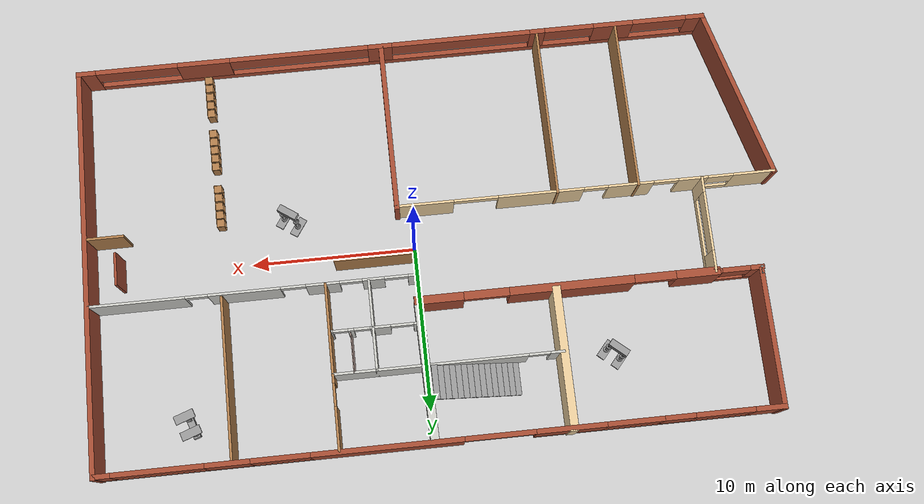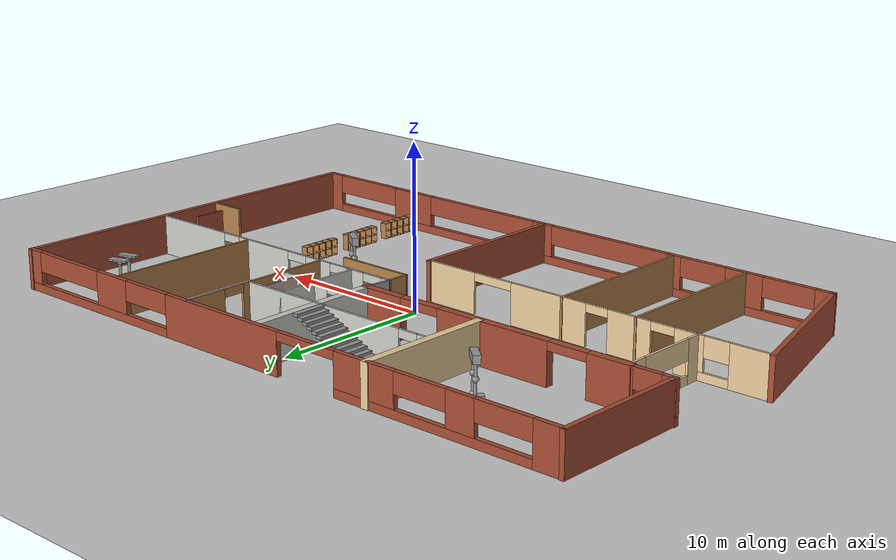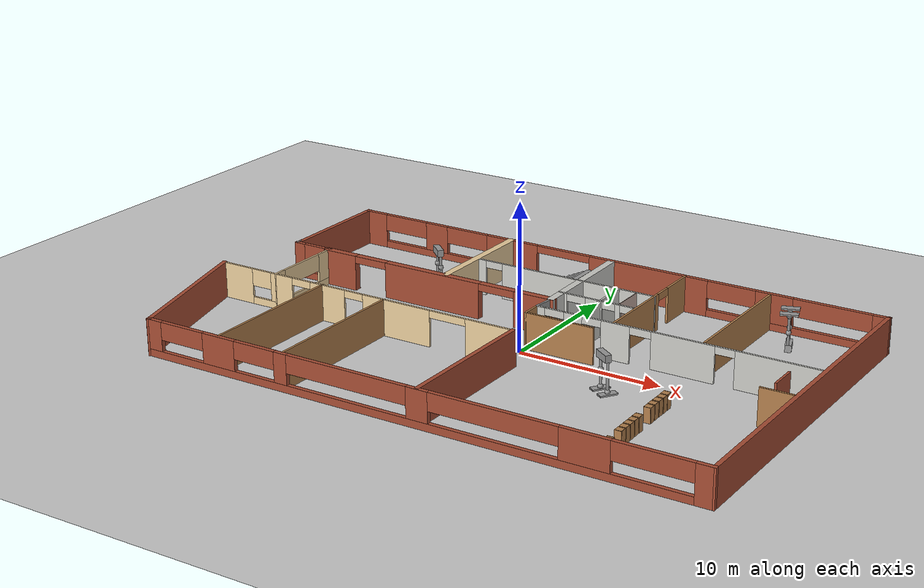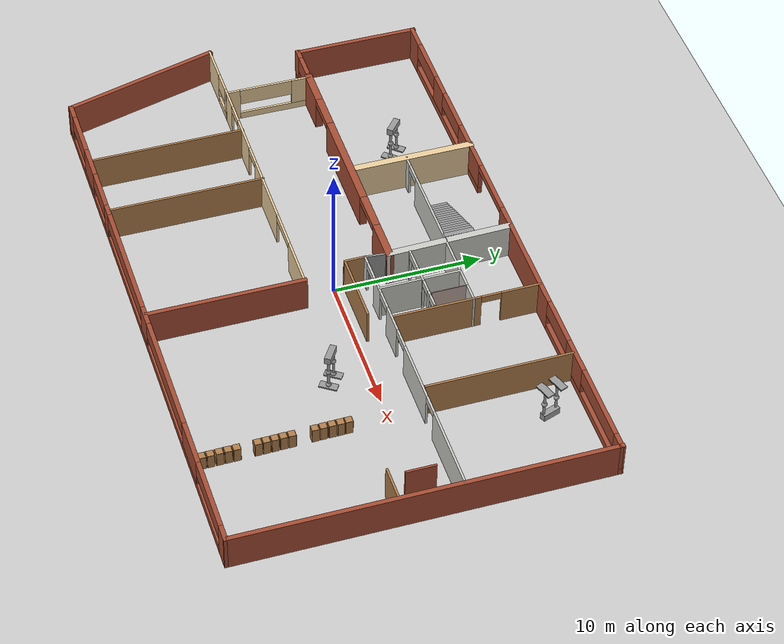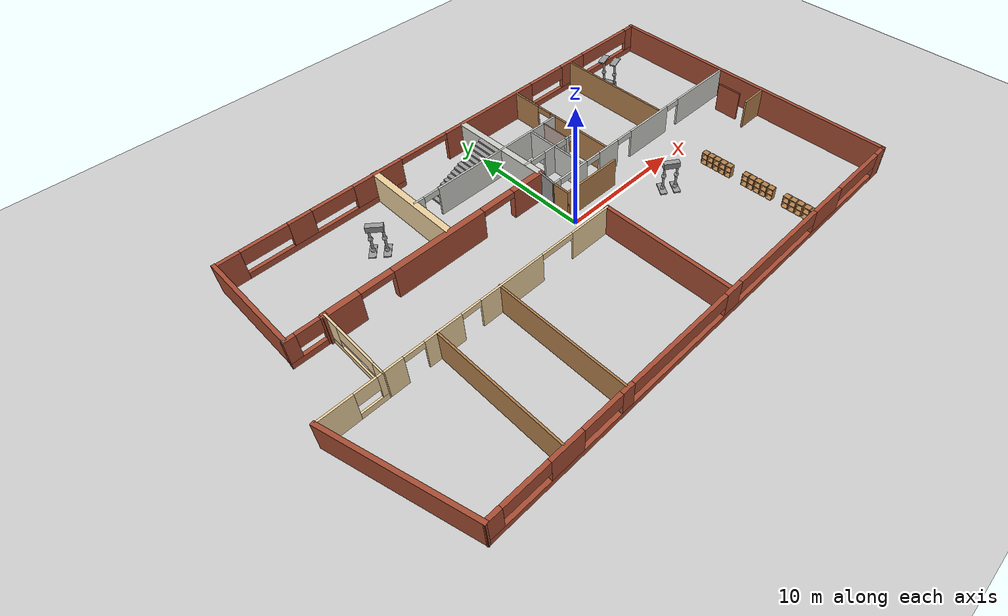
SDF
<sdf version="1.6">
 <world name="default">
  <plugin name="hello" filename="libhello.so"/>
  <light name="sun" type="directional">
   <pose>0 0 10 0 -0 0</pose>
   <diffuse>0.8 0.8 0.8 1</diffuse>
   <specular>0.2 0.2 0.2 1</specular>
   <attenuation>
    <range>1000</range>
    <constant>0.9</constant>
    <linear>0.01</linear>
    <quadratic>0.001</quadratic>
   </attenuation>
   <direction>-0.5 0.1 -0.9</direction>
  </light>
  <model name="ground_plane">
   <static>1</static>
   <link name="link">
    <collision name="collision">
     <geometry><plane><normal>0 0 1</normal><size>100 100</size></plane></geometry>
     <surface><friction><ode><mu>100</mu><mu2>50</mu2></ode></friction></surface>
    </collision>
    <visual name="visual">
     <cast_shadows>0</cast_shadows>
     <geometry><plane><normal>0 0 1</normal><size>100 100</size></plane></geometry>
     <material>
      <script><uri>file://media/materials/scripts/gazebo.material</uri><name>Gazebo/Grey</name></script>
     </material>
    </visual>
   </link>
  </model>
  <gravity>0 0 -9.8</gravity>
  <magnetic_field>6e-06 2.3e-05 -4.2e-05</magnetic_field>
  <atmosphere type="adiabatic"/>
  <physics name="default_physics" default="0" type="ode">
   <max_step_size>0.001</max_step_size>
   <real_time_factor>1</real_time_factor>
   <real_time_update_rate>1000</real_time_update_rate>
  </physics>
  <scene><ambient>0.4 0.4 0.4 1</ambient><background>0.7 0.7 0.7 1</background><shadows>1</shadows></scene>
  <spherical_coordinates>
   <surface_model>EARTH_WGS84</surface_model>
   <latitude_deg>0</latitude_deg>
   <longitude_deg>0</longitude_deg>
   <elevation>0</elevation>
   <heading_deg>0</heading_deg>
  </spherical_coordinates>
  <model name="Humanoid2">
   <link name="link_0">
    <pose>5.79772 -1.97955 0.05 0 -0 0</pose>
    <inertial>
     <mass>0.06046</mass>
     <inertia>
      <ixx>0.00720686</ixx>
      <ixy>0</ixy>
      <ixz>0</ixz>
      <iyy>0.00137814</iyy>
      <iyz>0</iyz>
      <izz>0.00848671</izz>
     </inertia>
    </inertial>
    <visual name="visual">
     <geometry><box><size>0.513593 1.19191 0.098763</size></box></geometry>
     <material>
      <lighting>1</lighting>
      <script><uri>file://media/materials/scripts/gazebo.material</uri><name>Gazebo/Grey</name></script>
      <shader type="pixel"><normal_map>__default__</normal_map></shader>
      <ambient>0.3 0.3 0.3 1</ambient>
      <diffuse>0.7 0.7 0.7 1</diffuse>
      <specular>0.01 0.01 0.01 1</specular>
      <emissive>0 0 0 1</emissive>
     </material>
    </visual>
    <collision name="collision">
     <geometry><box><size>0.513593 1.19191 0.098763</size></box></geometry>
     <surface>
      <friction>
       <ode><mu>1</mu><mu2>1</mu2><fdir1>0 0 0</fdir1><slip1>0</slip1><slip2>0</slip2></ode>
       <torsional>
        <coefficient>1</coefficient>
        <patch_radius>0</patch_radius>
        <surface_radius>0</surface_radius>
        <use_patch_radius>1</use_patch_radius>
        <ode><slip>0</slip></ode>
       </torsional>
      </friction>
      <bounce><restitution_coefficient>0</restitution_coefficient><threshold>1e+06</threshold></bounce>
      <contact>
       <collide_without_contact>0</collide_without_contact>
       <collide_without_contact_bitmask>1</collide_without_contact_bitmask>
       <collide_bitmask>1</collide_bitmask>
       <ode>
        <soft_cfm>0</soft_cfm>
        <soft_erp>0.2</soft_erp>
        <kp>1e+13</kp>
        <kd>1</kd>
        <max_vel>0.01</max_vel>
        <min_depth>0</min_depth>
       </ode>
       <bullet>
        <split_impulse>1</split_impulse>
        <split_impulse_penetration_threshold>-0.01</split_impulse_penetration_threshold>
        <soft_cfm>0</soft_cfm>
        <soft_erp>0.2</soft_erp>
        <kp>1e+13</kp>
        <kd>1</kd>
       </bullet>
      </contact>
     </surface>
    </collision>
   </link>
   <link name="link_0_clone">
    <pose>4.78369 -1.98069 0.05 0 -0 0</pose>
    <inertial>
     <mass>0.06046</mass>
     <inertia>
      <ixx>0.00720686</ixx>
      <ixy>0</ixy>
      <ixz>0</ixz>
      <iyy>0.00137814</iyy>
      <iyz>0</iyz>
      <izz>0.00848671</izz>
     </inertia>
    </inertial>
    <visual name="visual">
     <geometry><box><size>0.513593 1.19191 0.098763</size></box></geometry>
     <material>
      <lighting>1</lighting>
      <script><uri>file://media/materials/scripts/gazebo.material</uri><name>Gazebo/Grey</name></script>
      <shader type="pixel"><normal_map>__default__</normal_map></shader>
      <ambient>0.3 0.3 0.3 1</ambient>
      <diffuse>0.7 0.7 0.7 1</diffuse>
      <specular>0.01 0.01 0.01 1</specular>
      <emissive>0 0 0 1</emissive>
     </material>
    </visual>
    <collision name="collision">
     <geometry><box><size>0.513593 1.19191 0.098763</size></box></geometry>
     <surface>
      <friction>
       <ode><mu>1</mu><mu2>1</mu2><fdir1>0 0 0</fdir1><slip1>0</slip1><slip2>0</slip2></ode>
       <torsional>
        <coefficient>1</coefficient>
        <patch_radius>0</patch_radius>
        <surface_radius>0</surface_radius>
        <use_patch_radius>1</use_patch_radius>
        <ode><slip>0</slip></ode>
       </torsional>
      </friction>
      <bounce><restitution_coefficient>0</restitution_coefficient><threshold>1e+06</threshold></bounce>
      <contact>
       <collide_without_contact>0</collide_without_contact>
       <collide_without_contact_bitmask>1</collide_without_contact_bitmask>
       <collide_bitmask>1</collide_bitmask>
       <ode>
        <soft_cfm>0</soft_cfm>
        <soft_erp>0.2</soft_erp>
        <kp>1e+13</kp>
        <kd>1</kd>
        <max_vel>0.01</max_vel>
        <min_depth>0</min_depth>
       </ode>
       <bullet>
        <split_impulse>1</split_impulse>
        <split_impulse_penetration_threshold>-0.01</split_impulse_penetration_threshold>
        <soft_cfm>0</soft_cfm>
        <soft_erp>0.2</soft_erp>
        <kp>1e+13</kp>
        <kd>1</kd>
       </bullet>
      </contact>
     </surface>
    </collision>
   </link>
   <link name="link_1">
    <pose>5.78776 -1.98521 0.184527 0 -0 0</pose>
    <inertial>
     <mass>0.0436597</mass>
     <inertia>
      <ixx>0.000541334</ixx>
      <ixy>0</ixy>
      <ixz>0</ixz>
      <iyy>0.000541334</iyy>
      <iyz>0</iyz>
      <izz>0.000541334</izz>
     </inertia>
    </inertial>
    <visual name="visual">
     <geometry><sphere><radius>0.176061</radius></sphere></geometry>
     <material>
      <lighting>1</lighting>
      <script><uri>file://media/materials/scripts/gazebo.material</uri><name>Gazebo/Grey</name></script>
      <shader type="pixel"/>
      <ambient>0.3 0.3 0.3 1</ambient>
      <diffuse>0.7 0.7 0.7 1</diffuse>
      <specular>0.01 0.01 0.01 1</specular>
      <emissive>0 0 0 1</emissive>
     </material>
    </visual>
    <collision name="collision">
     <geometry><sphere><radius>0.176061</radius></sphere></geometry>
     <surface>
      <friction>
       <ode><mu>1</mu><mu2>1</mu2><fdir1>0 0 0</fdir1><slip1>0</slip1><slip2>0</slip2></ode>
       <torsional>
        <coefficient>1</coefficient>
        <patch_radius>0</patch_radius>
        <surface_radius>0</surface_radius>
        <use_patch_radius>1</use_patch_radius>
        <ode><slip>0</slip></ode>
       </torsional>
      </friction>
      <bounce><restitution_coefficient>0</restitution_coefficient><threshold>1e+06</threshold></bounce>
      <contact>
       <collide_without_contact>0</collide_without_contact>
       <collide_without_contact_bitmask>1</collide_without_contact_bitmask>
       <collide_bitmask>1</collide_bitmask>
       <ode>
        <soft_cfm>0</soft_cfm>
        <soft_erp>0.2</soft_erp>
        <kp>1e+13</kp>
        <kd>1</kd>
        <max_vel>0.01</max_vel>
        <min_depth>0</min_depth>
       </ode>
       <bullet>
        <split_impulse>1</split_impulse>
        <split_impulse_penetration_threshold>-0.01</split_impulse_penetration_threshold>
        <soft_cfm>0</soft_cfm>
        <soft_erp>0.2</soft_erp>
        <kp>1e+13</kp>
        <kd>1</kd>
       </bullet>
      </contact>
     </surface>
    </collision>
   </link>
   <link name="link_1_clone">
    <pose>5.78609 -1.99189 1.31349 0 -0 0</pose>
    <inertial>
     <mass>0.0436597</mass>
     <inertia>
      <ixx>0.000541334</ixx>
      <ixy>0</ixy>
      <ixz>0</ixz>
      <iyy>0.000541334</iyy>
      <iyz>0</iyz>
      <izz>0.000541334</izz>
     </inertia>
    </inertial>
    <visual name="visual">
     <geometry><sphere><radius>0.176061</radius></sphere></geometry>
     <material>
      <lighting>1</lighting>
      <script><uri>file://media/materials/scripts/gazebo.material</uri><name>Gazebo/Grey</name></script>
      <shader type="pixel"/>
      <ambient>0.3 0.3 0.3 1</ambient>
      <diffuse>0.7 0.7 0.7 1</diffuse>
      <specular>0.01 0.01 0.01 1</specular>
      <emissive>0 0 0 1</emissive>
     </material>
    </visual>
    <collision name="collision">
     <geometry><sphere><radius>0.176061</radius></sphere></geometry>
     <surface>
      <friction>
       <ode><mu>1</mu><mu2>1</mu2><fdir1>0 0 0</fdir1><slip1>0</slip1><slip2>0</slip2></ode>
       <torsional>
        <coefficient>1</coefficient>
        <patch_radius>0</patch_radius>
        <surface_radius>0</surface_radius>
        <use_patch_radius>1</use_patch_radius>
        <ode><slip>0</slip></ode>
       </torsional>
      </friction>
      <bounce><restitution_coefficient>0</restitution_coefficient><threshold>1e+06</threshold></bounce>
      <contact>
       <collide_without_contact>0</collide_without_contact>
       <collide_without_contact_bitmask>1</collide_without_contact_bitmask>
       <collide_bitmask>1</collide_bitmask>
       <ode>
        <soft_cfm>0</soft_cfm>
        <soft_erp>0.2</soft_erp>
        <kp>1e+13</kp>
        <kd>1</kd>
        <max_vel>0.01</max_vel>
        <min_depth>0</min_depth>
       </ode>
       <bullet>
        <split_impulse>1</split_impulse>
        <split_impulse_penetration_threshold>-0.01</split_impulse_penetration_threshold>
        <soft_cfm>0</soft_cfm>
        <soft_erp>0.2</soft_erp>
        <kp>1e+13</kp>
        <kd>1</kd>
       </bullet>
      </contact>
     </surface>
    </collision>
   </link>
   <link name="link_1_clone_0">
    <pose>4.81912 -1.97367 0.184527 0 -0 0</pose>
    <inertial>
     <mass>0.0436597</mass>
     <inertia>
      <ixx>0.000541334</ixx>
      <ixy>0</ixy>
      <ixz>0</ixz>
      <iyy>0.000541334</iyy>
      <iyz>0</iyz>
      <izz>0.000541334</izz>
     </inertia>
    </inertial>
    <visual name="visual">
     <geometry><sphere><radius>0.176061</radius></sphere></geometry>
     <material>
      <lighting>1</lighting>
      <script><uri>file://media/materials/scripts/gazebo.material</uri><name>Gazebo/Grey</name></script>
      <shader type="pixel"/>
      <ambient>0.3 0.3 0.3 1</ambient>
      <diffuse>0.7 0.7 0.7 1</diffuse>
      <specular>0.01 0.01 0.01 1</specular>
      <emissive>0 0 0 1</emissive>
     </material>
    </visual>
    <collision name="collision">
     <geometry><sphere><radius>0.176061</radius></sphere></geometry>
     <surface>
      <friction>
       <ode><mu>1</mu><mu2>1</mu2><fdir1>0 0 0</fdir1><slip1>0</slip1><slip2>0</slip2></ode>
       <torsional>
        <coefficient>1</coefficient>
        <patch_radius>0</patch_radius>
        <surface_radius>0</surface_radius>
        <use_patch_radius>1</use_patch_radius>
        <ode><slip>0</slip></ode>
       </torsional>
      </friction>
      <bounce><restitution_coefficient>0</restitution_coefficient><threshold>1e+06</threshold></bounce>
      <contact>
       <collide_without_contact>0</collide_without_contact>
       <collide_without_contact_bitmask>1</collide_without_contact_bitmask>
       <collide_bitmask>1</collide_bitmask>
       <ode>
        <soft_cfm>0</soft_cfm>
        <soft_erp>0.2</soft_erp>
        <kp>1e+13</kp>
        <kd>1</kd>
        <max_vel>0.01</max_vel>
        <min_depth>0</min_depth>
       </ode>
       <bullet>
        <split_impulse>1</split_impulse>
        <split_impulse_penetration_threshold>-0.01</split_impulse_penetration_threshold>
        <soft_cfm>0</soft_cfm>
        <soft_erp>0.2</soft_erp>
        <kp>1e+13</kp>
        <kd>1</kd>
       </bullet>
      </contact>
     </surface>
    </collision>
   </link>
   <link name="link_1_clone_clone_0">
    <pose>4.82981 -1.98574 1.31349 0 -0 0</pose>
    <inertial>
     <mass>0.0436597</mass>
     <inertia>
      <ixx>0.000541334</ixx>
      <ixy>0</ixy>
      <ixz>0</ixz>
      <iyy>0.000541334</iyy>
      <iyz>0</iyz>
      <izz>0.000541334</izz>
     </inertia>
    </inertial>
    <visual name="visual">
     <geometry><sphere><radius>0.176061</radius></sphere></geometry>
     <material>
      <lighting>1</lighting>
      <script><uri>file://media/materials/scripts/gazebo.material</uri><name>Gazebo/Grey</name></script>
      <shader type="pixel"/>
      <ambient>0.3 0.3 0.3 1</ambient>
      <diffuse>0.7 0.7 0.7 1</diffuse>
      <specular>0.01 0.01 0.01 1</specular>
      <emissive>0 0 0 1</emissive>
     </material>
    </visual>
    <collision name="collision">
     <geometry><sphere><radius>0.176061</radius></sphere></geometry>
     <surface>
      <friction>
       <ode><mu>1</mu><mu2>1</mu2><fdir1>0 0 0</fdir1><slip1>0</slip1><slip2>0</slip2></ode>
       <torsional>
        <coefficient>1</coefficient>
        <patch_radius>0</patch_radius>
        <surface_radius>0</surface_radius>
        <use_patch_radius>1</use_patch_radius>
        <ode><slip>0</slip></ode>
       </torsional>
      </friction>
      <bounce><restitution_coefficient>0</restitution_coefficient><threshold>1e+06</threshold></bounce>
      <contact>
       <collide_without_contact>0</collide_without_contact>
       <collide_without_contact_bitmask>1</collide_without_contact_bitmask>
       <collide_bitmask>1</collide_bitmask>
       <ode>
        <soft_cfm>0</soft_cfm>
        <soft_erp>0.2</soft_erp>
        <kp>1e+13</kp>
        <kd>1</kd>
        <max_vel>0.01</max_vel>
        <min_depth>0</min_depth>
       </ode>
       <bullet>
        <split_impulse>1</split_impulse>
        <split_impulse_penetration_threshold>-0.01</split_impulse_penetration_threshold>
        <soft_cfm>0</soft_cfm>
        <soft_erp>0.2</soft_erp>
        <kp>1e+13</kp>
        <kd>1</kd>
       </bullet>
      </contact>
     </surface>
    </collision>
   </link>
   <link name="link_2">
    <pose>5.78656 -1.98911 0.758077 0 -0 0</pose>
    <inertial>
     <mass>0.0281952</mass>
     <inertia>
      <ixx>0.00239929</ixx>
      <ixy>0</ixy>
      <ixz>0</ixz>
      <iyy>0.00239929</iyy>
      <iyz>0</iyz>
      <izz>9.93738e-05</izz>
     </inertia>
    </inertial>
    <visual name="visual">
     <geometry><cylinder><radius>0.0839582</radius><length>1</length></cylinder></geometry>
     <material>
      <lighting>1</lighting>
      <script><uri>file://media/materials/scripts/gazebo.material</uri><name>Gazebo/Grey</name></script>
      <shader type="pixel"/>
      <ambient>0.3 0.3 0.3 1</ambient>
      <diffuse>0.7 0.7 0.7 1</diffuse>
      <specular>0.01 0.01 0.01 1</specular>
      <emissive>0 0 0 1</emissive>
     </material>
    </visual>
    <collision name="collision">
     <geometry><cylinder><radius>0.083958</radius><length>1</length></cylinder></geometry>
     <surface>
      <friction>
       <ode><mu>1</mu><mu2>1</mu2><fdir1>0 0 0</fdir1><slip1>0</slip1><slip2>0</slip2></ode>
       <torsional>
        <coefficient>1</coefficient>
        <patch_radius>0</patch_radius>
        <surface_radius>0</surface_radius>
        <use_patch_radius>1</use_patch_radius>
        <ode><slip>0</slip></ode>
       </torsional>
      </friction>
      <bounce><restitution_coefficient>0</restitution_coefficient><threshold>1e+06</threshold></bounce>
      <contact>
       <collide_without_contact>0</collide_without_contact>
       <collide_without_contact_bitmask>1</collide_without_contact_bitmask>
       <collide_bitmask>1</collide_bitmask>
       <ode>
        <soft_cfm>0</soft_cfm>
        <soft_erp>0.2</soft_erp>
        <kp>1e+13</kp>
        <kd>1</kd>
        <max_vel>0.01</max_vel>
        <min_depth>0</min_depth>
       </ode>
       <bullet>
        <split_impulse>1</split_impulse>
        <split_impulse_penetration_threshold>-0.01</split_impulse_penetration_threshold>
        <soft_cfm>0</soft_cfm>
        <soft_erp>0.2</soft_erp>
        <kp>1e+13</kp>
        <kd>1</kd>
       </bullet>
      </contact>
     </surface>
    </collision>
   </link>
   <link name="link_2_clone">
    <pose>5.79309 -1.99682 1.88288 0 -0 0</pose>
    <inertial>
     <mass>0.0281952</mass>
     <inertia>
      <ixx>0.00239929</ixx>
      <ixy>0</ixy>
      <ixz>0</ixz>
      <iyy>0.00239929</iyy>
      <iyz>0</iyz>
      <izz>9.93738e-05</izz>
     </inertia>
    </inertial>
    <visual name="visual">
     <geometry><cylinder><radius>0.0839582</radius><length>1</length></cylinder></geometry>
     <material>
      <lighting>1</lighting>
      <script><uri>file://media/materials/scripts/gazebo.material</uri><name>Gazebo/Grey</name></script>
      <shader type="pixel"/>
      <ambient>0.3 0.3 0.3 1</ambient>
      <diffuse>0.7 0.7 0.7 1</diffuse>
      <specular>0.01 0.01 0.01 1</specular>
      <emissive>0 0 0 1</emissive>
     </material>
    </visual>
    <collision name="collision">
     <geometry><cylinder><radius>0.083958</radius><length>1</length></cylinder></geometry>
     <surface>
      <friction>
       <ode><mu>1</mu><mu2>1</mu2><fdir1>0 0 0</fdir1><slip1>0</slip1><slip2>0</slip2></ode>
       <torsional>
        <coefficient>1</coefficient>
        <patch_radius>0</patch_radius>
        <surface_radius>0</surface_radius>
        <use_patch_radius>1</use_patch_radius>
        <ode><slip>0</slip></ode>
       </torsional>
      </friction>
      <bounce><restitution_coefficient>0</restitution_coefficient><threshold>1e+06</threshold></bounce>
      <contact>
       <collide_without_contact>0</collide_without_contact>
       <collide_without_contact_bitmask>1</collide_without_contact_bitmask>
       <collide_bitmask>1</collide_bitmask>
       <ode>
        <soft_cfm>0</soft_cfm>
        <soft_erp>0.2</soft_erp>
        <kp>1e+13</kp>
        <kd>1</kd>
        <max_vel>0.01</max_vel>
        <min_depth>0</min_depth>
       </ode>
       <bullet>
        <split_impulse>1</split_impulse>
        <split_impulse_penetration_threshold>-0.01</split_impulse_penetration_threshold>
        <soft_cfm>0</soft_cfm>
        <soft_erp>0.2</soft_erp>
        <kp>1e+13</kp>
        <kd>1</kd>
       </bullet>
      </contact>
     </surface>
    </collision>
   </link>
   <link name="link_2_clone_0">
    <pose>4.82328 -1.96972 0.758077 0 -0 0</pose>
    <inertial>
     <mass>0.0281952</mass>
     <inertia>
      <ixx>0.00239929</ixx>
      <ixy>0</ixy>
      <ixz>0</ixz>
      <iyy>0.00239929</iyy>
      <iyz>0</iyz>
      <izz>9.93738e-05</izz>
     </inertia>
    </inertial>
    <visual name="visual">
     <geometry><cylinder><radius>0.0839582</radius><length>1</length></cylinder></geometry>
     <material>
      <lighting>1</lighting>
      <script><uri>file://media/materials/scripts/gazebo.material</uri><name>Gazebo/Grey</name></script>
      <shader type="pixel"/>
      <ambient>0.3 0.3 0.3 1</ambient>
      <diffuse>0.7 0.7 0.7 1</diffuse>
      <specular>0.01 0.01 0.01 1</specular>
      <emissive>0 0 0 1</emissive>
     </material>
    </visual>
    <collision name="collision">
     <geometry><cylinder><radius>0.083958</radius><length>1</length></cylinder></geometry>
     <surface>
      <friction>
       <ode><mu>1</mu><mu2>1</mu2><fdir1>0 0 0</fdir1><slip1>0</slip1><slip2>0</slip2></ode>
       <torsional>
        <coefficient>1</coefficient>
        <patch_radius>0</patch_radius>
        <surface_radius>0</surface_radius>
        <use_patch_radius>1</use_patch_radius>
        <ode><slip>0</slip></ode>
       </torsional>
      </friction>
      <bounce><restitution_coefficient>0</restitution_coefficient><threshold>1e+06</threshold></bounce>
      <contact>
       <collide_without_contact>0</collide_without_contact>
       <collide_without_contact_bitmask>1</collide_without_contact_bitmask>
       <collide_bitmask>1</collide_bitmask>
       <ode>
        <soft_cfm>0</soft_cfm>
        <soft_erp>0.2</soft_erp>
        <kp>1e+13</kp>
        <kd>1</kd>
        <max_vel>0.01</max_vel>
        <min_depth>0</min_depth>
       </ode>
       <bullet>
        <split_impulse>1</split_impulse>
        <split_impulse_penetration_threshold>-0.01</split_impulse_penetration_threshold>
        <soft_cfm>0</soft_cfm>
        <soft_erp>0.2</soft_erp>
        <kp>1e+13</kp>
        <kd>1</kd>
       </bullet>
      </contact>
     </surface>
    </collision>
   </link>
   <link name="link_2_clone_clone">
    <pose>4.82782 -1.98664 1.88288 0 -0 0</pose>
    <inertial>
     <mass>0.0281952</mass>
     <inertia>
      <ixx>0.00239929</ixx>
      <ixy>0</ixy>
      <ixz>0</ixz>
      <iyy>0.00239929</iyy>
      <iyz>0</iyz>
      <izz>9.93738e-05</izz>
     </inertia>
    </inertial>
    <visual name="visual">
     <geometry><cylinder><radius>0.0839582</radius><length>1</length></cylinder></geometry>
     <material>
      <lighting>1</lighting>
      <script><uri>file://media/materials/scripts/gazebo.material</uri><name>Gazebo/Grey</name></script>
      <shader type="pixel"/>
      <ambient>0.3 0.3 0.3 1</ambient>
      <diffuse>0.7 0.7 0.7 1</diffuse>
      <specular>0.01 0.01 0.01 1</specular>
      <emissive>0 0 0 1</emissive>
     </material>
    </visual>
    <collision name="collision">
     <geometry><cylinder><radius>0.083958</radius><length>1</length></cylinder></geometry>
     <surface>
      <friction>
       <ode><mu>1</mu><mu2>1</mu2><fdir1>0 0 0</fdir1><slip1>0</slip1><slip2>0</slip2></ode>
       <torsional>
        <coefficient>1</coefficient>
        <patch_radius>0</patch_radius>
        <surface_radius>0</surface_radius>
        <use_patch_radius>1</use_patch_radius>
        <ode><slip>0</slip></ode>
       </torsional>
      </friction>
      <bounce><restitution_coefficient>0</restitution_coefficient><threshold>1e+06</threshold></bounce>
      <contact>
       <collide_without_contact>0</collide_without_contact>
       <collide_without_contact_bitmask>1</collide_without_contact_bitmask>
       <collide_bitmask>1</collide_bitmask>
       <ode>
        <soft_cfm>0</soft_cfm>
        <soft_erp>0.2</soft_erp>
        <kp>1e+13</kp>
        <kd>1</kd>
        <max_vel>0.01</max_vel>
        <min_depth>0</min_depth>
       </ode>
       <bullet>
        <split_impulse>1</split_impulse>
        <split_impulse_penetration_threshold>-0.01</split_impulse_penetration_threshold>
        <soft_cfm>0</soft_cfm>
        <soft_erp>0.2</soft_erp>
        <kp>1e+13</kp>
        <kd>1</kd>
       </bullet>
      </contact>
     </surface>
    </collision>
   </link>
   <link name="link_3">
    <pose>5.29594 -2.02732 2.37324 0 -0 0</pose>
    <inertial>
     <mass>0.249231</mass>
     <inertia>
      <ixx>0.00849422</ixx>
      <ixy>0</ixy>
      <ixz>0</ixz>
      <iyy>0.0360264</iyy>
      <iyz>0</iyz>
      <izz>0.0350307</izz>
     </inertia>
    </inertial>
    <visual name="visual">
     <geometry><box><size>1.22725 0.424878 0.477974</size></box></geometry>
     <material>
      <lighting>1</lighting>
      <script><uri>file://media/materials/scripts/gazebo.material</uri><name>Gazebo/Grey</name></script>
      <shader type="pixel"><normal_map>__default__</normal_map></shader>
      <ambient>0.3 0.3 0.3 1</ambient>
      <diffuse>0.7 0.7 0.7 1</diffuse>
      <specular>0.01 0.01 0.01 1</specular>
      <emissive>0 0 0 1</emissive>
     </material>
    </visual>
    <collision name="collision">
     <geometry><box><size>1.22725 0.424878 0.477974</size></box></geometry>
     <surface>
      <friction>
       <ode><mu>1</mu><mu2>1</mu2><fdir1>0 0 0</fdir1><slip1>0</slip1><slip2>0</slip2></ode>
       <torsional>
        <coefficient>1</coefficient>
        <patch_radius>0</patch_radius>
        <surface_radius>0</surface_radius>
        <use_patch_radius>1</use_patch_radius>
        <ode><slip>0</slip></ode>
       </torsional>
      </friction>
      <bounce><restitution_coefficient>0</restitution_coefficient><threshold>1e+06</threshold></bounce>
      <contact>
       <collide_without_contact>0</collide_without_contact>
       <collide_without_contact_bitmask>1</collide_without_contact_bitmask>
       <collide_bitmask>1</collide_bitmask>
       <ode>
        <soft_cfm>0</soft_cfm>
        <soft_erp>0.2</soft_erp>
        <kp>1e+13</kp>
        <kd>1</kd>
        <max_vel>0.01</max_vel>
        <min_depth>0</min_depth>
       </ode>
       <bullet>
        <split_impulse>1</split_impulse>
        <split_impulse_penetration_threshold>-0.01</split_impulse_penetration_threshold>
        <soft_cfm>0</soft_cfm>
        <soft_erp>0.2</soft_erp>
        <kp>1e+13</kp>
        <kd>1</kd>
       </bullet>
      </contact>
     </surface>
    </collision>
   </link>
   <joint name="link_1_JOINT_9" type="fixed">
    <parent>link_1</parent>
    <child>link_0</child>
    <physics>
     <ode><limit><cfm>0</cfm><erp>0.2</erp></limit><suspension><cfm>0</cfm><erp>0.2</erp></suspension></ode>
    </physics>
   </joint>
   <joint name="link_1_clone_0_JOINT_8" type="fixed">
    <parent>link_1_clone_0</parent>
    <child>link_0_clone</child>
    <physics>
     <ode><limit><cfm>0</cfm><erp>0.2</erp></limit><suspension><cfm>0</cfm><erp>0.2</erp></suspension></ode>
    </physics>
   </joint>
   <joint name="link_1_clone_JOINT_5" type="fixed">
    <parent>link_1_clone</parent>
    <child>link_2</child>
    <physics>
     <ode><limit><cfm>0</cfm><erp>0.2</erp></limit><suspension><cfm>0</cfm><erp>0.2</erp></suspension></ode>
    </physics>
   </joint>
   <joint name="link_1_clone_clone_0_JOINT_4" type="fixed">
    <parent>link_1_clone_clone_0</parent>
    <child>link_2_clone_0</child>
    <physics>
     <ode><limit><cfm>0</cfm><erp>0.2</erp></limit><suspension><cfm>0</cfm><erp>0.2</erp></suspension></ode>
    </physics>
   </joint>
   <joint name="link_2_JOINT_7" type="fixed">
    <parent>link_2</parent>
    <child>link_1</child>
    <physics>
     <ode><limit><cfm>0</cfm><erp>0.2</erp></limit><suspension><cfm>0</cfm><erp>0.2</erp></suspension></ode>
    </physics>
   </joint>
   <joint name="link_2_clone_0_JOINT_6" type="fixed">
    <parent>link_2_clone_0</parent>
    <child>link_1_clone_0</child>
    <physics>
     <ode><limit><cfm>0</cfm><erp>0.2</erp></limit><suspension><cfm>0</cfm><erp>0.2</erp></suspension></ode>
    </physics>
   </joint>
   <joint name="link_2_clone_JOINT_3" type="fixed">
    <parent>link_2_clone</parent>
    <child>link_1_clone</child>
    <physics>
     <ode><limit><cfm>0</cfm><erp>0.2</erp></limit><suspension><cfm>0</cfm><erp>0.2</erp></suspension></ode>
    </physics>
   </joint>
   <joint name="link_2_clone_clone_JOINT_2" type="fixed">
    <parent>link_2_clone_clone</parent>
    <child>link_1_clone_clone_0</child>
    <physics>
     <ode><limit><cfm>0</cfm><erp>0.2</erp></limit><suspension><cfm>0</cfm><erp>0.2</erp></suspension></ode>
    </physics>
   </joint>
   <joint name="link_3_JOINT_0" type="fixed">
    <parent>link_3</parent>
    <child>link_2_clone_clone</child>
    <physics>
     <ode><limit><cfm>0</cfm><erp>0.2</erp></limit><suspension><cfm>0</cfm><erp>0.2</erp></suspension></ode>
    </physics>
   </joint>
   <joint name="link_3_JOINT_1" type="fixed">
    <parent>link_3</parent>
    <child>link_2_clone</child>
    <physics>
     <ode><limit><cfm>0</cfm><erp>0.2</erp></limit><suspension><cfm>0</cfm><erp>0.2</erp></suspension></ode>
    </physics>
   </joint>
   <static>0</static>
   <pose>4.18648 2.16939 -0.000728 -3.9e-05 -2e-06 -0.599882</pose>
  </model>
  <model name="Building">
   <pose>-1.26631 -0.299272 0 0 -0 0</pose>
   <link name="Stairs_0">
    <visual name="Stairs_0_Visual_0">
     <pose>-4.08117 8.87242 0.083333 0 -0 1.5708</pose>
     <geometry><box><size>2.02255 0.353633 0.166667</size></box></geometry>
     <material>
      <script><uri>file://media/materials/scripts/gazebo.material</uri><name>Gazebo/Grey</name></script>
      <ambient>1 1 1 1</ambient>
     </material>
     <meta><layer>0</layer></meta>
    </visual>
    <collision name="Stairs_0_Collision_0">
     <geometry><box><size>2.02255 0.353633 0.166667</size></box></geometry>
     <pose>-4.08117 8.87242 0.083333 0 -0 1.5708</pose>
    </collision>
    <visual name="Stairs_0_Visual_1">
     <pose>-3.72754 8.87242 0.25 0 -0 1.5708</pose>
     <geometry><box><size>2.02255 0.353633 0.166667</size></box></geometry>
     <material>
      <script><uri>file://media/materials/scripts/gazebo.material</uri><name>Gazebo/Grey</name></script>
      <ambient>1 1 1 1</ambient>
     </material>
     <meta><layer>0</layer></meta>
    </visual>
    <collision name="Stairs_0_Collision_1">
     <geometry><box><size>2.02255 0.353633 0.166667</size></box></geometry>
     <pose>-3.72754 8.87242 0.25 0 -0 1.5708</pose>
    </collision>
    <visual name="Stairs_0_Visual_2">
     <pose>-3.3739 8.87242 0.416667 0 -0 1.5708</pose>
     <geometry><box><size>2.02255 0.353633 0.166667</size></box></geometry>
     <material>
      <script><uri>file://media/materials/scripts/gazebo.material</uri><name>Gazebo/Grey</name></script>
      <ambient>1 1 1 1</ambient>
     </material>
     <meta><layer>0</layer></meta>
    </visual>
    <collision name="Stairs_0_Collision_2">
     <geometry><box><size>2.02255 0.353633 0.166667</size></box></geometry>
     <pose>-3.3739 8.87242 0.416667 0 -0 1.5708</pose>
    </collision>
    <visual name="Stairs_0_Visual_3">
     <pose>-3.02027 8.87242 0.583333 0 -0 1.5708</pose>
     <geometry><box><size>2.02255 0.353633 0.166667</size></box></geometry>
     <material>
      <script><uri>file://media/materials/scripts/gazebo.material</uri><name>Gazebo/Grey</name></script>
      <ambient>1 1 1 1</ambient>
     </material>
     <meta><layer>0</layer></meta>
    </visual>
    <collision name="Stairs_0_Collision_3">
     <geometry><box><size>2.02255 0.353633 0.166667</size></box></geometry>
     <pose>-3.02027 8.87242 0.583333 0 -0 1.5708</pose>
    </collision>
    <visual name="Stairs_0_Visual_4">
     <pose>-2.66664 8.87242 0.75 0 -0 1.5708</pose>
     <geometry><box><size>2.02255 0.353633 0.166667</size></box></geometry>
     <material>
      <script><uri>file://media/materials/scripts/gazebo.material</uri><name>Gazebo/Grey</name></script>
      <ambient>1 1 1 1</ambient>
     </material>
     <meta><layer>0</layer></meta>
    </visual>
    <collision name="Stairs_0_Collision_4">
     <geometry><box><size>2.02255 0.353633 0.166667</size></box></geometry>
     <pose>-2.66664 8.87242 0.75 0 -0 1.5708</pose>
    </collision>
    <visual name="Stairs_0_Visual_5">
     <pose>-2.313 8.87242 0.916667 0 -0 1.5708</pose>
     <geometry><box><size>2.02255 0.353633 0.166667</size></box></geometry>
     <material>
      <script><uri>file://media/materials/scripts/gazebo.material</uri><name>Gazebo/Grey</name></script>
      <ambient>1 1 1 1</ambient>
     </material>
     <meta><layer>0</layer></meta>
    </visual>
    <collision name="Stairs_0_Collision_5">
     <geometry><box><size>2.02255 0.353633 0.166667</size></box></geometry>
     <pose>-2.313 8.87242 0.916667 0 -0 1.5708</pose>
    </collision>
    <visual name="Stairs_0_Visual_6">
     <pose>-1.95937 8.87242 1.08333 0 -0 1.5708</pose>
     <geometry><box><size>2.02255 0.353633 0.166667</size></box></geometry>
     <material>
      <script><uri>file://media/materials/scripts/gazebo.material</uri><name>Gazebo/Grey</name></script>
      <ambient>1 1 1 1</ambient>
     </material>
     <meta><layer>0</layer></meta>
    </visual>
    <collision name="Stairs_0_Collision_6">
     <geometry><box><size>2.02255 0.353633 0.166667</size></box></geometry>
     <pose>-1.95937 8.87242 1.08333 0 -0 1.5708</pose>
    </collision>
    <visual name="Stairs_0_Visual_7">
     <pose>-1.60574 8.87242 1.25 0 -0 1.5708</pose>
     <geometry><box><size>2.02255 0.353633 0.166667</size></box></geometry>
     <material>
      <script><uri>file://media/materials/scripts/gazebo.material</uri><name>Gazebo/Grey</name></script>
      <ambient>1 1 1 1</ambient>
     </material>
     <meta><layer>0</layer></meta>
    </visual>
    <collision name="Stairs_0_Collision_7">
     <geometry><box><size>2.02255 0.353633 0.166667</size></box></geometry>
     <pose>-1.60574 8.87242 1.25 0 -0 1.5708</pose>
    </collision>
    <visual name="Stairs_0_Visual_8">
     <pose>-1.2521 8.87242 1.41667 0 -0 1.5708</pose>
     <geometry><box><size>2.02255 0.353633 0.166667</size></box></geometry>
     <material>
      <script><uri>file://media/materials/scripts/gazebo.material</uri><name>Gazebo/Grey</name></script>
      <ambient>1 1 1 1</ambient>
     </material>
     <meta><layer>0</layer></meta>
    </visual>
    <collision name="Stairs_0_Collision_8">
     <geometry><box><size>2.02255 0.353633 0.166667</size></box></geometry>
     <pose>-1.2521 8.87242 1.41667 0 -0 1.5708</pose>
    </collision>
    <visual name="Stairs_0_Visual_9">
     <pose>-0.898471 8.87242 1.58333 0 -0 1.5708</pose>
     <geometry><box><size>2.02255 0.353633 0.166667</size></box></geometry>
     <material>
      <script><uri>file://media/materials/scripts/gazebo.material</uri><name>Gazebo/Grey</name></script>
      <ambient>1 1 1 1</ambient>
     </material>
     <meta><layer>0</layer></meta>
    </visual>
    <collision name="Stairs_0_Collision_9">
     <geometry><box><size>2.02255 0.353633 0.166667</size></box></geometry>
     <pose>-0.898471 8.87242 1.58333 0 -0 1.5708</pose>
    </collision>
    <visual name="Stairs_0_Visual_10">
     <pose>-0.544838 8.87242 1.75 0 -0 1.5708</pose>
     <geometry><box><size>2.02255 0.353633 0.166667</size></box></geometry>
     <material>
      <script><uri>file://media/materials/scripts/gazebo.material</uri><name>Gazebo/Grey</name></script>
      <ambient>1 1 1 1</ambient>
     </material>
     <meta><layer>0</layer></meta>
    </visual>
    <collision name="Stairs_0_Collision_10">
     <geometry><box><size>2.02255 0.353633 0.166667</size></box></geometry>
     <pose>-0.544838 8.87242 1.75 0 -0 1.5708</pose>
    </collision>
    <visual name="Stairs_0_Visual_11">
     <pose>-0.191204 8.87242 1.91667 0 -0 1.5708</pose>
     <geometry><box><size>2.02255 0.353633 0.166667</size></box></geometry>
     <material>
      <script><uri>file://media/materials/scripts/gazebo.material</uri><name>Gazebo/Grey</name></script>
      <ambient>1 1 1 1</ambient>
     </material>
     <meta><layer>0</layer></meta>
    </visual>
    <collision name="Stairs_0_Collision_11">
     <geometry><box><size>2.02255 0.353633 0.166667</size></box></geometry>
     <pose>-0.191204 8.87242 1.91667 0 -0 1.5708</pose>
    </collision>
    <visual name="Stairs_0_Visual_12">
     <pose>0.162429 8.87242 2.08333 0 -0 1.5708</pose>
     <geometry><box><size>2.02255 0.353633 0.166667</size></box></geometry>
     <material>
      <script><uri>file://media/materials/scripts/gazebo.material</uri><name>Gazebo/Grey</name></script>
      <ambient>1 1 1 1</ambient>
     </material>
     <meta><layer>0</layer></meta>
    </visual>
    <collision name="Stairs_0_Collision_12">
     <geometry><box><size>2.02255 0.353633 0.166667</size></box></geometry>
     <pose>0.162429 8.87242 2.08333 0 -0 1.5708</pose>
    </collision>
    <visual name="Stairs_0_Visual_13">
     <pose>0.516062 8.87242 2.25 0 -0 1.5708</pose>
     <geometry><box><size>2.02255 0.353633 0.166667</size></box></geometry>
     <material>
      <script><uri>file://media/materials/scripts/gazebo.material</uri><name>Gazebo/Grey</name></script>
      <ambient>1 1 1 1</ambient>
     </material>
     <meta><layer>0</layer></meta>
    </visual>
    <collision name="Stairs_0_Collision_13">
     <geometry><box><size>2.02255 0.353633 0.166667</size></box></geometry>
     <pose>0.516062 8.87242 2.25 0 -0 1.5708</pose>
    </collision>
    <visual name="Stairs_0_Visual_14">
     <pose>0.869695 8.87242 2.41667 0 -0 1.5708</pose>
     <geometry><box><size>2.02255 0.353633 0.166667</size></box></geometry>
     <material>
      <script><uri>file://media/materials/scripts/gazebo.material</uri><name>Gazebo/Grey</name></script>
      <ambient>1 1 1 1</ambient>
     </material>
     <meta><layer>0</layer></meta>
    </visual>
    <collision name="Stairs_0_Collision_14">
     <geometry><box><size>2.02255 0.353633 0.166667</size></box></geometry>
     <pose>0.869695 8.87242 2.41667 0 -0 1.5708</pose>
    </collision>
   </link>
   <link name="Wall_17">
    <collision name="Wall_17_Collision">
     <geometry><box><size>8.49148 0.3 2.5</size></box></geometry>
     <pose>0 0 1.25 0 -0 0</pose>
    </collision>
    <visual name="Wall_17_Visual">
     <pose>0 0 1.25 0 -0 0</pose>
     <geometry><box><size>8.49148 0.3 2.5</size></box></geometry>
     <material>
      <script><uri>file://media/materials/scripts/gazebo.material</uri><name>Gazebo/Bricks</name></script>
      <ambient>1 1 1 1</ambient>
     </material>
     <meta><layer>0</layer></meta>
    </visual>
    <pose>-19.1444 8.2625 0 0 -0 1.5708</pose>
   </link>
   <link name="Wall_18">
    <pose>0.905623 12.3125 0 0 -0 0</pose>
    <visual name="Wall_18_Visual_0">
     <pose>-19.2672 0 1.25 0 -0 0</pose>
     <geometry><box><size>1.86558 0.3 2.5</size></box></geometry>
     <material>
      <script><uri>file://media/materials/scripts/gazebo.material</uri><name>Gazebo/Bricks</name></script>
      <ambient>1 1 1 1</ambient>
     </material>
     <meta><layer>0</layer></meta>
    </visual>
    <collision name="Wall_18_Collision_0">
     <geometry><box><size>1.86558 0.3 2.5</size></box></geometry>
     <pose>-19.2672 0 1.25 0 -0 0</pose>
    </collision>
    <visual name="Wall_18_Visual_1">
     <pose>3.08951 0 1.25 0 -0 0</pose>
     <geometry><box><size>8.93043 0.3 2.5</size></box></geometry>
     <material>
      <script><uri>file://media/materials/scripts/gazebo.material</uri><name>Gazebo/Bricks</name></script>
      <ambient>1 1 1 1</ambient>
     </material>
     <meta><layer>0</layer></meta>
    </visual>
    <collision name="Wall_18_Collision_1">
     <geometry><box><size>8.93043 0.3 2.5</size></box></geometry>
     <pose>3.08951 0 1.25 0 -0 0</pose>
    </collision>
    <visual name="Wall_18_Visual_2">
     <pose>-11.9358 0 0.25 0 -0 0</pose>
     <geometry><box><size>12.7972 0.3 0.5</size></box></geometry>
     <material>
      <script><uri>file://media/materials/scripts/gazebo.material</uri><name>Gazebo/Bricks</name></script>
      <ambient>1 1 1 1</ambient>
     </material>
     <meta><layer>0</layer></meta>
    </visual>
    <collision name="Wall_18_Collision_2">
     <geometry><box><size>12.7972 0.3 0.5</size></box></geometry>
     <pose>-11.9358 0 0.25 0 -0 0</pose>
    </collision>
    <visual name="Wall_18_Visual_3">
     <pose>13.8774 0 0.25 0 -0 0</pose>
     <geometry><box><size>12.6453 0.3 0.5</size></box></geometry>
     <material>
      <script><uri>file://media/materials/scripts/gazebo.material</uri><name>Gazebo/Bricks</name></script>
      <ambient>1 1 1 1</ambient>
     </material>
     <meta><layer>0</layer></meta>
    </visual>
    <collision name="Wall_18_Collision_3">
     <geometry><box><size>12.6453 0.3 0.5</size></box></geometry>
     <pose>13.8774 0 0.25 0 -0 0</pose>
    </collision>
    <visual name="Wall_18_Visual_4">
     <pose>-13.9321 0 1.5 0 -0 0</pose>
     <geometry><box><size>1.8072 0.3 2</size></box></geometry>
     <material>
      <script><uri>file://media/materials/scripts/gazebo.material</uri><name>Gazebo/Bricks</name></script>
      <ambient>1 1 1 1</ambient>
     </material>
     <meta><layer>0</layer></meta>
    </visual>
    <collision name="Wall_18_Collision_4">
     <geometry><box><size>1.8072 0.3 2</size></box></geometry>
     <pose>-13.9321 0 1.5 0 -0 0</pose>
    </collision>
    <visual name="Wall_18_Visual_5">
     <pose>-7.60468 0 1.5 0 -0 0</pose>
     <geometry><box><size>4.135 0.3 2</size></box></geometry>
     <material>
      <script><uri>file://media/materials/scripts/gazebo.material</uri><name>Gazebo/Bricks</name></script>
      <ambient>1 1 1 1</ambient>
     </material>
     <meta><layer>0</layer></meta>
    </visual>
    <collision name="Wall_18_Collision_5">
     <geometry><box><size>4.135 0.3 2</size></box></geometry>
     <pose>-7.60468 0 1.5 0 -0 0</pose>
    </collision>
    <visual name="Wall_18_Visual_6">
     <pose>-7.60468 0 1.5 0 -0 0</pose>
     <geometry><box><size>4.135 0.3 2</size></box></geometry>
     <material>
      <script><uri>file://media/materials/scripts/gazebo.material</uri><name>Gazebo/Bricks</name></script>
      <ambient>1 1 1 1</ambient>
     </material>
     <meta><layer>0</layer></meta>
    </visual>
    <collision name="Wall_18_Collision_6">
     <geometry><box><size>4.135 0.3 2</size></box></geometry>
     <pose>-7.60468 0 1.5 0 -0 0</pose>
    </collision>
    <visual name="Wall_18_Visual_7">
     <pose>12.3457 0 1.5 0 -0 0</pose>
     <geometry><box><size>2.62855 0.3 2</size></box></geometry>
     <material>
      <script><uri>file://media/materials/scripts/gazebo.material</uri><name>Gazebo/Bricks</name></script>
      <ambient>1 1 1 1</ambient>
     </material>
     <meta><layer>0</layer></meta>
    </visual>
    <collision name="Wall_18_Collision_7">
     <geometry><box><size>2.62855 0.3 2</size></box></geometry>
     <pose>12.3457 0 1.5 0 -0 0</pose>
    </collision>
    <visual name="Wall_18_Visual_8">
     <pose>19.6307 0 1.5 0 -0 0</pose>
     <geometry><box><size>1.13859 0.3 2</size></box></geometry>
     <material>
      <script><uri>file://media/materials/scripts/gazebo.material</uri><name>Gazebo/Bricks</name></script>
      <ambient>1 1 1 1</ambient>
     </material>
     <meta><layer>0</layer></meta>
    </visual>
    <collision name="Wall_18_Collision_8">
     <geometry><box><size>1.13859 0.3 2</size></box></geometry>
     <pose>19.6307 0 1.5 0 -0 0</pose>
    </collision>
    <visual name="Wall_18_Visual_9">
     <pose>-16.5851 0 1.9 0 -0 0</pose>
     <geometry><box><size>3.49867 0.3 1.2</size></box></geometry>
     <material>
      <script><uri>file://media/materials/scripts/gazebo.material</uri><name>Gazebo/Bricks</name></script>
      <ambient>1 1 1 1</ambient>
     </material>
     <meta><layer>0</layer></meta>
    </visual>
    <collision name="Wall_18_Collision_9">
     <geometry><box><size>3.49867 0.3 1.2</size></box></geometry>
     <pose>-16.5851 0 1.9 0 -0 0</pose>
    </collision>
    <visual name="Wall_18_Visual_10">
     <pose>9.29306 0 1.9 0 -0 0</pose>
     <geometry><box><size>3.47667 0.3 1.2</size></box></geometry>
     <material>
      <script><uri>file://media/materials/scripts/gazebo.material</uri><name>Gazebo/Bricks</name></script>
      <ambient>1 1 1 1</ambient>
     </material>
     <meta><layer>0</layer></meta>
    </visual>
    <collision name="Wall_18_Collision_10">
     <geometry><box><size>3.47667 0.3 1.2</size></box></geometry>
     <pose>9.29306 0 1.9 0 -0 0</pose>
    </collision>
    <visual name="Wall_18_Visual_11">
     <pose>-11.3504 0 1.9 0 -0 0</pose>
     <geometry><box><size>3.35637 0.3 1.2</size></box></geometry>
     <material>
      <script><uri>file://media/materials/scripts/gazebo.material</uri><name>Gazebo/Bricks</name></script>
      <ambient>1 1 1 1</ambient>
     </material>
     <meta><layer>0</layer></meta>
    </visual>
    <collision name="Wall_18_Collision_11">
     <geometry><box><size>3.35637 0.3 1.2</size></box></geometry>
     <pose>-11.3504 0 1.9 0 -0 0</pose>
    </collision>
    <visual name="Wall_18_Visual_12">
     <pose>16.3607 0 1.9 0 -0 0</pose>
     <geometry><box><size>5.40147 0.3 1.2</size></box></geometry>
     <material>
      <script><uri>file://media/materials/scripts/gazebo.material</uri><name>Gazebo/Bricks</name></script>
      <ambient>1 1 1 1</ambient>
     </material>
     <meta><layer>0</layer></meta>
    </visual>
    <collision name="Wall_18_Collision_12">
     <geometry><box><size>5.40147 0.3 1.2</size></box></geometry>
     <pose>16.3607 0 1.9 0 -0 0</pose>
    </collision>
    <visual name="Wall_18_Visual_13">
     <pose>-3.45644 0 2.25 0 -0 0</pose>
     <geometry><box><size>4.16148 0.3 0.5</size></box></geometry>
     <material>
      <script><uri>file://media/materials/scripts/gazebo.material</uri><name>Gazebo/Bricks</name></script>
      <ambient>1 1 1 1</ambient>
     </material>
     <meta><layer>0</layer></meta>
    </visual>
    <collision name="Wall_18_Collision_13">
     <geometry><box><size>4.16148 0.3 0.5</size></box></geometry>
     <pose>-3.45644 0 2.25 0 -0 0</pose>
    </collision>
    <visual name="Wall_18_Visual_14">
     <pose>-3.45644 0 2.25 0 -0 0</pose>
     <geometry><box><size>4.16148 0.3 0.5</size></box></geometry>
     <material>
      <script><uri>file://media/materials/scripts/gazebo.material</uri><name>Gazebo/Bricks</name></script>
      <ambient>1 1 1 1</ambient>
     </material>
     <meta><layer>0</layer></meta>
    </visual>
    <collision name="Wall_18_Collision_14">
     <geometry><box><size>4.16148 0.3 0.5</size></box></geometry>
     <pose>-3.45644 0 2.25 0 -0 0</pose>
    </collision>
   </link>
   <link name="Wall_19">
    <collision name="Wall_19_Collision">
     <geometry><box><size>24.9915 0.3 2.5</size></box></geometry>
     <pose>0 0 1.25 0 -0 0</pose>
    </collision>
    <visual name="Wall_19_Visual">
     <pose>0 0 1.25 0 -0 0</pose>
     <geometry><box><size>24.9915 0.3 2.5</size></box></geometry>
     <material>
      <script><uri>file://media/materials/scripts/gazebo.material</uri><name>Gazebo/Bricks</name></script>
      <ambient>1 1 1 1</ambient>
     </material>
     <meta><layer>0</layer></meta>
    </visual>
    <pose>20.9406 0.012499 0 0 0 -1.57201</pose>
   </link>
   <link name="Wall_20">
    <pose>1.39062 -12.3332 0 0 -0 3.14159</pose>
    <visual name="Wall_20_Visual_0">
     <pose>-19.0829 0 1.25 0 -0 0</pose>
     <geometry><box><size>1.20436 0.3 2.5</size></box></geometry>
     <material>
      <script><uri>file://media/materials/scripts/gazebo.material</uri><name>Gazebo/Bricks</name></script>
      <ambient>1 1 1 1</ambient>
     </material>
     <meta><layer>0</layer></meta>
    </visual>
    <collision name="Wall_20_Collision_0">
     <geometry><box><size>1.20436 0.3 2.5</size></box></geometry>
     <pose>-19.0829 0 1.25 0 -0 0</pose>
    </collision>
    <visual name="Wall_20_Visual_1">
     <pose>0.602179 0 0.25 0 -0 0</pose>
     <geometry><box><size>38.1657 0.3 0.5</size></box></geometry>
     <material>
      <script><uri>file://media/materials/scripts/gazebo.material</uri><name>Gazebo/Bricks</name></script>
      <ambient>1 1 1 1</ambient>
     </material>
     <meta><layer>0</layer></meta>
    </visual>
    <collision name="Wall_20_Collision_1">
     <geometry><box><size>38.1657 0.3 0.5</size></box></geometry>
     <pose>0.602179 0 0.25 0 -0 0</pose>
    </collision>
    <visual name="Wall_20_Visual_2">
     <pose>-11.7964 0 1.5 0 -0 0</pose>
     <geometry><box><size>3.25696 0.3 2</size></box></geometry>
     <material>
      <script><uri>file://media/materials/scripts/gazebo.material</uri><name>Gazebo/Bricks</name></script>
      <ambient>1 1 1 1</ambient>
     </material>
     <meta><layer>0</layer></meta>
    </visual>
    <collision name="Wall_20_Collision_2">
     <geometry><box><size>3.25696 0.3 2</size></box></geometry>
     <pose>-11.7964 0 1.5 0 -0 0</pose>
    </collision>
    <visual name="Wall_20_Visual_3">
     <pose>-0.778929 0 1.5 0 -0 0</pose>
     <geometry><box><size>1.5069 0.3 2</size></box></geometry>
     <material>
      <script><uri>file://media/materials/scripts/gazebo.material</uri><name>Gazebo/Bricks</name></script>
      <ambient>1 1 1 1</ambient>
     </material>
     <meta><layer>0</layer></meta>
    </visual>
    <collision name="Wall_20_Collision_3">
     <geometry><box><size>1.5069 0.3 2</size></box></geometry>
     <pose>-0.778929 0 1.5 0 -0 0</pose>
    </collision>
    <visual name="Wall_20_Visual_4">
     <pose>9.12483 0 1.5 0 -0 0</pose>
     <geometry><box><size>0.950063 0.3 2</size></box></geometry>
     <material>
      <script><uri>file://media/materials/scripts/gazebo.material</uri><name>Gazebo/Bricks</name></script>
      <ambient>1 1 1 1</ambient>
     </material>
     <meta><layer>0</layer></meta>
    </visual>
    <collision name="Wall_20_Collision_4">
     <geometry><box><size>0.950063 0.3 2</size></box></geometry>
     <pose>9.12483 0 1.5 0 -0 0</pose>
    </collision>
    <visual name="Wall_20_Visual_5">
     <pose>13.906 0 1.5 0 -0 0</pose>
     <geometry><box><size>2.47804 0.3 2</size></box></geometry>
     <material>
      <script><uri>file://media/materials/scripts/gazebo.material</uri><name>Gazebo/Bricks</name></script>
      <ambient>1 1 1 1</ambient>
     </material>
     <meta><layer>0</layer></meta>
    </visual>
    <collision name="Wall_20_Collision_5">
     <geometry><box><size>2.47804 0.3 2</size></box></geometry>
     <pose>13.906 0 1.5 0 -0 0</pose>
    </collision>
    <visual name="Wall_20_Visual_6">
     <pose>19.0878 0 1.5 0 -0 0</pose>
     <geometry><box><size>1.19447 0.3 2</size></box></geometry>
     <material>
      <script><uri>file://media/materials/scripts/gazebo.material</uri><name>Gazebo/Bricks</name></script>
      <ambient>1 1 1 1</ambient>
     </material>
     <meta><layer>0</layer></meta>
    </visual>
    <collision name="Wall_20_Collision_6">
     <geometry><box><size>1.19447 0.3 2</size></box></geometry>
     <pose>19.0878 0 1.5 0 -0 0</pose>
    </collision>
    <visual name="Wall_20_Visual_7">
     <pose>-15.9528 0 1.9 0 -0 0</pose>
     <geometry><box><size>5.05583 0.3 1.2</size></box></geometry>
     <material>
      <script><uri>file://media/materials/scripts/gazebo.material</uri><name>Gazebo/Bricks</name></script>
      <ambient>1 1 1 1</ambient>
     </material>
     <meta><layer>0</layer></meta>
    </visual>
    <collision name="Wall_20_Collision_7">
     <geometry><box><size>5.05583 0.3 1.2</size></box></geometry>
     <pose>-15.9528 0 1.9 0 -0 0</pose>
    </collision>
    <visual name="Wall_20_Visual_8">
     <pose>-5.85013 0 1.9 0 -0 0</pose>
     <geometry><box><size>8.63551 0.3 1.2</size></box></geometry>
     <material>
      <script><uri>file://media/materials/scripts/gazebo.material</uri><name>Gazebo/Bricks</name></script>
      <ambient>1 1 1 1</ambient>
     </material>
     <meta><layer>0</layer></meta>
    </visual>
    <collision name="Wall_20_Collision_8">
     <geometry><box><size>8.63551 0.3 1.2</size></box></geometry>
     <pose>-5.85013 0 1.9 0 -0 0</pose>
    </collision>
    <visual name="Wall_20_Visual_9">
     <pose>4.31216 0 1.9 0 -0 0</pose>
     <geometry><box><size>8.67528 0.3 1.2</size></box></geometry>
     <material>
      <script><uri>file://media/materials/scripts/gazebo.material</uri><name>Gazebo/Bricks</name></script>
      <ambient>1 1 1 1</ambient>
     </material>
     <meta><layer>0</layer></meta>
    </visual>
    <collision name="Wall_20_Collision_9">
     <geometry><box><size>8.67528 0.3 1.2</size></box></geometry>
     <pose>4.31216 0 1.9 0 -0 0</pose>
    </collision>
    <visual name="Wall_20_Visual_10">
     <pose>11.1334 0 1.9 0 -0 0</pose>
     <geometry><box><size>3.06713 0.3 1.2</size></box></geometry>
     <material>
      <script><uri>file://media/materials/scripts/gazebo.material</uri><name>Gazebo/Bricks</name></script>
      <ambient>1 1 1 1</ambient>
     </material>
     <meta><layer>0</layer></meta>
    </visual>
    <collision name="Wall_20_Collision_10">
     <geometry><box><size>3.06713 0.3 1.2</size></box></geometry>
     <pose>11.1334 0 1.9 0 -0 0</pose>
    </collision>
    <visual name="Wall_20_Visual_11">
     <pose>16.8178 0 1.9 0 -0 0</pose>
     <geometry><box><size>3.34554 0.3 1.2</size></box></geometry>
     <material>
      <script><uri>file://media/materials/scripts/gazebo.material</uri><name>Gazebo/Bricks</name></script>
      <ambient>1 1 1 1</ambient>
     </material>
     <meta><layer>0</layer></meta>
    </visual>
    <collision name="Wall_20_Collision_11">
     <geometry><box><size>3.34554 0.3 1.2</size></box></geometry>
     <pose>16.8178 0 1.9 0 -0 0</pose>
    </collision>
   </link>
   <link name="Wall_38">
    <collision name="Wall_38_Collision">
     <geometry><box><size>11.1419 0.3 2.5</size></box></geometry>
     <pose>0 0 1.25 0 -0 0</pose>
    </collision>
    <visual name="Wall_38_Visual">
     <pose>0 0 1.25 0 -0 0</pose>
     <geometry><box><size>11.1419 0.3 2.5</size></box></geometry>
     <material>
      <script><uri>file://media/materials/scripts/gazebo.material</uri><name>Gazebo/Bricks</name></script>
      <ambient>1 1 1 1</ambient>
     </material>
     <meta><layer>0</layer></meta>
    </visual>
    <pose>-19.5334 -7.09324 0 0 -0 1.82991</pose>
   </link>
   <link name="Wall_39">
    <pose>-18.7098 -1.8533 0 0 0 -2.8e-05</pose>
    <visual name="Wall_39_Visual_0">
     <pose>-1.00678 0 1.25 0 -0 0</pose>
     <geometry><box><size>2.56168 0.15 2.5</size></box></geometry>
     <material>
      <script><uri>file://media/materials/scripts/gazebo.material</uri><name>Gazebo/Grey</name></script>
      <ambient>0.921569 0.807843 0.615686 1</ambient>
     </material>
     <meta><layer>0</layer></meta>
    </visual>
    <collision name="Wall_39_Collision_0">
     <geometry><box><size>2.56168 0.15 2.5</size></box></geometry>
     <pose>-1.00678 0 1.25 0 -0 0</pose>
    </collision>
    <visual name="Wall_39_Visual_1">
     <pose>1.28084 0 0.25 0 -0 0</pose>
     <geometry><box><size>2.01356 0.15 0.5</size></box></geometry>
     <material>
      <script><uri>file://media/materials/scripts/gazebo.material</uri><name>Gazebo/Grey</name></script>
      <ambient>0.921569 0.807843 0.615686 1</ambient>
     </material>
     <meta><layer>0</layer></meta>
    </visual>
    <collision name="Wall_39_Collision_1">
     <geometry><box><size>2.01356 0.15 0.5</size></box></geometry>
     <pose>1.28084 0 0.25 0 -0 0</pose>
    </collision>
    <visual name="Wall_39_Visual_2">
     <pose>2.05678 0 1.5 0 -0 0</pose>
     <geometry><box><size>0.46168 0.15 2</size></box></geometry>
     <material>
      <script><uri>file://media/materials/scripts/gazebo.material</uri><name>Gazebo/Grey</name></script>
      <ambient>0.921569 0.807843 0.615686 1</ambient>
     </material>
     <meta><layer>0</layer></meta>
    </visual>
    <collision name="Wall_39_Collision_2">
     <geometry><box><size>0.46168 0.15 2</size></box></geometry>
     <pose>2.05678 0 1.5 0 -0 0</pose>
    </collision>
    <visual name="Wall_39_Visual_3">
     <pose>1.05 0 1.9 0 -0 0</pose>
     <geometry><box><size>1.55187 0.15 1.2</size></box></geometry>
     <material>
      <script><uri>file://media/materials/scripts/gazebo.material</uri><name>Gazebo/Grey</name></script>
      <ambient>0.921569 0.807843 0.615686 1</ambient>
     </material>
     <meta><layer>0</layer></meta>
    </visual>
    <collision name="Wall_39_Collision_3">
     <geometry><box><size>1.55187 0.15 1.2</size></box></geometry>
     <pose>1.05 0 1.9 0 -0 0</pose>
    </collision>
   </link>
   <link name="Wall_40">
    <pose>-16.4724 1.07267 0 0 -0 1.56232</pose>
    <visual name="Wall_40_Visual_0">
     <pose>-2.50508 0 1.25 0 -0 0</pose>
     <geometry><box><size>0.99212 0.15 2.5</size></box></geometry>
     <material>
      <script><uri>file://media/materials/scripts/gazebo.material</uri><name>Gazebo/Grey</name></script>
      <ambient>0.921569 0.807843 0.615686 1</ambient>
     </material>
     <meta><layer>0</layer></meta>
    </visual>
    <collision name="Wall_40_Collision_0">
     <geometry><box><size>0.99212 0.15 2.5</size></box></geometry>
     <pose>-2.50508 0 1.25 0 -0 0</pose>
    </collision>
    <visual name="Wall_40_Visual_1">
     <pose>0.49606 0 0.25 0 -0 0</pose>
     <geometry><box><size>5.01015 0.15 0.5</size></box></geometry>
     <material>
      <script><uri>file://media/materials/scripts/gazebo.material</uri><name>Gazebo/Grey</name></script>
      <ambient>0.921569 0.807843 0.615686 1</ambient>
     </material>
     <meta><layer>0</layer></meta>
    </visual>
    <collision name="Wall_40_Collision_1">
     <geometry><box><size>5.01015 0.15 0.5</size></box></geometry>
     <pose>0.49606 0 0.25 0 -0 0</pose>
    </collision>
    <visual name="Wall_40_Visual_2">
     <pose>2.31017 0 1.5 0 -0 0</pose>
     <geometry><box><size>1.38193 0.15 2</size></box></geometry>
     <material>
      <script><uri>file://media/materials/scripts/gazebo.material</uri><name>Gazebo/Grey</name></script>
      <ambient>0.921569 0.807843 0.615686 1</ambient>
     </material>
     <meta><layer>0</layer></meta>
    </visual>
    <collision name="Wall_40_Collision_2">
     <geometry><box><size>1.38193 0.15 2</size></box></geometry>
     <pose>2.31017 0 1.5 0 -0 0</pose>
    </collision>
    <visual name="Wall_40_Visual_3">
     <pose>-0.194907 0 1.9 0 -0 0</pose>
     <geometry><box><size>3.62822 0.15 1.2</size></box></geometry>
     <material>
      <script><uri>file://media/materials/scripts/gazebo.material</uri><name>Gazebo/Grey</name></script>
      <ambient>0.921569 0.807843 0.615686 1</ambient>
     </material>
     <meta><layer>0</layer></meta>
    </visual>
    <collision name="Wall_40_Collision_3">
     <geometry><box><size>3.62822 0.15 1.2</size></box></geometry>
     <pose>-0.194907 0 1.9 0 -0 0</pose>
    </collision>
   </link>
   <link name="Wall_41">
    <pose>-17.825 3.99773 0 0 0 -3.14089</pose>
    <visual name="Wall_41_Visual_0">
     <pose>-1.26981 0 1.25 0 -0 0</pose>
     <geometry><box><size>0.515248 0.3 2.5</size></box></geometry>
     <material>
      <script><uri>file://media/materials/scripts/gazebo.material</uri><name>Gazebo/Bricks</name></script>
      <ambient>1 1 1 1</ambient>
     </material>
     <meta><layer>0</layer></meta>
    </visual>
    <collision name="Wall_41_Collision_0">
     <geometry><box><size>0.515248 0.3 2.5</size></box></geometry>
     <pose>-1.26981 0 1.25 0 -0 0</pose>
    </collision>
    <visual name="Wall_41_Visual_1">
     <pose>0.257624 0 0.25 0 -0 0</pose>
     <geometry><box><size>2.53962 0.3 0.5</size></box></geometry>
     <material>
      <script><uri>file://media/materials/scripts/gazebo.material</uri><name>Gazebo/Bricks</name></script>
      <ambient>1 1 1 1</ambient>
     </material>
     <meta><layer>0</layer></meta>
    </visual>
    <collision name="Wall_41_Collision_1">
     <geometry><box><size>2.53962 0.3 0.5</size></box></geometry>
     <pose>0.257624 0 0.25 0 -0 0</pose>
    </collision>
    <visual name="Wall_41_Visual_2">
     <pose>1.10217 0 1.5 0 -0 0</pose>
     <geometry><box><size>0.850518 0.3 2</size></box></geometry>
     <material>
      <script><uri>file://media/materials/scripts/gazebo.material</uri><name>Gazebo/Bricks</name></script>
      <ambient>1 1 1 1</ambient>
     </material>
     <meta><layer>0</layer></meta>
    </visual>
    <collision name="Wall_41_Collision_2">
     <geometry><box><size>0.850518 0.3 2</size></box></geometry>
     <pose>1.10217 0 1.5 0 -0 0</pose>
    </collision>
    <visual name="Wall_41_Visual_3">
     <pose>-0.167635 0 1.9 0 -0 0</pose>
     <geometry><box><size>1.6891 0.3 1.2</size></box></geometry>
     <material>
      <script><uri>file://media/materials/scripts/gazebo.material</uri><name>Gazebo/Bricks</name></script>
      <ambient>1 1 1 1</ambient>
     </material>
     <meta><layer>0</layer></meta>
    </visual>
    <collision name="Wall_41_Collision_3">
     <geometry><box><size>1.6891 0.3 1.2</size></box></geometry>
     <pose>-0.167635 0 1.9 0 -0 0</pose>
    </collision>
   </link>
   <link name="Wall_42">
    <collision name="Wall_42_Collision">
     <geometry><box><size>0.5 0.15 2.5</size></box></geometry>
     <pose>0 0 1.25 0 -0 0</pose>
    </collision>
    <visual name="Wall_42_Visual">
     <pose>0 0 1.25 0 -0 0</pose>
     <geometry><box><size>0.5 0.15 2.5</size></box></geometry>
     <material>
      <script><uri>file://media/materials/scripts/gazebo.material</uri><name>Gazebo/Grey</name></script>
      <ambient>1 1 1 1</ambient>
     </material>
     <meta><layer>0</layer></meta>
    </visual>
    <pose>-19.2024 4.1717 0 0 -0 1.57089</pose>
   </link>
   <link name="Wall_43">
    <collision name="Wall_43_Collision">
     <geometry><box><size>0.16 0.15 2.5</size></box></geometry>
     <pose>0 0 1.25 0 -0 0</pose>
    </collision>
    <visual name="Wall_43_Visual">
     <pose>0 0 1.25 0 -0 0</pose>
     <geometry><box><size>0.16 0.15 2.5</size></box></geometry>
     <material>
      <script><uri>file://media/materials/scripts/gazebo.material</uri><name>Gazebo/Grey</name></script>
      <ambient>1 1 1 1</ambient>
     </material>
     <meta><layer>0</layer></meta>
    </visual>
    <pose>-19.1974 4.34664 0 0 -0 0</pose>
   </link>
   <link name="Wall_47">
    <pose>-7.52262 3.97255 0 0 -0 0</pose>
    <visual name="Wall_47_Visual_0">
     <pose>-7.84772 0 1.25 0 -0 0</pose>
     <geometry><box><size>2.65456 0.5 2.5</size></box></geometry>
     <material>
      <script><uri>file://media/materials/scripts/gazebo.material</uri><name>Gazebo/Bricks</name></script>
      <ambient>1 1 1 1</ambient>
     </material>
     <meta><layer>0</layer></meta>
    </visual>
    <collision name="Wall_47_Collision_0">
     <geometry><box><size>2.65456 0.5 2.5</size></box></geometry>
     <pose>-7.84772 0 1.25 0 -0 0</pose>
    </collision>
    <visual name="Wall_47_Visual_1">
     <pose>-0.271347 0 1.25 0 -0 0</pose>
     <geometry><box><size>7.49818 0.5 2.5</size></box></geometry>
     <material>
      <script><uri>file://media/materials/scripts/gazebo.material</uri><name>Gazebo/Bricks</name></script>
      <ambient>1 1 1 1</ambient>
     </material>
     <meta><layer>0</layer></meta>
    </visual>
    <collision name="Wall_47_Collision_1">
     <geometry><box><size>7.49818 0.5 2.5</size></box></geometry>
     <pose>-0.271347 0 1.25 0 -0 0</pose>
    </collision>
    <visual name="Wall_47_Visual_2">
     <pose>7.68773 0 1.25 0 -0 0</pose>
     <geometry><box><size>2.97454 0.5 2.5</size></box></geometry>
     <material>
      <script><uri>file://media/materials/scripts/gazebo.material</uri><name>Gazebo/Bricks</name></script>
      <ambient>1 1 1 1</ambient>
     </material>
     <meta><layer>0</layer></meta>
    </visual>
    <collision name="Wall_47_Collision_2">
     <geometry><box><size>2.97454 0.5 2.5</size></box></geometry>
     <pose>7.68773 0 1.25 0 -0 0</pose>
    </collision>
    <visual name="Wall_47_Visual_3">
     <pose>-5.27044 0 2.25 0 -0 0</pose>
     <geometry><box><size>2.5 0.5 0.5</size></box></geometry>
     <material>
      <script><uri>file://media/materials/scripts/gazebo.material</uri><name>Gazebo/Bricks</name></script>
      <ambient>1 1 1 1</ambient>
     </material>
     <meta><layer>0</layer></meta>
    </visual>
    <collision name="Wall_47_Collision_3">
     <geometry><box><size>2.5 0.5 0.5</size></box></geometry>
     <pose>-5.27044 0 2.25 0 -0 0</pose>
    </collision>
    <visual name="Wall_47_Visual_4">
     <pose>4.8391 0 2.25 0 -0 0</pose>
     <geometry><box><size>2.72272 0.5 0.5</size></box></geometry>
     <material>
      <script><uri>file://media/materials/scripts/gazebo.material</uri><name>Gazebo/Bricks</name></script>
      <ambient>1 1 1 1</ambient>
     </material>
     <meta><layer>0</layer></meta>
    </visual>
    <collision name="Wall_47_Collision_4">
     <geometry><box><size>2.72272 0.5 0.5</size></box></geometry>
     <pose>4.8391 0 2.25 0 -0 0</pose>
    </collision>
   </link>
   <link name="Wall_48">
    <collision name="Wall_48_Collision">
     <geometry><box><size>8.59954 0.5 2.5</size></box></geometry>
     <pose>0 0 1.25 0 -0 0</pose>
    </collision>
    <visual name="Wall_48_Visual">
     <pose>0 0 1.25 0 -0 0</pose>
     <geometry><box><size>8.59954 0.5 2.5</size></box></geometry>
     <material>
      <script><uri>file://media/materials/scripts/gazebo.material</uri><name>Gazebo/CeilingTiled</name></script>
      <ambient>1 1 1 1</ambient>
     </material>
     <meta><layer>0</layer></meta>
    </visual>
    <pose>1.325 8.04773 0 0 -0 1.5899</pose>
   </link>
   <link name="Wall_50">
    <collision name="Wall_50_Collision">
     <geometry><box><size>8.59982 0.5 2.5</size></box></geometry>
     <pose>0 0 1.25 0 -0 0</pose>
    </collision>
    <visual name="Wall_50_Visual">
     <pose>0 0 1.25 0 -0 0</pose>
     <geometry><box><size>8.59982 0.5 2.5</size></box></geometry>
     <material>
      <script><uri>file://media/materials/scripts/gazebo.material</uri><name>Gazebo/Grey</name></script>
      <ambient>0.921569 0.807843 0.615686 1</ambient>
     </material>
     <meta><layer>0</layer></meta>
    </visual>
    <pose>-6.83538 8.21676 0 0 0 -1.5708</pose>
   </link>
   <link name="Wall_54">
    <pose>-7.19729 -1.8796 0 0 0 -0.002821</pose>
    <visual name="Wall_54_Visual_0">
     <pose>-8.62498 0 1.25 0 -0 0</pose>
     <geometry><box><size>1.50004 0.15 2.5</size></box></geometry>
     <material>
      <script><uri>file://media/materials/scripts/gazebo.material</uri><name>Gazebo/Grey</name></script>
      <ambient>0.921569 0.807843 0.615686 1</ambient>
     </material>
     <meta><layer>0</layer></meta>
    </visual>
    <collision name="Wall_54_Collision_0">
     <geometry><box><size>1.50004 0.15 2.5</size></box></geometry>
     <pose>-8.62498 0 1.25 0 -0 0</pose>
    </collision>
    <visual name="Wall_54_Visual_1">
     <pose>-4.97384 0 1.25 0 -0 0</pose>
     <geometry><box><size>2.79924 0.15 2.5</size></box></geometry>
     <material>
      <script><uri>file://media/materials/scripts/gazebo.material</uri><name>Gazebo/Grey</name></script>
      <ambient>0.921569 0.807843 0.615686 1</ambient>
     </material>
     <meta><layer>0</layer></meta>
    </visual>
    <collision name="Wall_54_Collision_1">
     <geometry><box><size>2.79924 0.15 2.5</size></box></geometry>
     <pose>-4.97384 0 1.25 0 -0 0</pose>
    </collision>
    <visual name="Wall_54_Visual_2">
     <pose>0.514863 0 1.25 0 -0 0</pose>
     <geometry><box><size>5.23532 0.15 2.5</size></box></geometry>
     <material>
      <script><uri>file://media/materials/scripts/gazebo.material</uri><name>Gazebo/Grey</name></script>
      <ambient>0.921569 0.807843 0.615686 1</ambient>
     </material>
     <meta><layer>0</layer></meta>
    </visual>
    <collision name="Wall_54_Collision_2">
     <geometry><box><size>5.23532 0.15 2.5</size></box></geometry>
     <pose>0.514863 0 1.25 0 -0 0</pose>
    </collision>
    <visual name="Wall_54_Visual_3">
     <pose>7.60601 0 1.25 0 -0 0</pose>
     <geometry><box><size>3.53798 0.15 2.5</size></box></geometry>
     <material>
      <script><uri>file://media/materials/scripts/gazebo.material</uri><name>Gazebo/Grey</name></script>
      <ambient>0.921569 0.807843 0.615686 1</ambient>
     </material>
     <meta><layer>0</layer></meta>
    </visual>
    <collision name="Wall_54_Collision_3">
     <geometry><box><size>3.53798 0.15 2.5</size></box></geometry>
     <pose>7.60601 0 1.25 0 -0 0</pose>
    </collision>
    <visual name="Wall_54_Visual_4">
     <pose>-7.12421 0 2.25 0 -0 0</pose>
     <geometry><box><size>1.5015 0.15 0.5</size></box></geometry>
     <material>
      <script><uri>file://media/materials/scripts/gazebo.material</uri><name>Gazebo/Grey</name></script>
      <ambient>0.921569 0.807843 0.615686 1</ambient>
     </material>
     <meta><layer>0</layer></meta>
    </visual>
    <collision name="Wall_54_Collision_4">
     <geometry><box><size>1.5015 0.15 0.5</size></box></geometry>
     <pose>-7.12421 0 2.25 0 -0 0</pose>
    </collision>
    <visual name="Wall_54_Visual_5">
     <pose>-2.83851 0 2.25 0 -0 0</pose>
     <geometry><box><size>1.47142 0.15 0.5</size></box></geometry>
     <material>
      <script><uri>file://media/materials/scripts/gazebo.material</uri><name>Gazebo/Grey</name></script>
      <ambient>0.921569 0.807843 0.615686 1</ambient>
     </material>
     <meta><layer>0</layer></meta>
    </visual>
    <collision name="Wall_54_Collision_5">
     <geometry><box><size>1.47142 0.15 0.5</size></box></geometry>
     <pose>-2.83851 0 2.25 0 -0 0</pose>
    </collision>
    <visual name="Wall_54_Visual_6">
     <pose>4.48477 0 2.25 0 -0 0</pose>
     <geometry><box><size>2.7045 0.15 0.5</size></box></geometry>
     <material>
      <script><uri>file://media/materials/scripts/gazebo.material</uri><name>Gazebo/Grey</name></script>
      <ambient>0.921569 0.807843 0.615686 1</ambient>
     </material>
     <meta><layer>0</layer></meta>
    </visual>
    <collision name="Wall_54_Collision_6">
     <geometry><box><size>2.7045 0.15 0.5</size></box></geometry>
     <pose>4.48477 0 2.25 0 -0 0</pose>
    </collision>
   </link>
   <link name="Wall_55">
    <collision name="Wall_55_Collision">
     <geometry><box><size>10.65 0.3 2.5</size></box></geometry>
     <pose>0 0 1.25 0 -0 0</pose>
    </collision>
    <visual name="Wall_55_Visual">
     <pose>0 0 1.25 0 -0 0</pose>
     <geometry><box><size>10.65 0.3 2.5</size></box></geometry>
     <material>
      <script><uri>file://media/materials/scripts/gazebo.material</uri><name>Gazebo/Bricks</name></script>
      <ambient>1 1 1 1</ambient>
     </material>
     <meta><layer>0</layer></meta>
    </visual>
    <pose>2.10262 -7.05454 0 0 0 -1.5708</pose>
   </link>
   <link name="Wall_57">
    <collision name="Wall_57_Collision">
     <geometry><box><size>10.5 0.15 2.5</size></box></geometry>
     <pose>0 0 1.25 0 -0 0</pose>
    </collision>
    <visual name="Wall_57_Visual">
     <pose>0 0 1.25 0 -0 0</pose>
     <geometry><box><size>10.5 0.15 2.5</size></box></geometry>
     <material>
      <script><uri>file://media/materials/scripts/gazebo.material</uri><name>Gazebo/Wood</name></script>
      <ambient>1 1 1 1</ambient>
     </material>
     <meta><layer>0</layer></meta>
    </visual>
    <pose>-7.67714 -7.00521 0 0 0 -1.5708</pose>
   </link>
   <link name="Wall_59">
    <collision name="Wall_59_Collision">
     <geometry><box><size>10.5 0.15 2.5</size></box></geometry>
     <pose>0 0 1.25 0 -0 0</pose>
    </collision>
    <visual name="Wall_59_Visual">
     <pose>0 0 1.25 0 -0 0</pose>
     <geometry><box><size>10.5 0.15 2.5</size></box></geometry>
     <material>
      <script><uri>file://media/materials/scripts/gazebo.material</uri><name>Gazebo/Wood</name></script>
      <ambient>1 1 1 1</ambient>
     </material>
     <meta><layer>0</layer></meta>
    </visual>
    <pose>-12.6217 -7.00521 0 0 0 -1.5708</pose>
   </link>
   <link name="Wall_76">
    <collision name="Wall_76_Collision">
     <geometry><box><size>1.75952 0.15 2.5</size></box></geometry>
     <pose>0 0 1.25 0 -0 0</pose>
    </collision>
    <visual name="Wall_76_Visual">
     <pose>0 0 1.25 0 -0 0</pose>
     <geometry><box><size>1.75952 0.15 2.5</size></box></geometry>
     <material>
      <script><uri>file://media/materials/scripts/gazebo.material</uri><name>Gazebo/Grey</name></script>
      <ambient>1 1 1 1</ambient>
     </material>
     <meta><layer>0</layer></meta>
    </visual>
    <pose>1.32499 3.19767 0 0 0 -1.66712</pose>
   </link>
   <link name="Wall_77">
    <pose>11.0476 2.39664 0 0 -0 0</pose>
    <visual name="Wall_77_Visual_0">
     <pose>-9.53901 0 1.25 0 -0 0</pose>
     <geometry><box><size>0.671981 0.15 2.5</size></box></geometry>
     <material>
      <script><uri>file://media/materials/scripts/gazebo.material</uri><name>Gazebo/CeilingTiled</name></script>
      <ambient>0.921569 0.807843 0.615686 1</ambient>
     </material>
     <meta><layer>0</layer></meta>
    </visual>
    <collision name="Wall_77_Collision_0">
     <geometry><box><size>0.671981 0.15 2.5</size></box></geometry>
     <pose>-9.53901 0 1.25 0 -0 0</pose>
    </collision>
    <visual name="Wall_77_Visual_1">
     <pose>-7.12805 0 1.25 0 -0 0</pose>
     <geometry><box><size>1.31821 0.15 2.5</size></box></geometry>
     <material>
      <script><uri>file://media/materials/scripts/gazebo.material</uri><name>Gazebo/CeilingTiled</name></script>
      <ambient>0.921569 0.807843 0.615686 1</ambient>
     </material>
     <meta><layer>0</layer></meta>
    </visual>
    <collision name="Wall_77_Collision_1">
     <geometry><box><size>1.31821 0.15 2.5</size></box></geometry>
     <pose>-7.12805 0 1.25 0 -0 0</pose>
    </collision>
    <visual name="Wall_77_Visual_2">
     <pose>-4.09575 0 1.25 0 -0 0</pose>
     <geometry><box><size>2.01783 0.15 2.5</size></box></geometry>
     <material>
      <script><uri>file://media/materials/scripts/gazebo.material</uri><name>Gazebo/CeilingTiled</name></script>
      <ambient>0.921569 0.807843 0.615686 1</ambient>
     </material>
     <meta><layer>0</layer></meta>
    </visual>
    <collision name="Wall_77_Collision_2">
     <geometry><box><size>2.01783 0.15 2.5</size></box></geometry>
     <pose>-4.09575 0 1.25 0 -0 0</pose>
    </collision>
    <visual name="Wall_77_Visual_3">
     <pose>0.576423 0 1.25 0 -0 0</pose>
     <geometry><box><size>4.33726 0.15 2.5</size></box></geometry>
     <material>
      <script><uri>file://media/materials/scripts/gazebo.material</uri><name>Gazebo/CeilingTiled</name></script>
      <ambient>0.921569 0.807843 0.615686 1</ambient>
     </material>
     <meta><layer>0</layer></meta>
    </visual>
    <collision name="Wall_77_Collision_3">
     <geometry><box><size>4.33726 0.15 2.5</size></box></geometry>
     <pose>0.576423 0 1.25 0 -0 0</pose>
    </collision>
    <visual name="Wall_77_Visual_4">
     <pose>6.97729 0 1.25 0 -0 0</pose>
     <geometry><box><size>5.79542 0.15 2.5</size></box></geometry>
     <material>
      <script><uri>file://media/materials/scripts/gazebo.material</uri><name>Gazebo/CeilingTiled</name></script>
      <ambient>0.921569 0.807843 0.615686 1</ambient>
     </material>
     <meta><layer>0</layer></meta>
    </visual>
    <collision name="Wall_77_Collision_4">
     <geometry><box><size>5.79542 0.15 2.5</size></box></geometry>
     <pose>6.97729 0 1.25 0 -0 0</pose>
    </collision>
    <visual name="Wall_77_Visual_5">
     <pose>-8.49509 0 2.25 0 -0 0</pose>
     <geometry><box><size>1.41586 0.15 0.5</size></box></geometry>
     <material>
      <script><uri>file://media/materials/scripts/gazebo.material</uri><name>Gazebo/CeilingTiled</name></script>
      <ambient>0.921569 0.807843 0.615686 1</ambient>
     </material>
     <meta><layer>0</layer></meta>
    </visual>
    <collision name="Wall_77_Collision_5">
     <geometry><box><size>1.41586 0.15 0.5</size></box></geometry>
     <pose>-8.49509 0 2.25 0 -0 0</pose>
    </collision>
    <visual name="Wall_77_Visual_6">
     <pose>-5.7868 0 2.25 0 -0 0</pose>
     <geometry><box><size>1.36428 0.15 0.5</size></box></geometry>
     <material>
      <script><uri>file://media/materials/scripts/gazebo.material</uri><name>Gazebo/CeilingTiled</name></script>
      <ambient>0.921569 0.807843 0.615686 1</ambient>
     </material>
     <meta><layer>0</layer></meta>
    </visual>
    <collision name="Wall_77_Collision_6">
     <geometry><box><size>1.36428 0.15 0.5</size></box></geometry>
     <pose>-5.7868 0 2.25 0 -0 0</pose>
    </collision>
    <visual name="Wall_77_Visual_7">
     <pose>-2.33952 0 2.25 0 -0 0</pose>
     <geometry><box><size>1.49462 0.15 0.5</size></box></geometry>
     <material>
      <script><uri>file://media/materials/scripts/gazebo.material</uri><name>Gazebo/CeilingTiled</name></script>
      <ambient>0.921569 0.807843 0.615686 1</ambient>
     </material>
     <meta><layer>0</layer></meta>
    </visual>
    <collision name="Wall_77_Collision_7">
     <geometry><box><size>1.49462 0.15 0.5</size></box></geometry>
     <pose>-2.33952 0 2.25 0 -0 0</pose>
    </collision>
    <visual name="Wall_77_Visual_8">
     <pose>3.41232 0 2.25 0 -0 0</pose>
     <geometry><box><size>1.33453 0.15 0.5</size></box></geometry>
     <material>
      <script><uri>file://media/materials/scripts/gazebo.material</uri><name>Gazebo/CeilingTiled</name></script>
      <ambient>0.921569 0.807843 0.615686 1</ambient>
     </material>
     <meta><layer>0</layer></meta>
    </visual>
    <collision name="Wall_77_Collision_8">
     <geometry><box><size>1.33453 0.15 0.5</size></box></geometry>
     <pose>3.41232 0 2.25 0 -0 0</pose>
    </collision>
   </link>
   <link name="Wall_80">
    <pose>6.79105 7.35843 0 0 0 -1.5708</pose>
    <visual name="Wall_80_Visual_0">
     <pose>-3.66248 0 1.25 0 -0 0</pose>
     <geometry><box><size>2.67504 0.15 2.5</size></box></geometry>
     <material>
      <script><uri>file://media/materials/scripts/gazebo.material</uri><name>Gazebo/Wood</name></script>
      <ambient>1 1 1 1</ambient>
     </material>
     <meta><layer>0</layer></meta>
    </visual>
    <collision name="Wall_80_Collision_0">
     <geometry><box><size>2.67504 0.15 2.5</size></box></geometry>
     <pose>-3.66248 0 1.25 0 -0 0</pose>
    </collision>
    <visual name="Wall_80_Visual_1">
     <pose>2.00479 0 1.25 0 -0 0</pose>
     <geometry><box><size>5.99042 0.15 2.5</size></box></geometry>
     <material>
      <script><uri>file://media/materials/scripts/gazebo.material</uri><name>Gazebo/Wood</name></script>
      <ambient>1 1 1 1</ambient>
     </material>
     <meta><layer>0</layer></meta>
    </visual>
    <collision name="Wall_80_Collision_1">
     <geometry><box><size>5.99042 0.15 2.5</size></box></geometry>
     <pose>2.00479 0 1.25 0 -0 0</pose>
    </collision>
    <visual name="Wall_80_Visual_2">
     <pose>-1.65769 0 2.25 0 -0 0</pose>
     <geometry><box><size>1.33453 0.15 0.5</size></box></geometry>
     <material>
      <script><uri>file://media/materials/scripts/gazebo.material</uri><name>Gazebo/Wood</name></script>
      <ambient>1 1 1 1</ambient>
     </material>
     <meta><layer>0</layer></meta>
    </visual>
    <collision name="Wall_80_Collision_2">
     <geometry><box><size>1.33453 0.15 0.5</size></box></geometry>
     <pose>-1.65769 0 2.25 0 -0 0</pose>
    </collision>
   </link>
   <link name="Wall_82">
    <pose>-0.002831 7.83234 0 0 -0 0</pose>
    <visual name="Wall_82_Visual_0">
     <pose>-6.44296 0 1.25 0 -0 0</pose>
     <geometry><box><size>0.864077 0.15 2.5</size></box></geometry>
     <material>
      <script><uri>file://media/materials/scripts/gazebo.material</uri><name>Gazebo/CeilingTiled</name></script>
      <ambient>1 1 1 1</ambient>
     </material>
     <meta><layer>0</layer></meta>
    </visual>
    <collision name="Wall_82_Collision_0">
     <geometry><box><size>0.864077 0.15 2.5</size></box></geometry>
     <pose>-6.44296 0 1.25 0 -0 0</pose>
    </collision>
    <visual name="Wall_82_Visual_1">
     <pose>1.07119 0 1.25 0 -0 0</pose>
     <geometry><box><size>11.6076 0.15 2.5</size></box></geometry>
     <material>
      <script><uri>file://media/materials/scripts/gazebo.material</uri><name>Gazebo/CeilingTiled</name></script>
      <ambient>1 1 1 1</ambient>
     </material>
     <meta><layer>0</layer></meta>
    </visual>
    <collision name="Wall_82_Collision_1">
     <geometry><box><size>11.6076 0.15 2.5</size></box></geometry>
     <pose>1.07119 0 1.25 0 -0 0</pose>
    </collision>
    <visual name="Wall_82_Visual_2">
     <pose>-5.37177 0 2.25 0 -0 0</pose>
     <geometry><box><size>1.2783 0.15 0.5</size></box></geometry>
     <material>
      <script><uri>file://media/materials/scripts/gazebo.material</uri><name>Gazebo/CeilingTiled</name></script>
      <ambient>1 1 1 1</ambient>
     </material>
     <meta><layer>0</layer></meta>
    </visual>
    <collision name="Wall_82_Collision_2">
     <geometry><box><size>1.2783 0.15 0.5</size></box></geometry>
     <pose>-5.37177 0 2.25 0 -0 0</pose>
    </collision>
   </link>
   <link name="Wall_84">
    <collision name="Wall_84_Collision">
     <geometry><box><size>5.5 0.15 2.5</size></box></geometry>
     <pose>0 0 1.25 0 -0 0</pose>
    </collision>
    <visual name="Wall_84_Visual">
     <pose>0 0 1.25 0 -0 0</pose>
     <geometry><box><size>5.5 0.15 2.5</size></box></geometry>
     <material>
      <script><uri>file://media/materials/scripts/gazebo.material</uri><name>Gazebo/CeilingTiled</name></script>
      <ambient>1 1 1 1</ambient>
     </material>
     <meta><layer>0</layer></meta>
    </visual>
    <pose>4.2046 5.15734 0 0 0 -1.5708</pose>
   </link>
   <link name="Wall_86">
    <pose>3.93226 5.30604 0 0 -0 0</pose>
    <visual name="Wall_86_Visual_0">
     <pose>-2.44464 0 1.25 0 -0 0</pose>
     <geometry><box><size>0.610725 0.15 2.5</size></box></geometry>
     <material>
      <script><uri>file://media/materials/scripts/gazebo.material</uri><name>Gazebo/CeilingTiled</name></script>
      <ambient>1 1 1 1</ambient>
     </material>
     <meta><layer>0</layer></meta>
    </visual>
    <collision name="Wall_86_Collision_0">
     <geometry><box><size>0.610725 0.15 2.5</size></box></geometry>
     <pose>-2.44464 0 1.25 0 -0 0</pose>
    </collision>
    <visual name="Wall_86_Visual_1">
     <pose>-0.167477 0 1.25 0 -0 0</pose>
     <geometry><box><size>1.21504 0.15 2.5</size></box></geometry>
     <material>
      <script><uri>file://media/materials/scripts/gazebo.material</uri><name>Gazebo/CeilingTiled</name></script>
      <ambient>1 1 1 1</ambient>
     </material>
     <meta><layer>0</layer></meta>
    </visual>
    <collision name="Wall_86_Collision_1">
     <geometry><box><size>1.21504 0.15 2.5</size></box></geometry>
     <pose>-0.167477 0 1.25 0 -0 0</pose>
    </collision>
    <visual name="Wall_86_Visual_2">
     <pose>1.58216 0 1.25 0 -0 0</pose>
     <geometry><box><size>0.34667 0.15 2.5</size></box></geometry>
     <material>
      <script><uri>file://media/materials/scripts/gazebo.material</uri><name>Gazebo/CeilingTiled</name></script>
      <ambient>1 1 1 1</ambient>
     </material>
     <meta><layer>0</layer></meta>
    </visual>
    <collision name="Wall_86_Collision_2">
     <geometry><box><size>0.34667 0.15 2.5</size></box></geometry>
     <pose>1.58216 0 1.25 0 -0 0</pose>
    </collision>
    <visual name="Wall_86_Visual_3">
     <pose>2.70275 0 1.25 0 -0 0</pose>
     <geometry><box><size>0.094504 0.15 2.5</size></box></geometry>
     <material>
      <script><uri>file://media/materials/scripts/gazebo.material</uri><name>Gazebo/CeilingTiled</name></script>
      <ambient>1 1 1 1</ambient>
     </material>
     <meta><layer>0</layer></meta>
    </visual>
    <collision name="Wall_86_Collision_3">
     <geometry><box><size>0.094504 0.15 2.5</size></box></geometry>
     <pose>2.70275 0 1.25 0 -0 0</pose>
    </collision>
    <visual name="Wall_86_Visual_4">
     <pose>-1.45714 0 2.25 0 -0 0</pose>
     <geometry><box><size>1.36428 0.15 0.5</size></box></geometry>
     <material>
      <script><uri>file://media/materials/scripts/gazebo.material</uri><name>Gazebo/CeilingTiled</name></script>
      <ambient>1 1 1 1</ambient>
     </material>
     <meta><layer>0</layer></meta>
    </visual>
    <collision name="Wall_86_Collision_4">
     <geometry><box><size>1.36428 0.15 0.5</size></box></geometry>
     <pose>-1.45714 0 2.25 0 -0 0</pose>
    </collision>
    <visual name="Wall_86_Visual_5">
     <pose>0.924435 0 2.25 0 -0 0</pose>
     <geometry><box><size>0.968782 0.15 0.5</size></box></geometry>
     <material>
      <script><uri>file://media/materials/scripts/gazebo.material</uri><name>Gazebo/CeilingTiled</name></script>
      <ambient>1 1 1 1</ambient>
     </material>
     <meta><layer>0</layer></meta>
    </visual>
    <collision name="Wall_86_Collision_5">
     <geometry><box><size>0.968782 0.15 0.5</size></box></geometry>
     <pose>0.924435 0 2.25 0 -0 0</pose>
    </collision>
    <visual name="Wall_86_Visual_6">
     <pose>2.2055 0 2.25 0 -0 0</pose>
     <geometry><box><size>0.9 0.15 0.5</size></box></geometry>
     <material>
      <script><uri>file://media/materials/scripts/gazebo.material</uri><name>Gazebo/CeilingTiled</name></script>
      <ambient>1 1 1 1</ambient>
     </material>
     <meta><layer>0</layer></meta>
    </visual>
    <collision name="Wall_86_Collision_6">
     <geometry><box><size>0.9 0.15 0.5</size></box></geometry>
     <pose>2.2055 0 2.25 0 -0 0</pose>
    </collision>
   </link>
   <link name="Wall_88">
    <collision name="Wall_88_Collision">
     <geometry><box><size>1.5 0.15 2.5</size></box></geometry>
     <pose>0 0 1.25 0 -0 0</pose>
    </collision>
    <visual name="Wall_88_Visual">
     <pose>0 0 1.25 0 -0 0</pose>
     <geometry><box><size>1.5 0.15 2.5</size></box></geometry>
     <material>
      <script><uri>file://media/materials/scripts/gazebo.material</uri><name>Gazebo/Wood</name></script>
      <ambient>1 1 1 1</ambient>
     </material>
     <meta><layer>0</layer></meta>
    </visual>
    <pose>1.24759 1.72164 0 0 0 -1.5708</pose>
   </link>
   <link name="Wall_89">
    <collision name="Wall_89_Collision">
     <geometry><box><size>5 0.15 2.5</size></box></geometry>
     <pose>0 0 1.25 0 -0 0</pose>
    </collision>
    <visual name="Wall_89_Visual">
     <pose>0 0 1.25 0 -0 0</pose>
     <geometry><box><size>5 0.15 2.5</size></box></geometry>
     <material>
      <script><uri>file://media/materials/scripts/gazebo.material</uri><name>Gazebo/Wood</name></script>
      <ambient>1 1 1 1</ambient>
     </material>
     <meta><layer>0</layer></meta>
    </visual>
    <pose>3.67259 1.04664 0 0 -0 0</pose>
   </link>
   <link name="Wall_91">
    <collision name="Wall_91_Collision">
     <geometry><box><size>2.25 0.15 2.5</size></box></geometry>
     <pose>0 0 1.25 0 -0 0</pose>
    </collision>
    <visual name="Wall_91_Visual">
     <pose>0 0 1.25 0 -0 0</pose>
     <geometry><box><size>2.25 0.15 2.5</size></box></geometry>
     <material>
      <script><uri>file://media/materials/scripts/gazebo.material</uri><name>Gazebo/Wood</name></script>
      <ambient>1 1 1 1</ambient>
     </material>
     <meta><layer>0</layer></meta>
    </visual>
    <pose>19.6906 -1.7315 0 0 -0 0</pose>
   </link>
   <link name="Wall_93">
    <collision name="Wall_93_Collision">
     <geometry><box><size>2 0.15 2.5</size></box></geometry>
     <pose>0 0 1.25 0 -0 0</pose>
    </collision>
    <visual name="Wall_93_Visual">
     <pose>0 0 1.25 0 -0 0</pose>
     <geometry><box><size>2 0.15 2.5</size></box></geometry>
     <material>
      <script><uri>file://media/materials/scripts/gazebo.material</uri><name>Gazebo/Bricks</name></script>
      <ambient>1 1 1 1</ambient>
     </material>
     <meta><layer>0</layer></meta>
    </visual>
    <pose>19.1519 0.230697 0 0 0 -1.5708</pose>
   </link>
   <link name="Wall_95">
    <collision name="Wall_95_Collision">
     <geometry><box><size>9.75 0.15 2.5</size></box></geometry>
     <pose>0 0 1.25 0 -0 0</pose>
    </collision>
    <visual name="Wall_95_Visual">
     <pose>0 0 1.25 0 -0 0</pose>
     <geometry><box><size>9.75 0.15 2.5</size></box></geometry>
     <material>
      <script><uri>file://media/materials/scripts/gazebo.material</uri><name>Gazebo/Wood</name></script>
      <ambient>1 1 1 1</ambient>
     </material>
     <meta><layer>0</layer></meta>
    </visual>
    <pose>12.9865 7.39321 0 0 0 -1.5708</pose>
   </link>
   <link name="Wall_97">
    <collision name="Wall_97_Collision">
     <geometry><box><size>2.39986 0.05 2.5</size></box></geometry>
     <pose>0 0 1.25 0 -0 0</pose>
    </collision>
    <visual name="Wall_97_Visual">
     <pose>0 0 1.25 0 -0 0</pose>
     <geometry><box><size>2.39986 0.05 2.5</size></box></geometry>
     <material>
      <script><uri>file://media/materials/scripts/gazebo.material</uri><name>Gazebo/Grey</name></script>
      <ambient>0.760784 0.662745 0.627451 1</ambient>
     </material>
     <meta><layer>0</layer></meta>
    </visual>
    <pose>5.54862 6.64876 0 0 0 -1.5708</pose>
   </link>
   <static>1</static>
  </model>
  <model name="cabinet">
   <static>1</static>
   <link name="cabinet_bottom_plate">
    <inertial>
     <pose>0 0 -1 0 -0 0</pose>
     <inertia><ixx>2.05</ixx><ixy>0</ixy><ixz>0</ixz><iyy>2.05</iyy><iyz>0</iyz><izz>2.05</izz></inertia>
     <mass>25</mass>
    </inertial>
    <collision name="cabinet_bottom_plate_geom">
     <pose>0 0 0.01 0 -0 0</pose>
     <geometry><box><size>0.45 0.45 0.02</size></box></geometry>
    </collision>
    <visual name="cabinet_bottom_plate_geom_visual">
     <pose>0 0 0.01 0 -0 0</pose>
     <geometry><box><size>0.45 0.45 0.02</size></box></geometry>
     <material>
      <script><uri>file://media/materials/scripts/gazebo.material</uri><name>Gazebo/Wood</name></script>
     </material>
    </visual>
    <collision name="cabinet_bottom_plate_geom_cabinet_back_plate">
     <pose>0.235 0 0.51 0 -0 0</pose>
     <geometry><box><size>0.02 0.45 1.02</size></box></geometry>
    </collision>
    <visual name="cabinet_bottom_plate_geom_cabinet_back_plate_visual">
     <pose>0.235 0 0.51 0 -0 0</pose>
     <geometry><box><size>0.02 0.45 1.02</size></box></geometry>
     <material>
      <script><uri>file://media/materials/scripts/gazebo.material</uri><name>Gazebo/Wood</name></script>
     </material>
    </visual>
    <collision name="cabinet_bottom_plate_geom_cabinet_left_plate">
     <pose>0 0.235 0.51 0 -0 0</pose>
     <geometry><box><size>0.45 0.02 1.02</size></box></geometry>
    </collision>
    <visual name="cabinet_bottom_plate_geom_cabinet_left_plate_visual">
     <pose>0 0.235 0.51 0 -0 0</pose>
     <geometry><box><size>0.45 0.02 1.02</size></box></geometry>
     <material>
      <script><uri>file://media/materials/scripts/gazebo.material</uri><name>Gazebo/Wood</name></script>
     </material>
    </visual>
    <collision name="cabinet_bottom_plate_geom_cabinet_middle_plate">
     <pose>0 0 0.51 0 -0 0</pose>
     <geometry><box><size>0.45 0.45 0.02</size></box></geometry>
    </collision>
    <visual name="cabinet_bottom_plate_geom_cabinet_middle_plate_visual">
     <pose>0 0 0.51 0 -0 0</pose>
     <geometry><box><size>0.45 0.45 0.02</size></box></geometry>
     <material>
      <script><uri>file://media/materials/scripts/gazebo.material</uri><name>Gazebo/Wood</name></script>
     </material>
    </visual>
    <collision name="cabinet_bottom_plate_geom_cabinet_right_plate">
     <pose>0 -0.235 0.51 0 -0 0</pose>
     <geometry><box><size>0.45 0.02 1.02</size></box></geometry>
    </collision>
    <visual name="cabinet_bottom_plate_geom_cabinet_right_plate_visual">
     <pose>0 -0.235 0.51 0 -0 0</pose>
     <geometry><box><size>0.45 0.02 1.02</size></box></geometry>
     <material>
      <script><uri>file://media/materials/scripts/gazebo.material</uri><name>Gazebo/Wood</name></script>
     </material>
    </visual>
    <collision name="cabinet_bottom_plate_geom_cabinet_top_plate">
     <pose>0 0 1.01 0 -0 0</pose>
     <geometry><box><size>0.45 0.45 0.02</size></box></geometry>
    </collision>
    <visual name="cabinet_bottom_plate_geom_cabinet_top_plate_visual">
     <pose>0 0 1.01 0 -0 0</pose>
     <geometry><box><size>0.45 0.45 0.02</size></box></geometry>
     <material>
      <script><uri>file://media/materials/scripts/gazebo.material</uri><name>Gazebo/Wood</name></script>
     </material>
    </visual>
   </link>
   <pose>11.8643 -12.0202 0 0 -0 0</pose>
  </model>
  <model name="cabinet_clone">
   <static>1</static>
   <link name="cabinet_bottom_plate">
    <inertial>
     <pose>0 0 -1 0 -0 0</pose>
     <inertia><ixx>2.05</ixx><ixy>0</ixy><ixz>0</ixz><iyy>2.05</iyy><iyz>0</iyz><izz>2.05</izz></inertia>
     <mass>25</mass>
    </inertial>
    <collision name="cabinet_bottom_plate_geom">
     <pose>0 0 0.01 0 -0 0</pose>
     <geometry><box><size>0.45 0.45 0.02</size></box></geometry>
    </collision>
    <visual name="cabinet_bottom_plate_geom_visual">
     <pose>0 0 0.01 0 -0 0</pose>
     <geometry><box><size>0.45 0.45 0.02</size></box></geometry>
     <material>
      <script><uri>file://media/materials/scripts/gazebo.material</uri><name>Gazebo/Wood</name></script>
     </material>
    </visual>
    <collision name="cabinet_bottom_plate_geom_cabinet_back_plate">
     <pose>0.235 0 0.51 0 -0 0</pose>
     <geometry><box><size>0.02 0.45 1.02</size></box></geometry>
    </collision>
    <visual name="cabinet_bottom_plate_geom_cabinet_back_plate_visual">
     <pose>0.235 0 0.51 0 -0 0</pose>
     <geometry><box><size>0.02 0.45 1.02</size></box></geometry>
     <material>
      <script><uri>file://media/materials/scripts/gazebo.material</uri><name>Gazebo/Wood</name></script>
     </material>
    </visual>
    <collision name="cabinet_bottom_plate_geom_cabinet_left_plate">
     <pose>0 0.235 0.51 0 -0 0</pose>
     <geometry><box><size>0.45 0.02 1.02</size></box></geometry>
    </collision>
    <visual name="cabinet_bottom_plate_geom_cabinet_left_plate_visual">
     <pose>0 0.235 0.51 0 -0 0</pose>
     <geometry><box><size>0.45 0.02 1.02</size></box></geometry>
     <material>
      <script><uri>file://media/materials/scripts/gazebo.material</uri><name>Gazebo/Wood</name></script>
     </material>
    </visual>
    <collision name="cabinet_bottom_plate_geom_cabinet_middle_plate">
     <pose>0 0 0.51 0 -0 0</pose>
     <geometry><box><size>0.45 0.45 0.02</size></box></geometry>
    </collision>
    <visual name="cabinet_bottom_plate_geom_cabinet_middle_plate_visual">
     <pose>0 0 0.51 0 -0 0</pose>
     <geometry><box><size>0.45 0.45 0.02</size></box></geometry>
     <material>
      <script><uri>file://media/materials/scripts/gazebo.material</uri><name>Gazebo/Wood</name></script>
     </material>
    </visual>
    <collision name="cabinet_bottom_plate_geom_cabinet_right_plate">
     <pose>0 -0.235 0.51 0 -0 0</pose>
     <geometry><box><size>0.45 0.02 1.02</size></box></geometry>
    </collision>
    <visual name="cabinet_bottom_plate_geom_cabinet_right_plate_visual">
     <pose>0 -0.235 0.51 0 -0 0</pose>
     <geometry><box><size>0.45 0.02 1.02</size></box></geometry>
     <material>
      <script><uri>file://media/materials/scripts/gazebo.material</uri><name>Gazebo/Wood</name></script>
     </material>
    </visual>
    <collision name="cabinet_bottom_plate_geom_cabinet_top_plate">
     <pose>0 0 1.01 0 -0 0</pose>
     <geometry><box><size>0.45 0.45 0.02</size></box></geometry>
    </collision>
    <visual name="cabinet_bottom_plate_geom_cabinet_top_plate_visual">
     <pose>0 0 1.01 0 -0 0</pose>
     <geometry><box><size>0.45 0.45 0.02</size></box></geometry>
     <material>
      <script><uri>file://media/materials/scripts/gazebo.material</uri><name>Gazebo/Wood</name></script>
     </material>
    </visual>
   </link>
   <pose>11.8544 -11.4772 0 0 -0 0</pose>
  </model>
  <model name="cabinet_clone_0">
   <static>1</static>
   <link name="cabinet_bottom_plate">
    <inertial>
     <pose>0 0 -1 0 -0 0</pose>
     <inertia><ixx>2.05</ixx><ixy>0</ixy><ixz>0</ixz><iyy>2.05</iyy><iyz>0</iyz><izz>2.05</izz></inertia>
     <mass>25</mass>
    </inertial>
    <collision name="cabinet_bottom_plate_geom">
     <pose>0 0 0.01 0 -0 0</pose>
     <geometry><box><size>0.45 0.45 0.02</size></box></geometry>
    </collision>
    <visual name="cabinet_bottom_plate_geom_visual">
     <pose>0 0 0.01 0 -0 0</pose>
     <geometry><box><size>0.45 0.45 0.02</size></box></geometry>
     <material>
      <script><uri>file://media/materials/scripts/gazebo.material</uri><name>Gazebo/Wood</name></script>
     </material>
    </visual>
    <collision name="cabinet_bottom_plate_geom_cabinet_back_plate">
     <pose>0.235 0 0.51 0 -0 0</pose>
     <geometry><box><size>0.02 0.45 1.02</size></box></geometry>
    </collision>
    <visual name="cabinet_bottom_plate_geom_cabinet_back_plate_visual">
     <pose>0.235 0 0.51 0 -0 0</pose>
     <geometry><box><size>0.02 0.45 1.02</size></box></geometry>
     <material>
      <script><uri>file://media/materials/scripts/gazebo.material</uri><name>Gazebo/Wood</name></script>
     </material>
    </visual>
    <collision name="cabinet_bottom_plate_geom_cabinet_left_plate">
     <pose>0 0.235 0.51 0 -0 0</pose>
     <geometry><box><size>0.45 0.02 1.02</size></box></geometry>
    </collision>
    <visual name="cabinet_bottom_plate_geom_cabinet_left_plate_visual">
     <pose>0 0.235 0.51 0 -0 0</pose>
     <geometry><box><size>0.45 0.02 1.02</size></box></geometry>
     <material>
      <script><uri>file://media/materials/scripts/gazebo.material</uri><name>Gazebo/Wood</name></script>
     </material>
    </visual>
    <collision name="cabinet_bottom_plate_geom_cabinet_middle_plate">
     <pose>0 0 0.51 0 -0 0</pose>
     <geometry><box><size>0.45 0.45 0.02</size></box></geometry>
    </collision>
    <visual name="cabinet_bottom_plate_geom_cabinet_middle_plate_visual">
     <pose>0 0 0.51 0 -0 0</pose>
     <geometry><box><size>0.45 0.45 0.02</size></box></geometry>
     <material>
      <script><uri>file://media/materials/scripts/gazebo.material</uri><name>Gazebo/Wood</name></script>
     </material>
    </visual>
    <collision name="cabinet_bottom_plate_geom_cabinet_right_plate">
     <pose>0 -0.235 0.51 0 -0 0</pose>
     <geometry><box><size>0.45 0.02 1.02</size></box></geometry>
    </collision>
    <visual name="cabinet_bottom_plate_geom_cabinet_right_plate_visual">
     <pose>0 -0.235 0.51 0 -0 0</pose>
     <geometry><box><size>0.45 0.02 1.02</size></box></geometry>
     <material>
      <script><uri>file://media/materials/scripts/gazebo.material</uri><name>Gazebo/Wood</name></script>
     </material>
    </visual>
    <collision name="cabinet_bottom_plate_geom_cabinet_top_plate">
     <pose>0 0 1.01 0 -0 0</pose>
     <geometry><box><size>0.45 0.45 0.02</size></box></geometry>
    </collision>
    <visual name="cabinet_bottom_plate_geom_cabinet_top_plate_visual">
     <pose>0 0 1.01 0 -0 0</pose>
     <geometry><box><size>0.45 0.45 0.02</size></box></geometry>
     <material>
      <script><uri>file://media/materials/scripts/gazebo.material</uri><name>Gazebo/Wood</name></script>
     </material>
    </visual>
   </link>
   <pose>11.8448 -10.9033 0 0 -0 0</pose>
  </model>
  <model name="cabinet_clone_1">
   <static>1</static>
   <link name="cabinet_bottom_plate">
    <inertial>
     <pose>0 0 -1 0 -0 0</pose>
     <inertia><ixx>2.05</ixx><ixy>0</ixy><ixz>0</ixz><iyy>2.05</iyy><iyz>0</iyz><izz>2.05</izz></inertia>
     <mass>25</mass>
    </inertial>
    <collision name="cabinet_bottom_plate_geom">
     <pose>0 0 0.01 0 -0 0</pose>
     <geometry><box><size>0.45 0.45 0.02</size></box></geometry>
    </collision>
    <visual name="cabinet_bottom_plate_geom_visual">
     <pose>0 0 0.01 0 -0 0</pose>
     <geometry><box><size>0.45 0.45 0.02</size></box></geometry>
     <material>
      <script><uri>file://media/materials/scripts/gazebo.material</uri><name>Gazebo/Wood</name></script>
     </material>
    </visual>
    <collision name="cabinet_bottom_plate_geom_cabinet_back_plate">
     <pose>0.235 0 0.51 0 -0 0</pose>
     <geometry><box><size>0.02 0.45 1.02</size></box></geometry>
    </collision>
    <visual name="cabinet_bottom_plate_geom_cabinet_back_plate_visual">
     <pose>0.235 0 0.51 0 -0 0</pose>
     <geometry><box><size>0.02 0.45 1.02</size></box></geometry>
     <material>
      <script><uri>file://media/materials/scripts/gazebo.material</uri><name>Gazebo/Wood</name></script>
     </material>
    </visual>
    <collision name="cabinet_bottom_plate_geom_cabinet_left_plate">
     <pose>0 0.235 0.51 0 -0 0</pose>
     <geometry><box><size>0.45 0.02 1.02</size></box></geometry>
    </collision>
    <visual name="cabinet_bottom_plate_geom_cabinet_left_plate_visual">
     <pose>0 0.235 0.51 0 -0 0</pose>
     <geometry><box><size>0.45 0.02 1.02</size></box></geometry>
     <material>
      <script><uri>file://media/materials/scripts/gazebo.material</uri><name>Gazebo/Wood</name></script>
     </material>
    </visual>
    <collision name="cabinet_bottom_plate_geom_cabinet_middle_plate">
     <pose>0 0 0.51 0 -0 0</pose>
     <geometry><box><size>0.45 0.45 0.02</size></box></geometry>
    </collision>
    <visual name="cabinet_bottom_plate_geom_cabinet_middle_plate_visual">
     <pose>0 0 0.51 0 -0 0</pose>
     <geometry><box><size>0.45 0.45 0.02</size></box></geometry>
     <material>
      <script><uri>file://media/materials/scripts/gazebo.material</uri><name>Gazebo/Wood</name></script>
     </material>
    </visual>
    <collision name="cabinet_bottom_plate_geom_cabinet_right_plate">
     <pose>0 -0.235 0.51 0 -0 0</pose>
     <geometry><box><size>0.45 0.02 1.02</size></box></geometry>
    </collision>
    <visual name="cabinet_bottom_plate_geom_cabinet_right_plate_visual">
     <pose>0 -0.235 0.51 0 -0 0</pose>
     <geometry><box><size>0.45 0.02 1.02</size></box></geometry>
     <material>
      <script><uri>file://media/materials/scripts/gazebo.material</uri><name>Gazebo/Wood</name></script>
     </material>
    </visual>
    <collision name="cabinet_bottom_plate_geom_cabinet_top_plate">
     <pose>0 0 1.01 0 -0 0</pose>
     <geometry><box><size>0.45 0.45 0.02</size></box></geometry>
    </collision>
    <visual name="cabinet_bottom_plate_geom_cabinet_top_plate_visual">
     <pose>0 0 1.01 0 -0 0</pose>
     <geometry><box><size>0.45 0.45 0.02</size></box></geometry>
     <material>
      <script><uri>file://media/materials/scripts/gazebo.material</uri><name>Gazebo/Wood</name></script>
     </material>
    </visual>
   </link>
   <pose>11.8365 -10.3527 0 0 -0 0</pose>
  </model>
  <model name="cabinet_clone_2">
   <static>1</static>
   <link name="cabinet_bottom_plate">
    <inertial>
     <pose>0 0 -1 0 -0 0</pose>
     <inertia><ixx>2.05</ixx><ixy>0</ixy><ixz>0</ixz><iyy>2.05</iyy><iyz>0</iyz><izz>2.05</izz></inertia>
     <mass>25</mass>
    </inertial>
    <collision name="cabinet_bottom_plate_geom">
     <pose>0 0 0.01 0 -0 0</pose>
     <geometry><box><size>0.45 0.45 0.02</size></box></geometry>
    </collision>
    <visual name="cabinet_bottom_plate_geom_visual">
     <pose>0 0 0.01 0 -0 0</pose>
     <geometry><box><size>0.45 0.45 0.02</size></box></geometry>
     <material>
      <script><uri>file://media/materials/scripts/gazebo.material</uri><name>Gazebo/Wood</name></script>
     </material>
    </visual>
    <collision name="cabinet_bottom_plate_geom_cabinet_back_plate">
     <pose>0.235 0 0.51 0 -0 0</pose>
     <geometry><box><size>0.02 0.45 1.02</size></box></geometry>
    </collision>
    <visual name="cabinet_bottom_plate_geom_cabinet_back_plate_visual">
     <pose>0.235 0 0.51 0 -0 0</pose>
     <geometry><box><size>0.02 0.45 1.02</size></box></geometry>
     <material>
      <script><uri>file://media/materials/scripts/gazebo.material</uri><name>Gazebo/Wood</name></script>
     </material>
    </visual>
    <collision name="cabinet_bottom_plate_geom_cabinet_left_plate">
     <pose>0 0.235 0.51 0 -0 0</pose>
     <geometry><box><size>0.45 0.02 1.02</size></box></geometry>
    </collision>
    <visual name="cabinet_bottom_plate_geom_cabinet_left_plate_visual">
     <pose>0 0.235 0.51 0 -0 0</pose>
     <geometry><box><size>0.45 0.02 1.02</size></box></geometry>
     <material>
      <script><uri>file://media/materials/scripts/gazebo.material</uri><name>Gazebo/Wood</name></script>
     </material>
    </visual>
    <collision name="cabinet_bottom_plate_geom_cabinet_middle_plate">
     <pose>0 0 0.51 0 -0 0</pose>
     <geometry><box><size>0.45 0.45 0.02</size></box></geometry>
    </collision>
    <visual name="cabinet_bottom_plate_geom_cabinet_middle_plate_visual">
     <pose>0 0 0.51 0 -0 0</pose>
     <geometry><box><size>0.45 0.45 0.02</size></box></geometry>
     <material>
      <script><uri>file://media/materials/scripts/gazebo.material</uri><name>Gazebo/Wood</name></script>
     </material>
    </visual>
    <collision name="cabinet_bottom_plate_geom_cabinet_right_plate">
     <pose>0 -0.235 0.51 0 -0 0</pose>
     <geometry><box><size>0.45 0.02 1.02</size></box></geometry>
    </collision>
    <visual name="cabinet_bottom_plate_geom_cabinet_right_plate_visual">
     <pose>0 -0.235 0.51 0 -0 0</pose>
     <geometry><box><size>0.45 0.02 1.02</size></box></geometry>
     <material>
      <script><uri>file://media/materials/scripts/gazebo.material</uri><name>Gazebo/Wood</name></script>
     </material>
    </visual>
    <collision name="cabinet_bottom_plate_geom_cabinet_top_plate">
     <pose>0 0 1.01 0 -0 0</pose>
     <geometry><box><size>0.45 0.45 0.02</size></box></geometry>
    </collision>
    <visual name="cabinet_bottom_plate_geom_cabinet_top_plate_visual">
     <pose>0 0 1.01 0 -0 0</pose>
     <geometry><box><size>0.45 0.45 0.02</size></box></geometry>
     <material>
      <script><uri>file://media/materials/scripts/gazebo.material</uri><name>Gazebo/Wood</name></script>
     </material>
    </visual>
   </link>
   <pose>11.8308 -9.80863 0 0 -0 0</pose>
  </model>
  <model name="cabinet_clone_3">
   <static>1</static>
   <link name="cabinet_bottom_plate">
    <inertial>
     <pose>0 0 -1 0 -0 0</pose>
     <inertia><ixx>2.05</ixx><ixy>0</ixy><ixz>0</ixz><iyy>2.05</iyy><iyz>0</iyz><izz>2.05</izz></inertia>
     <mass>25</mass>
    </inertial>
    <collision name="cabinet_bottom_plate_geom">
     <pose>0 0 0.01 0 -0 0</pose>
     <geometry><box><size>0.45 0.45 0.02</size></box></geometry>
    </collision>
    <visual name="cabinet_bottom_plate_geom_visual">
     <pose>0 0 0.01 0 -0 0</pose>
     <geometry><box><size>0.45 0.45 0.02</size></box></geometry>
     <material>
      <script><uri>file://media/materials/scripts/gazebo.material</uri><name>Gazebo/Wood</name></script>
     </material>
    </visual>
    <collision name="cabinet_bottom_plate_geom_cabinet_back_plate">
     <pose>0.235 0 0.51 0 -0 0</pose>
     <geometry><box><size>0.02 0.45 1.02</size></box></geometry>
    </collision>
    <visual name="cabinet_bottom_plate_geom_cabinet_back_plate_visual">
     <pose>0.235 0 0.51 0 -0 0</pose>
     <geometry><box><size>0.02 0.45 1.02</size></box></geometry>
     <material>
      <script><uri>file://media/materials/scripts/gazebo.material</uri><name>Gazebo/Wood</name></script>
     </material>
    </visual>
    <collision name="cabinet_bottom_plate_geom_cabinet_left_plate">
     <pose>0 0.235 0.51 0 -0 0</pose>
     <geometry><box><size>0.45 0.02 1.02</size></box></geometry>
    </collision>
    <visual name="cabinet_bottom_plate_geom_cabinet_left_plate_visual">
     <pose>0 0.235 0.51 0 -0 0</pose>
     <geometry><box><size>0.45 0.02 1.02</size></box></geometry>
     <material>
      <script><uri>file://media/materials/scripts/gazebo.material</uri><name>Gazebo/Wood</name></script>
     </material>
    </visual>
    <collision name="cabinet_bottom_plate_geom_cabinet_middle_plate">
     <pose>0 0 0.51 0 -0 0</pose>
     <geometry><box><size>0.45 0.45 0.02</size></box></geometry>
    </collision>
    <visual name="cabinet_bottom_plate_geom_cabinet_middle_plate_visual">
     <pose>0 0 0.51 0 -0 0</pose>
     <geometry><box><size>0.45 0.45 0.02</size></box></geometry>
     <material>
      <script><uri>file://media/materials/scripts/gazebo.material</uri><name>Gazebo/Wood</name></script>
     </material>
    </visual>
    <collision name="cabinet_bottom_plate_geom_cabinet_right_plate">
     <pose>0 -0.235 0.51 0 -0 0</pose>
     <geometry><box><size>0.45 0.02 1.02</size></box></geometry>
    </collision>
    <visual name="cabinet_bottom_plate_geom_cabinet_right_plate_visual">
     <pose>0 -0.235 0.51 0 -0 0</pose>
     <geometry><box><size>0.45 0.02 1.02</size></box></geometry>
     <material>
      <script><uri>file://media/materials/scripts/gazebo.material</uri><name>Gazebo/Wood</name></script>
     </material>
    </visual>
    <collision name="cabinet_bottom_plate_geom_cabinet_top_plate">
     <pose>0 0 1.01 0 -0 0</pose>
     <geometry><box><size>0.45 0.45 0.02</size></box></geometry>
    </collision>
    <visual name="cabinet_bottom_plate_geom_cabinet_top_plate_visual">
     <pose>0 0 1.01 0 -0 0</pose>
     <geometry><box><size>0.45 0.45 0.02</size></box></geometry>
     <material>
      <script><uri>file://media/materials/scripts/gazebo.material</uri><name>Gazebo/Wood</name></script>
     </material>
    </visual>
   </link>
   <pose>11.797 -8.46545 0 0 -0 0</pose>
  </model>
  <model name="cabinet_clone_4">
   <static>1</static>
   <link name="cabinet_bottom_plate">
    <inertial>
     <pose>0 0 -1 0 -0 0</pose>
     <inertia><ixx>2.05</ixx><ixy>0</ixy><ixz>0</ixz><iyy>2.05</iyy><iyz>0</iyz><izz>2.05</izz></inertia>
     <mass>25</mass>
    </inertial>
    <collision name="cabinet_bottom_plate_geom">
     <pose>0 0 0.01 0 -0 0</pose>
     <geometry><box><size>0.45 0.45 0.02</size></box></geometry>
    </collision>
    <visual name="cabinet_bottom_plate_geom_visual">
     <pose>0 0 0.01 0 -0 0</pose>
     <geometry><box><size>0.45 0.45 0.02</size></box></geometry>
     <material>
      <script><uri>file://media/materials/scripts/gazebo.material</uri><name>Gazebo/Wood</name></script>
     </material>
    </visual>
    <collision name="cabinet_bottom_plate_geom_cabinet_back_plate">
     <pose>0.235 0 0.51 0 -0 0</pose>
     <geometry><box><size>0.02 0.45 1.02</size></box></geometry>
    </collision>
    <visual name="cabinet_bottom_plate_geom_cabinet_back_plate_visual">
     <pose>0.235 0 0.51 0 -0 0</pose>
     <geometry><box><size>0.02 0.45 1.02</size></box></geometry>
     <material>
      <script><uri>file://media/materials/scripts/gazebo.material</uri><name>Gazebo/Wood</name></script>
     </material>
    </visual>
    <collision name="cabinet_bottom_plate_geom_cabinet_left_plate">
     <pose>0 0.235 0.51 0 -0 0</pose>
     <geometry><box><size>0.45 0.02 1.02</size></box></geometry>
    </collision>
    <visual name="cabinet_bottom_plate_geom_cabinet_left_plate_visual">
     <pose>0 0.235 0.51 0 -0 0</pose>
     <geometry><box><size>0.45 0.02 1.02</size></box></geometry>
     <material>
      <script><uri>file://media/materials/scripts/gazebo.material</uri><name>Gazebo/Wood</name></script>
     </material>
    </visual>
    <collision name="cabinet_bottom_plate_geom_cabinet_middle_plate">
     <pose>0 0 0.51 0 -0 0</pose>
     <geometry><box><size>0.45 0.45 0.02</size></box></geometry>
    </collision>
    <visual name="cabinet_bottom_plate_geom_cabinet_middle_plate_visual">
     <pose>0 0 0.51 0 -0 0</pose>
     <geometry><box><size>0.45 0.45 0.02</size></box></geometry>
     <material>
      <script><uri>file://media/materials/scripts/gazebo.material</uri><name>Gazebo/Wood</name></script>
     </material>
    </visual>
    <collision name="cabinet_bottom_plate_geom_cabinet_right_plate">
     <pose>0 -0.235 0.51 0 -0 0</pose>
     <geometry><box><size>0.45 0.02 1.02</size></box></geometry>
    </collision>
    <visual name="cabinet_bottom_plate_geom_cabinet_right_plate_visual">
     <pose>0 -0.235 0.51 0 -0 0</pose>
     <geometry><box><size>0.45 0.02 1.02</size></box></geometry>
     <material>
      <script><uri>file://media/materials/scripts/gazebo.material</uri><name>Gazebo/Wood</name></script>
     </material>
    </visual>
    <collision name="cabinet_bottom_plate_geom_cabinet_top_plate">
     <pose>0 0 1.01 0 -0 0</pose>
     <geometry><box><size>0.45 0.45 0.02</size></box></geometry>
    </collision>
    <visual name="cabinet_bottom_plate_geom_cabinet_top_plate_visual">
     <pose>0 0 1.01 0 -0 0</pose>
     <geometry><box><size>0.45 0.45 0.02</size></box></geometry>
     <material>
      <script><uri>file://media/materials/scripts/gazebo.material</uri><name>Gazebo/Wood</name></script>
     </material>
    </visual>
   </link>
   <pose>11.788 -7.92146 0 0 -0 0</pose>
  </model>
  <model name="cabinet_clone_5">
   <static>1</static>
   <link name="cabinet_bottom_plate">
    <inertial>
     <pose>0 0 -1 0 -0 0</pose>
     <inertia><ixx>2.05</ixx><ixy>0</ixy><ixz>0</ixz><iyy>2.05</iyy><iyz>0</iyz><izz>2.05</izz></inertia>
     <mass>25</mass>
    </inertial>
    <collision name="cabinet_bottom_plate_geom">
     <pose>0 0 0.01 0 -0 0</pose>
     <geometry><box><size>0.45 0.45 0.02</size></box></geometry>
    </collision>
    <visual name="cabinet_bottom_plate_geom_visual">
     <pose>0 0 0.01 0 -0 0</pose>
     <geometry><box><size>0.45 0.45 0.02</size></box></geometry>
     <material>
      <script><uri>file://media/materials/scripts/gazebo.material</uri><name>Gazebo/Wood</name></script>
     </material>
    </visual>
    <collision name="cabinet_bottom_plate_geom_cabinet_back_plate">
     <pose>0.235 0 0.51 0 -0 0</pose>
     <geometry><box><size>0.02 0.45 1.02</size></box></geometry>
    </collision>
    <visual name="cabinet_bottom_plate_geom_cabinet_back_plate_visual">
     <pose>0.235 0 0.51 0 -0 0</pose>
     <geometry><box><size>0.02 0.45 1.02</size></box></geometry>
     <material>
      <script><uri>file://media/materials/scripts/gazebo.material</uri><name>Gazebo/Wood</name></script>
     </material>
    </visual>
    <collision name="cabinet_bottom_plate_geom_cabinet_left_plate">
     <pose>0 0.235 0.51 0 -0 0</pose>
     <geometry><box><size>0.45 0.02 1.02</size></box></geometry>
    </collision>
    <visual name="cabinet_bottom_plate_geom_cabinet_left_plate_visual">
     <pose>0 0.235 0.51 0 -0 0</pose>
     <geometry><box><size>0.45 0.02 1.02</size></box></geometry>
     <material>
      <script><uri>file://media/materials/scripts/gazebo.material</uri><name>Gazebo/Wood</name></script>
     </material>
    </visual>
    <collision name="cabinet_bottom_plate_geom_cabinet_middle_plate">
     <pose>0 0 0.51 0 -0 0</pose>
     <geometry><box><size>0.45 0.45 0.02</size></box></geometry>
    </collision>
    <visual name="cabinet_bottom_plate_geom_cabinet_middle_plate_visual">
     <pose>0 0 0.51 0 -0 0</pose>
     <geometry><box><size>0.45 0.45 0.02</size></box></geometry>
     <material>
      <script><uri>file://media/materials/scripts/gazebo.material</uri><name>Gazebo/Wood</name></script>
     </material>
    </visual>
    <collision name="cabinet_bottom_plate_geom_cabinet_right_plate">
     <pose>0 -0.235 0.51 0 -0 0</pose>
     <geometry><box><size>0.45 0.02 1.02</size></box></geometry>
    </collision>
    <visual name="cabinet_bottom_plate_geom_cabinet_right_plate_visual">
     <pose>0 -0.235 0.51 0 -0 0</pose>
     <geometry><box><size>0.45 0.02 1.02</size></box></geometry>
     <material>
      <script><uri>file://media/materials/scripts/gazebo.material</uri><name>Gazebo/Wood</name></script>
     </material>
    </visual>
    <collision name="cabinet_bottom_plate_geom_cabinet_top_plate">
     <pose>0 0 1.01 0 -0 0</pose>
     <geometry><box><size>0.45 0.45 0.02</size></box></geometry>
    </collision>
    <visual name="cabinet_bottom_plate_geom_cabinet_top_plate_visual">
     <pose>0 0 1.01 0 -0 0</pose>
     <geometry><box><size>0.45 0.45 0.02</size></box></geometry>
     <material>
      <script><uri>file://media/materials/scripts/gazebo.material</uri><name>Gazebo/Wood</name></script>
     </material>
    </visual>
   </link>
   <pose>11.7775 -7.38238 0 0 -0 0</pose>
  </model>
  <model name="cabinet_clone_6">
   <static>1</static>
   <link name="cabinet_bottom_plate">
    <inertial>
     <pose>0 0 -1 0 -0 0</pose>
     <inertia><ixx>2.05</ixx><ixy>0</ixy><ixz>0</ixz><iyy>2.05</iyy><iyz>0</iyz><izz>2.05</izz></inertia>
     <mass>25</mass>
    </inertial>
    <collision name="cabinet_bottom_plate_geom">
     <pose>0 0 0.01 0 -0 0</pose>
     <geometry><box><size>0.45 0.45 0.02</size></box></geometry>
    </collision>
    <visual name="cabinet_bottom_plate_geom_visual">
     <pose>0 0 0.01 0 -0 0</pose>
     <geometry><box><size>0.45 0.45 0.02</size></box></geometry>
     <material>
      <script><uri>file://media/materials/scripts/gazebo.material</uri><name>Gazebo/Wood</name></script>
     </material>
    </visual>
    <collision name="cabinet_bottom_plate_geom_cabinet_back_plate">
     <pose>0.235 0 0.51 0 -0 0</pose>
     <geometry><box><size>0.02 0.45 1.02</size></box></geometry>
    </collision>
    <visual name="cabinet_bottom_plate_geom_cabinet_back_plate_visual">
     <pose>0.235 0 0.51 0 -0 0</pose>
     <geometry><box><size>0.02 0.45 1.02</size></box></geometry>
     <material>
      <script><uri>file://media/materials/scripts/gazebo.material</uri><name>Gazebo/Wood</name></script>
     </material>
    </visual>
    <collision name="cabinet_bottom_plate_geom_cabinet_left_plate">
     <pose>0 0.235 0.51 0 -0 0</pose>
     <geometry><box><size>0.45 0.02 1.02</size></box></geometry>
    </collision>
    <visual name="cabinet_bottom_plate_geom_cabinet_left_plate_visual">
     <pose>0 0.235 0.51 0 -0 0</pose>
     <geometry><box><size>0.45 0.02 1.02</size></box></geometry>
     <material>
      <script><uri>file://media/materials/scripts/gazebo.material</uri><name>Gazebo/Wood</name></script>
     </material>
    </visual>
    <collision name="cabinet_bottom_plate_geom_cabinet_middle_plate">
     <pose>0 0 0.51 0 -0 0</pose>
     <geometry><box><size>0.45 0.45 0.02</size></box></geometry>
    </collision>
    <visual name="cabinet_bottom_plate_geom_cabinet_middle_plate_visual">
     <pose>0 0 0.51 0 -0 0</pose>
     <geometry><box><size>0.45 0.45 0.02</size></box></geometry>
     <material>
      <script><uri>file://media/materials/scripts/gazebo.material</uri><name>Gazebo/Wood</name></script>
     </material>
    </visual>
    <collision name="cabinet_bottom_plate_geom_cabinet_right_plate">
     <pose>0 -0.235 0.51 0 -0 0</pose>
     <geometry><box><size>0.45 0.02 1.02</size></box></geometry>
    </collision>
    <visual name="cabinet_bottom_plate_geom_cabinet_right_plate_visual">
     <pose>0 -0.235 0.51 0 -0 0</pose>
     <geometry><box><size>0.45 0.02 1.02</size></box></geometry>
     <material>
      <script><uri>file://media/materials/scripts/gazebo.material</uri><name>Gazebo/Wood</name></script>
     </material>
    </visual>
    <collision name="cabinet_bottom_plate_geom_cabinet_top_plate">
     <pose>0 0 1.01 0 -0 0</pose>
     <geometry><box><size>0.45 0.45 0.02</size></box></geometry>
    </collision>
    <visual name="cabinet_bottom_plate_geom_cabinet_top_plate_visual">
     <pose>0 0 1.01 0 -0 0</pose>
     <geometry><box><size>0.45 0.45 0.02</size></box></geometry>
     <material>
      <script><uri>file://media/materials/scripts/gazebo.material</uri><name>Gazebo/Wood</name></script>
     </material>
    </visual>
   </link>
   <pose>11.7628 -6.84125 0 0 -0 0</pose>
  </model>
  <model name="cabinet_clone_7">
   <static>1</static>
   <link name="cabinet_bottom_plate">
    <inertial>
     <pose>0 0 -1 0 -0 0</pose>
     <inertia><ixx>2.05</ixx><ixy>0</ixy><ixz>0</ixz><iyy>2.05</iyy><iyz>0</iyz><izz>2.05</izz></inertia>
     <mass>25</mass>
    </inertial>
    <collision name="cabinet_bottom_plate_geom">
     <pose>0 0 0.01 0 -0 0</pose>
     <geometry><box><size>0.45 0.45 0.02</size></box></geometry>
    </collision>
    <visual name="cabinet_bottom_plate_geom_visual">
     <pose>0 0 0.01 0 -0 0</pose>
     <geometry><box><size>0.45 0.45 0.02</size></box></geometry>
     <material>
      <script><uri>file://media/materials/scripts/gazebo.material</uri><name>Gazebo/Wood</name></script>
     </material>
    </visual>
    <collision name="cabinet_bottom_plate_geom_cabinet_back_plate">
     <pose>0.235 0 0.51 0 -0 0</pose>
     <geometry><box><size>0.02 0.45 1.02</size></box></geometry>
    </collision>
    <visual name="cabinet_bottom_plate_geom_cabinet_back_plate_visual">
     <pose>0.235 0 0.51 0 -0 0</pose>
     <geometry><box><size>0.02 0.45 1.02</size></box></geometry>
     <material>
      <script><uri>file://media/materials/scripts/gazebo.material</uri><name>Gazebo/Wood</name></script>
     </material>
    </visual>
    <collision name="cabinet_bottom_plate_geom_cabinet_left_plate">
     <pose>0 0.235 0.51 0 -0 0</pose>
     <geometry><box><size>0.45 0.02 1.02</size></box></geometry>
    </collision>
    <visual name="cabinet_bottom_plate_geom_cabinet_left_plate_visual">
     <pose>0 0.235 0.51 0 -0 0</pose>
     <geometry><box><size>0.45 0.02 1.02</size></box></geometry>
     <material>
      <script><uri>file://media/materials/scripts/gazebo.material</uri><name>Gazebo/Wood</name></script>
     </material>
    </visual>
    <collision name="cabinet_bottom_plate_geom_cabinet_middle_plate">
     <pose>0 0 0.51 0 -0 0</pose>
     <geometry><box><size>0.45 0.45 0.02</size></box></geometry>
    </collision>
    <visual name="cabinet_bottom_plate_geom_cabinet_middle_plate_visual">
     <pose>0 0 0.51 0 -0 0</pose>
     <geometry><box><size>0.45 0.45 0.02</size></box></geometry>
     <material>
      <script><uri>file://media/materials/scripts/gazebo.material</uri><name>Gazebo/Wood</name></script>
     </material>
    </visual>
    <collision name="cabinet_bottom_plate_geom_cabinet_right_plate">
     <pose>0 -0.235 0.51 0 -0 0</pose>
     <geometry><box><size>0.45 0.02 1.02</size></box></geometry>
    </collision>
    <visual name="cabinet_bottom_plate_geom_cabinet_right_plate_visual">
     <pose>0 -0.235 0.51 0 -0 0</pose>
     <geometry><box><size>0.45 0.02 1.02</size></box></geometry>
     <material>
      <script><uri>file://media/materials/scripts/gazebo.material</uri><name>Gazebo/Wood</name></script>
     </material>
    </visual>
    <collision name="cabinet_bottom_plate_geom_cabinet_top_plate">
     <pose>0 0 1.01 0 -0 0</pose>
     <geometry><box><size>0.45 0.45 0.02</size></box></geometry>
    </collision>
    <visual name="cabinet_bottom_plate_geom_cabinet_top_plate_visual">
     <pose>0 0 1.01 0 -0 0</pose>
     <geometry><box><size>0.45 0.45 0.02</size></box></geometry>
     <material>
      <script><uri>file://media/materials/scripts/gazebo.material</uri><name>Gazebo/Wood</name></script>
     </material>
    </visual>
   </link>
   <pose>11.7605 -6.295 0 0 -0 0</pose>
  </model>
  <model name="cabinet_clone_8">
   <static>1</static>
   <link name="cabinet_bottom_plate">
    <inertial>
     <pose>0 0 -1 0 -0 0</pose>
     <inertia><ixx>2.05</ixx><ixy>0</ixy><ixz>0</ixz><iyy>2.05</iyy><iyz>0</iyz><izz>2.05</izz></inertia>
     <mass>25</mass>
    </inertial>
    <collision name="cabinet_bottom_plate_geom">
     <pose>0 0 0.01 0 -0 0</pose>
     <geometry><box><size>0.45 0.45 0.02</size></box></geometry>
    </collision>
    <visual name="cabinet_bottom_plate_geom_visual">
     <pose>0 0 0.01 0 -0 0</pose>
     <geometry><box><size>0.45 0.45 0.02</size></box></geometry>
     <material>
      <script><uri>file://media/materials/scripts/gazebo.material</uri><name>Gazebo/Wood</name></script>
     </material>
    </visual>
    <collision name="cabinet_bottom_plate_geom_cabinet_back_plate">
     <pose>0.235 0 0.51 0 -0 0</pose>
     <geometry><box><size>0.02 0.45 1.02</size></box></geometry>
    </collision>
    <visual name="cabinet_bottom_plate_geom_cabinet_back_plate_visual">
     <pose>0.235 0 0.51 0 -0 0</pose>
     <geometry><box><size>0.02 0.45 1.02</size></box></geometry>
     <material>
      <script><uri>file://media/materials/scripts/gazebo.material</uri><name>Gazebo/Wood</name></script>
     </material>
    </visual>
    <collision name="cabinet_bottom_plate_geom_cabinet_left_plate">
     <pose>0 0.235 0.51 0 -0 0</pose>
     <geometry><box><size>0.45 0.02 1.02</size></box></geometry>
    </collision>
    <visual name="cabinet_bottom_plate_geom_cabinet_left_plate_visual">
     <pose>0 0.235 0.51 0 -0 0</pose>
     <geometry><box><size>0.45 0.02 1.02</size></box></geometry>
     <material>
      <script><uri>file://media/materials/scripts/gazebo.material</uri><name>Gazebo/Wood</name></script>
     </material>
    </visual>
    <collision name="cabinet_bottom_plate_geom_cabinet_middle_plate">
     <pose>0 0 0.51 0 -0 0</pose>
     <geometry><box><size>0.45 0.45 0.02</size></box></geometry>
    </collision>
    <visual name="cabinet_bottom_plate_geom_cabinet_middle_plate_visual">
     <pose>0 0 0.51 0 -0 0</pose>
     <geometry><box><size>0.45 0.45 0.02</size></box></geometry>
     <material>
      <script><uri>file://media/materials/scripts/gazebo.material</uri><name>Gazebo/Wood</name></script>
     </material>
    </visual>
    <collision name="cabinet_bottom_plate_geom_cabinet_right_plate">
     <pose>0 -0.235 0.51 0 -0 0</pose>
     <geometry><box><size>0.45 0.02 1.02</size></box></geometry>
    </collision>
    <visual name="cabinet_bottom_plate_geom_cabinet_right_plate_visual">
     <pose>0 -0.235 0.51 0 -0 0</pose>
     <geometry><box><size>0.45 0.02 1.02</size></box></geometry>
     <material>
      <script><uri>file://media/materials/scripts/gazebo.material</uri><name>Gazebo/Wood</name></script>
     </material>
    </visual>
    <collision name="cabinet_bottom_plate_geom_cabinet_top_plate">
     <pose>0 0 1.01 0 -0 0</pose>
     <geometry><box><size>0.45 0.45 0.02</size></box></geometry>
    </collision>
    <visual name="cabinet_bottom_plate_geom_cabinet_top_plate_visual">
     <pose>0 0 1.01 0 -0 0</pose>
     <geometry><box><size>0.45 0.45 0.02</size></box></geometry>
     <material>
      <script><uri>file://media/materials/scripts/gazebo.material</uri><name>Gazebo/Wood</name></script>
     </material>
    </visual>
   </link>
   <pose>11.7235 -4.8178 0 0 -0 0</pose>
  </model>
  <model name="cabinet_clone_9">
   <static>1</static>
   <link name="cabinet_bottom_plate">
    <inertial>
     <pose>0 0 -1 0 -0 0</pose>
     <inertia><ixx>2.05</ixx><ixy>0</ixy><ixz>0</ixz><iyy>2.05</iyy><iyz>0</iyz><izz>2.05</izz></inertia>
     <mass>25</mass>
    </inertial>
    <collision name="cabinet_bottom_plate_geom">
     <pose>0 0 0.01 0 -0 0</pose>
     <geometry><box><size>0.45 0.45 0.02</size></box></geometry>
    </collision>
    <visual name="cabinet_bottom_plate_geom_visual">
     <pose>0 0 0.01 0 -0 0</pose>
     <geometry><box><size>0.45 0.45 0.02</size></box></geometry>
     <material>
      <script><uri>file://media/materials/scripts/gazebo.material</uri><name>Gazebo/Wood</name></script>
     </material>
    </visual>
    <collision name="cabinet_bottom_plate_geom_cabinet_back_plate">
     <pose>0.235 0 0.51 0 -0 0</pose>
     <geometry><box><size>0.02 0.45 1.02</size></box></geometry>
    </collision>
    <visual name="cabinet_bottom_plate_geom_cabinet_back_plate_visual">
     <pose>0.235 0 0.51 0 -0 0</pose>
     <geometry><box><size>0.02 0.45 1.02</size></box></geometry>
     <material>
      <script><uri>file://media/materials/scripts/gazebo.material</uri><name>Gazebo/Wood</name></script>
     </material>
    </visual>
    <collision name="cabinet_bottom_plate_geom_cabinet_left_plate">
     <pose>0 0.235 0.51 0 -0 0</pose>
     <geometry><box><size>0.45 0.02 1.02</size></box></geometry>
    </collision>
    <visual name="cabinet_bottom_plate_geom_cabinet_left_plate_visual">
     <pose>0 0.235 0.51 0 -0 0</pose>
     <geometry><box><size>0.45 0.02 1.02</size></box></geometry>
     <material>
      <script><uri>file://media/materials/scripts/gazebo.material</uri><name>Gazebo/Wood</name></script>
     </material>
    </visual>
    <collision name="cabinet_bottom_plate_geom_cabinet_middle_plate">
     <pose>0 0 0.51 0 -0 0</pose>
     <geometry><box><size>0.45 0.45 0.02</size></box></geometry>
    </collision>
    <visual name="cabinet_bottom_plate_geom_cabinet_middle_plate_visual">
     <pose>0 0 0.51 0 -0 0</pose>
     <geometry><box><size>0.45 0.45 0.02</size></box></geometry>
     <material>
      <script><uri>file://media/materials/scripts/gazebo.material</uri><name>Gazebo/Wood</name></script>
     </material>
    </visual>
    <collision name="cabinet_bottom_plate_geom_cabinet_right_plate">
     <pose>0 -0.235 0.51 0 -0 0</pose>
     <geometry><box><size>0.45 0.02 1.02</size></box></geometry>
    </collision>
    <visual name="cabinet_bottom_plate_geom_cabinet_right_plate_visual">
     <pose>0 -0.235 0.51 0 -0 0</pose>
     <geometry><box><size>0.45 0.02 1.02</size></box></geometry>
     <material>
      <script><uri>file://media/materials/scripts/gazebo.material</uri><name>Gazebo/Wood</name></script>
     </material>
    </visual>
    <collision name="cabinet_bottom_plate_geom_cabinet_top_plate">
     <pose>0 0 1.01 0 -0 0</pose>
     <geometry><box><size>0.45 0.45 0.02</size></box></geometry>
    </collision>
    <visual name="cabinet_bottom_plate_geom_cabinet_top_plate_visual">
     <pose>0 0 1.01 0 -0 0</pose>
     <geometry><box><size>0.45 0.45 0.02</size></box></geometry>
     <material>
      <script><uri>file://media/materials/scripts/gazebo.material</uri><name>Gazebo/Wood</name></script>
     </material>
    </visual>
   </link>
   <pose>11.7091 -4.27933 0 0 -0 0</pose>
  </model>
  <model name="cabinet_clone_10">
   <static>1</static>
   <link name="cabinet_bottom_plate">
    <inertial>
     <pose>0 0 -1 0 -0 0</pose>
     <inertia><ixx>2.05</ixx><ixy>0</ixy><ixz>0</ixz><iyy>2.05</iyy><iyz>0</iyz><izz>2.05</izz></inertia>
     <mass>25</mass>
    </inertial>
    <collision name="cabinet_bottom_plate_geom">
     <pose>0 0 0.01 0 -0 0</pose>
     <geometry><box><size>0.45 0.45 0.02</size></box></geometry>
    </collision>
    <visual name="cabinet_bottom_plate_geom_visual">
     <pose>0 0 0.01 0 -0 0</pose>
     <geometry><box><size>0.45 0.45 0.02</size></box></geometry>
     <material>
      <script><uri>file://media/materials/scripts/gazebo.material</uri><name>Gazebo/Wood</name></script>
     </material>
    </visual>
    <collision name="cabinet_bottom_plate_geom_cabinet_back_plate">
     <pose>0.235 0 0.51 0 -0 0</pose>
     <geometry><box><size>0.02 0.45 1.02</size></box></geometry>
    </collision>
    <visual name="cabinet_bottom_plate_geom_cabinet_back_plate_visual">
     <pose>0.235 0 0.51 0 -0 0</pose>
     <geometry><box><size>0.02 0.45 1.02</size></box></geometry>
     <material>
      <script><uri>file://media/materials/scripts/gazebo.material</uri><name>Gazebo/Wood</name></script>
     </material>
    </visual>
    <collision name="cabinet_bottom_plate_geom_cabinet_left_plate">
     <pose>0 0.235 0.51 0 -0 0</pose>
     <geometry><box><size>0.45 0.02 1.02</size></box></geometry>
    </collision>
    <visual name="cabinet_bottom_plate_geom_cabinet_left_plate_visual">
     <pose>0 0.235 0.51 0 -0 0</pose>
     <geometry><box><size>0.45 0.02 1.02</size></box></geometry>
     <material>
      <script><uri>file://media/materials/scripts/gazebo.material</uri><name>Gazebo/Wood</name></script>
     </material>
    </visual>
    <collision name="cabinet_bottom_plate_geom_cabinet_middle_plate">
     <pose>0 0 0.51 0 -0 0</pose>
     <geometry><box><size>0.45 0.45 0.02</size></box></geometry>
    </collision>
    <visual name="cabinet_bottom_plate_geom_cabinet_middle_plate_visual">
     <pose>0 0 0.51 0 -0 0</pose>
     <geometry><box><size>0.45 0.45 0.02</size></box></geometry>
     <material>
      <script><uri>file://media/materials/scripts/gazebo.material</uri><name>Gazebo/Wood</name></script>
     </material>
    </visual>
    <collision name="cabinet_bottom_plate_geom_cabinet_right_plate">
     <pose>0 -0.235 0.51 0 -0 0</pose>
     <geometry><box><size>0.45 0.02 1.02</size></box></geometry>
    </collision>
    <visual name="cabinet_bottom_plate_geom_cabinet_right_plate_visual">
     <pose>0 -0.235 0.51 0 -0 0</pose>
     <geometry><box><size>0.45 0.02 1.02</size></box></geometry>
     <material>
      <script><uri>file://media/materials/scripts/gazebo.material</uri><name>Gazebo/Wood</name></script>
     </material>
    </visual>
    <collision name="cabinet_bottom_plate_geom_cabinet_top_plate">
     <pose>0 0 1.01 0 -0 0</pose>
     <geometry><box><size>0.45 0.45 0.02</size></box></geometry>
    </collision>
    <visual name="cabinet_bottom_plate_geom_cabinet_top_plate_visual">
     <pose>0 0 1.01 0 -0 0</pose>
     <geometry><box><size>0.45 0.45 0.02</size></box></geometry>
     <material>
      <script><uri>file://media/materials/scripts/gazebo.material</uri><name>Gazebo/Wood</name></script>
     </material>
    </visual>
   </link>
   <pose>11.7017 -3.71897 0 0 -0 0</pose>
  </model>
  <model name="cabinet_clone_11">
   <static>1</static>
   <link name="cabinet_bottom_plate">
    <inertial>
     <pose>0 0 -1 0 -0 0</pose>
     <inertia><ixx>2.05</ixx><ixy>0</ixy><ixz>0</ixz><iyy>2.05</iyy><iyz>0</iyz><izz>2.05</izz></inertia>
     <mass>25</mass>
    </inertial>
    <collision name="cabinet_bottom_plate_geom">
     <pose>0 0 0.01 0 -0 0</pose>
     <geometry><box><size>0.45 0.45 0.02</size></box></geometry>
    </collision>
    <visual name="cabinet_bottom_plate_geom_visual">
     <pose>0 0 0.01 0 -0 0</pose>
     <geometry><box><size>0.45 0.45 0.02</size></box></geometry>
     <material>
      <script><uri>file://media/materials/scripts/gazebo.material</uri><name>Gazebo/Wood</name></script>
     </material>
    </visual>
    <collision name="cabinet_bottom_plate_geom_cabinet_back_plate">
     <pose>0.235 0 0.51 0 -0 0</pose>
     <geometry><box><size>0.02 0.45 1.02</size></box></geometry>
    </collision>
    <visual name="cabinet_bottom_plate_geom_cabinet_back_plate_visual">
     <pose>0.235 0 0.51 0 -0 0</pose>
     <geometry><box><size>0.02 0.45 1.02</size></box></geometry>
     <material>
      <script><uri>file://media/materials/scripts/gazebo.material</uri><name>Gazebo/Wood</name></script>
     </material>
    </visual>
    <collision name="cabinet_bottom_plate_geom_cabinet_left_plate">
     <pose>0 0.235 0.51 0 -0 0</pose>
     <geometry><box><size>0.45 0.02 1.02</size></box></geometry>
    </collision>
    <visual name="cabinet_bottom_plate_geom_cabinet_left_plate_visual">
     <pose>0 0.235 0.51 0 -0 0</pose>
     <geometry><box><size>0.45 0.02 1.02</size></box></geometry>
     <material>
      <script><uri>file://media/materials/scripts/gazebo.material</uri><name>Gazebo/Wood</name></script>
     </material>
    </visual>
    <collision name="cabinet_bottom_plate_geom_cabinet_middle_plate">
     <pose>0 0 0.51 0 -0 0</pose>
     <geometry><box><size>0.45 0.45 0.02</size></box></geometry>
    </collision>
    <visual name="cabinet_bottom_plate_geom_cabinet_middle_plate_visual">
     <pose>0 0 0.51 0 -0 0</pose>
     <geometry><box><size>0.45 0.45 0.02</size></box></geometry>
     <material>
      <script><uri>file://media/materials/scripts/gazebo.material</uri><name>Gazebo/Wood</name></script>
     </material>
    </visual>
    <collision name="cabinet_bottom_plate_geom_cabinet_right_plate">
     <pose>0 -0.235 0.51 0 -0 0</pose>
     <geometry><box><size>0.45 0.02 1.02</size></box></geometry>
    </collision>
    <visual name="cabinet_bottom_plate_geom_cabinet_right_plate_visual">
     <pose>0 -0.235 0.51 0 -0 0</pose>
     <geometry><box><size>0.45 0.02 1.02</size></box></geometry>
     <material>
      <script><uri>file://media/materials/scripts/gazebo.material</uri><name>Gazebo/Wood</name></script>
     </material>
    </visual>
    <collision name="cabinet_bottom_plate_geom_cabinet_top_plate">
     <pose>0 0 1.01 0 -0 0</pose>
     <geometry><box><size>0.45 0.45 0.02</size></box></geometry>
    </collision>
    <visual name="cabinet_bottom_plate_geom_cabinet_top_plate_visual">
     <pose>0 0 1.01 0 -0 0</pose>
     <geometry><box><size>0.45 0.45 0.02</size></box></geometry>
     <material>
      <script><uri>file://media/materials/scripts/gazebo.material</uri><name>Gazebo/Wood</name></script>
     </material>
    </visual>
   </link>
   <pose>11.6996 -3.17062 0 0 -0 0</pose>
  </model>
  <model name="cabinet_clone_12">
   <static>1</static>
   <link name="cabinet_bottom_plate">
    <inertial>
     <pose>0 0 -1 0 -0 0</pose>
     <inertia><ixx>2.05</ixx><ixy>0</ixy><ixz>0</ixz><iyy>2.05</iyy><iyz>0</iyz><izz>2.05</izz></inertia>
     <mass>25</mass>
    </inertial>
    <collision name="cabinet_bottom_plate_geom">
     <pose>0 0 0.01 0 -0 0</pose>
     <geometry><box><size>0.45 0.45 0.02</size></box></geometry>
    </collision>
    <visual name="cabinet_bottom_plate_geom_visual">
     <pose>0 0 0.01 0 -0 0</pose>
     <geometry><box><size>0.45 0.45 0.02</size></box></geometry>
     <material>
      <script><uri>file://media/materials/scripts/gazebo.material</uri><name>Gazebo/Wood</name></script>
     </material>
    </visual>
    <collision name="cabinet_bottom_plate_geom_cabinet_back_plate">
     <pose>0.235 0 0.51 0 -0 0</pose>
     <geometry><box><size>0.02 0.45 1.02</size></box></geometry>
    </collision>
    <visual name="cabinet_bottom_plate_geom_cabinet_back_plate_visual">
     <pose>0.235 0 0.51 0 -0 0</pose>
     <geometry><box><size>0.02 0.45 1.02</size></box></geometry>
     <material>
      <script><uri>file://media/materials/scripts/gazebo.material</uri><name>Gazebo/Wood</name></script>
     </material>
    </visual>
    <collision name="cabinet_bottom_plate_geom_cabinet_left_plate">
     <pose>0 0.235 0.51 0 -0 0</pose>
     <geometry><box><size>0.45 0.02 1.02</size></box></geometry>
    </collision>
    <visual name="cabinet_bottom_plate_geom_cabinet_left_plate_visual">
     <pose>0 0.235 0.51 0 -0 0</pose>
     <geometry><box><size>0.45 0.02 1.02</size></box></geometry>
     <material>
      <script><uri>file://media/materials/scripts/gazebo.material</uri><name>Gazebo/Wood</name></script>
     </material>
    </visual>
    <collision name="cabinet_bottom_plate_geom_cabinet_middle_plate">
     <pose>0 0 0.51 0 -0 0</pose>
     <geometry><box><size>0.45 0.45 0.02</size></box></geometry>
    </collision>
    <visual name="cabinet_bottom_plate_geom_cabinet_middle_plate_visual">
     <pose>0 0 0.51 0 -0 0</pose>
     <geometry><box><size>0.45 0.45 0.02</size></box></geometry>
     <material>
      <script><uri>file://media/materials/scripts/gazebo.material</uri><name>Gazebo/Wood</name></script>
     </material>
    </visual>
    <collision name="cabinet_bottom_plate_geom_cabinet_right_plate">
     <pose>0 -0.235 0.51 0 -0 0</pose>
     <geometry><box><size>0.45 0.02 1.02</size></box></geometry>
    </collision>
    <visual name="cabinet_bottom_plate_geom_cabinet_right_plate_visual">
     <pose>0 -0.235 0.51 0 -0 0</pose>
     <geometry><box><size>0.45 0.02 1.02</size></box></geometry>
     <material>
      <script><uri>file://media/materials/scripts/gazebo.material</uri><name>Gazebo/Wood</name></script>
     </material>
    </visual>
    <collision name="cabinet_bottom_plate_geom_cabinet_top_plate">
     <pose>0 0 1.01 0 -0 0</pose>
     <geometry><box><size>0.45 0.45 0.02</size></box></geometry>
    </collision>
    <visual name="cabinet_bottom_plate_geom_cabinet_top_plate_visual">
     <pose>0 0 1.01 0 -0 0</pose>
     <geometry><box><size>0.45 0.45 0.02</size></box></geometry>
     <material>
      <script><uri>file://media/materials/scripts/gazebo.material</uri><name>Gazebo/Wood</name></script>
     </material>
    </visual>
   </link>
   <pose>11.6866 -2.64405 0 0 -0 0</pose>
  </model>
  <model name="Humanoid2_0">
   <link name="link_0">
    <pose>5.79772 -1.97955 0.05 0 -0 0</pose>
    <inertial>
     <mass>0.06046</mass>
     <inertia>
      <ixx>0.00720686</ixx>
      <ixy>0</ixy>
      <ixz>0</ixz>
      <iyy>0.00137814</iyy>
      <iyz>0</iyz>
      <izz>0.00848671</izz>
     </inertia>
    </inertial>
    <visual name="visual">
     <geometry><box><size>0.513593 1.19191 0.098763</size></box></geometry>
     <material>
      <lighting>1</lighting>
      <script><uri>file://media/materials/scripts/gazebo.material</uri><name>Gazebo/Grey</name></script>
      <shader type="pixel"><normal_map>__default__</normal_map></shader>
      <ambient>0.3 0.3 0.3 1</ambient>
      <diffuse>0.7 0.7 0.7 1</diffuse>
      <specular>0.01 0.01 0.01 1</specular>
      <emissive>0 0 0 1</emissive>
     </material>
    </visual>
    <collision name="collision">
     <geometry><box><size>0.513593 1.19191 0.098763</size></box></geometry>
     <surface>
      <friction>
       <ode><mu>1</mu><mu2>1</mu2><fdir1>0 0 0</fdir1><slip1>0</slip1><slip2>0</slip2></ode>
       <torsional>
        <coefficient>1</coefficient>
        <patch_radius>0</patch_radius>
        <surface_radius>0</surface_radius>
        <use_patch_radius>1</use_patch_radius>
        <ode><slip>0</slip></ode>
       </torsional>
      </friction>
      <bounce><restitution_coefficient>0</restitution_coefficient><threshold>1e+06</threshold></bounce>
      <contact>
       <collide_without_contact>0</collide_without_contact>
       <collide_without_contact_bitmask>1</collide_without_contact_bitmask>
       <collide_bitmask>1</collide_bitmask>
       <ode>
        <soft_cfm>0</soft_cfm>
        <soft_erp>0.2</soft_erp>
        <kp>1e+13</kp>
        <kd>1</kd>
        <max_vel>0.01</max_vel>
        <min_depth>0</min_depth>
       </ode>
       <bullet>
        <split_impulse>1</split_impulse>
        <split_impulse_penetration_threshold>-0.01</split_impulse_penetration_threshold>
        <soft_cfm>0</soft_cfm>
        <soft_erp>0.2</soft_erp>
        <kp>1e+13</kp>
        <kd>1</kd>
       </bullet>
      </contact>
     </surface>
    </collision>
   </link>
   <link name="link_0_clone">
    <pose>4.78369 -1.98069 0.05 0 -0 0</pose>
    <inertial>
     <mass>0.06046</mass>
     <inertia>
      <ixx>0.00720686</ixx>
      <ixy>0</ixy>
      <ixz>0</ixz>
      <iyy>0.00137814</iyy>
      <iyz>0</iyz>
      <izz>0.00848671</izz>
     </inertia>
    </inertial>
    <visual name="visual">
     <geometry><box><size>0.513593 1.19191 0.098763</size></box></geometry>
     <material>
      <lighting>1</lighting>
      <script><uri>file://media/materials/scripts/gazebo.material</uri><name>Gazebo/Grey</name></script>
      <shader type="pixel"><normal_map>__default__</normal_map></shader>
      <ambient>0.3 0.3 0.3 1</ambient>
      <diffuse>0.7 0.7 0.7 1</diffuse>
      <specular>0.01 0.01 0.01 1</specular>
      <emissive>0 0 0 1</emissive>
     </material>
    </visual>
    <collision name="collision">
     <geometry><box><size>0.513593 1.19191 0.098763</size></box></geometry>
     <surface>
      <friction>
       <ode><mu>1</mu><mu2>1</mu2><fdir1>0 0 0</fdir1><slip1>0</slip1><slip2>0</slip2></ode>
       <torsional>
        <coefficient>1</coefficient>
        <patch_radius>0</patch_radius>
        <surface_radius>0</surface_radius>
        <use_patch_radius>1</use_patch_radius>
        <ode><slip>0</slip></ode>
       </torsional>
      </friction>
      <bounce><restitution_coefficient>0</restitution_coefficient><threshold>1e+06</threshold></bounce>
      <contact>
       <collide_without_contact>0</collide_without_contact>
       <collide_without_contact_bitmask>1</collide_without_contact_bitmask>
       <collide_bitmask>1</collide_bitmask>
       <ode>
        <soft_cfm>0</soft_cfm>
        <soft_erp>0.2</soft_erp>
        <kp>1e+13</kp>
        <kd>1</kd>
        <max_vel>0.01</max_vel>
        <min_depth>0</min_depth>
       </ode>
       <bullet>
        <split_impulse>1</split_impulse>
        <split_impulse_penetration_threshold>-0.01</split_impulse_penetration_threshold>
        <soft_cfm>0</soft_cfm>
        <soft_erp>0.2</soft_erp>
        <kp>1e+13</kp>
        <kd>1</kd>
       </bullet>
      </contact>
     </surface>
    </collision>
   </link>
   <link name="link_1">
    <pose>5.78776 -1.98521 0.184527 0 -0 0</pose>
    <inertial>
     <mass>0.0436597</mass>
     <inertia>
      <ixx>0.000541334</ixx>
      <ixy>0</ixy>
      <ixz>0</ixz>
      <iyy>0.000541334</iyy>
      <iyz>0</iyz>
      <izz>0.000541334</izz>
     </inertia>
    </inertial>
    <visual name="visual">
     <geometry><sphere><radius>0.176061</radius></sphere></geometry>
     <material>
      <lighting>1</lighting>
      <script><uri>file://media/materials/scripts/gazebo.material</uri><name>Gazebo/Grey</name></script>
      <shader type="pixel"/>
      <ambient>0.3 0.3 0.3 1</ambient>
      <diffuse>0.7 0.7 0.7 1</diffuse>
      <specular>0.01 0.01 0.01 1</specular>
      <emissive>0 0 0 1</emissive>
     </material>
    </visual>
    <collision name="collision">
     <geometry><sphere><radius>0.176061</radius></sphere></geometry>
     <surface>
      <friction>
       <ode><mu>1</mu><mu2>1</mu2><fdir1>0 0 0</fdir1><slip1>0</slip1><slip2>0</slip2></ode>
       <torsional>
        <coefficient>1</coefficient>
        <patch_radius>0</patch_radius>
        <surface_radius>0</surface_radius>
        <use_patch_radius>1</use_patch_radius>
        <ode><slip>0</slip></ode>
       </torsional>
      </friction>
      <bounce><restitution_coefficient>0</restitution_coefficient><threshold>1e+06</threshold></bounce>
      <contact>
       <collide_without_contact>0</collide_without_contact>
       <collide_without_contact_bitmask>1</collide_without_contact_bitmask>
       <collide_bitmask>1</collide_bitmask>
       <ode>
        <soft_cfm>0</soft_cfm>
        <soft_erp>0.2</soft_erp>
        <kp>1e+13</kp>
        <kd>1</kd>
        <max_vel>0.01</max_vel>
        <min_depth>0</min_depth>
       </ode>
       <bullet>
        <split_impulse>1</split_impulse>
        <split_impulse_penetration_threshold>-0.01</split_impulse_penetration_threshold>
        <soft_cfm>0</soft_cfm>
        <soft_erp>0.2</soft_erp>
        <kp>1e+13</kp>
        <kd>1</kd>
       </bullet>
      </contact>
     </surface>
    </collision>
   </link>
   <link name="link_1_clone">
    <pose>5.78609 -1.99189 1.31349 0 -0 0</pose>
    <inertial>
     <mass>0.0436597</mass>
     <inertia>
      <ixx>0.000541334</ixx>
      <ixy>0</ixy>
      <ixz>0</ixz>
      <iyy>0.000541334</iyy>
      <iyz>0</iyz>
      <izz>0.000541334</izz>
     </inertia>
    </inertial>
    <visual name="visual">
     <geometry><sphere><radius>0.176061</radius></sphere></geometry>
     <material>
      <lighting>1</lighting>
      <script><uri>file://media/materials/scripts/gazebo.material</uri><name>Gazebo/Grey</name></script>
      <shader type="pixel"/>
      <ambient>0.3 0.3 0.3 1</ambient>
      <diffuse>0.7 0.7 0.7 1</diffuse>
      <specular>0.01 0.01 0.01 1</specular>
      <emissive>0 0 0 1</emissive>
     </material>
    </visual>
    <collision name="collision">
     <geometry><sphere><radius>0.176061</radius></sphere></geometry>
     <surface>
      <friction>
       <ode><mu>1</mu><mu2>1</mu2><fdir1>0 0 0</fdir1><slip1>0</slip1><slip2>0</slip2></ode>
       <torsional>
        <coefficient>1</coefficient>
        <patch_radius>0</patch_radius>
        <surface_radius>0</surface_radius>
        <use_patch_radius>1</use_patch_radius>
        <ode><slip>0</slip></ode>
       </torsional>
      </friction>
      <bounce><restitution_coefficient>0</restitution_coefficient><threshold>1e+06</threshold></bounce>
      <contact>
       <collide_without_contact>0</collide_without_contact>
       <collide_without_contact_bitmask>1</collide_without_contact_bitmask>
       <collide_bitmask>1</collide_bitmask>
       <ode>
        <soft_cfm>0</soft_cfm>
        <soft_erp>0.2</soft_erp>
        <kp>1e+13</kp>
        <kd>1</kd>
        <max_vel>0.01</max_vel>
        <min_depth>0</min_depth>
       </ode>
       <bullet>
        <split_impulse>1</split_impulse>
        <split_impulse_penetration_threshold>-0.01</split_impulse_penetration_threshold>
        <soft_cfm>0</soft_cfm>
        <soft_erp>0.2</soft_erp>
        <kp>1e+13</kp>
        <kd>1</kd>
       </bullet>
      </contact>
     </surface>
    </collision>
   </link>
   <link name="link_1_clone_0">
    <pose>4.81912 -1.97367 0.184527 0 -0 0</pose>
    <inertial>
     <mass>0.0436597</mass>
     <inertia>
      <ixx>0.000541334</ixx>
      <ixy>0</ixy>
      <ixz>0</ixz>
      <iyy>0.000541334</iyy>
      <iyz>0</iyz>
      <izz>0.000541334</izz>
     </inertia>
    </inertial>
    <visual name="visual">
     <geometry><sphere><radius>0.176061</radius></sphere></geometry>
     <material>
      <lighting>1</lighting>
      <script><uri>file://media/materials/scripts/gazebo.material</uri><name>Gazebo/Grey</name></script>
      <shader type="pixel"/>
      <ambient>0.3 0.3 0.3 1</ambient>
      <diffuse>0.7 0.7 0.7 1</diffuse>
      <specular>0.01 0.01 0.01 1</specular>
      <emissive>0 0 0 1</emissive>
     </material>
    </visual>
    <collision name="collision">
     <geometry><sphere><radius>0.176061</radius></sphere></geometry>
     <surface>
      <friction>
       <ode><mu>1</mu><mu2>1</mu2><fdir1>0 0 0</fdir1><slip1>0</slip1><slip2>0</slip2></ode>
       <torsional>
        <coefficient>1</coefficient>
        <patch_radius>0</patch_radius>
        <surface_radius>0</surface_radius>
        <use_patch_radius>1</use_patch_radius>
        <ode><slip>0</slip></ode>
       </torsional>
      </friction>
      <bounce><restitution_coefficient>0</restitution_coefficient><threshold>1e+06</threshold></bounce>
      <contact>
       <collide_without_contact>0</collide_without_contact>
       <collide_without_contact_bitmask>1</collide_without_contact_bitmask>
       <collide_bitmask>1</collide_bitmask>
       <ode>
        <soft_cfm>0</soft_cfm>
        <soft_erp>0.2</soft_erp>
        <kp>1e+13</kp>
        <kd>1</kd>
        <max_vel>0.01</max_vel>
        <min_depth>0</min_depth>
       </ode>
       <bullet>
        <split_impulse>1</split_impulse>
        <split_impulse_penetration_threshold>-0.01</split_impulse_penetration_threshold>
        <soft_cfm>0</soft_cfm>
        <soft_erp>0.2</soft_erp>
        <kp>1e+13</kp>
        <kd>1</kd>
       </bullet>
      </contact>
     </surface>
    </collision>
   </link>
   <link name="link_1_clone_clone_0">
    <pose>4.82981 -1.98574 1.31349 0 -0 0</pose>
    <inertial>
     <mass>0.0436597</mass>
     <inertia>
      <ixx>0.000541334</ixx>
      <ixy>0</ixy>
      <ixz>0</ixz>
      <iyy>0.000541334</iyy>
      <iyz>0</iyz>
      <izz>0.000541334</izz>
     </inertia>
    </inertial>
    <visual name="visual">
     <geometry><sphere><radius>0.176061</radius></sphere></geometry>
     <material>
      <lighting>1</lighting>
      <script><uri>file://media/materials/scripts/gazebo.material</uri><name>Gazebo/Grey</name></script>
      <shader type="pixel"/>
      <ambient>0.3 0.3 0.3 1</ambient>
      <diffuse>0.7 0.7 0.7 1</diffuse>
      <specular>0.01 0.01 0.01 1</specular>
      <emissive>0 0 0 1</emissive>
     </material>
    </visual>
    <collision name="collision">
     <geometry><sphere><radius>0.176061</radius></sphere></geometry>
     <surface>
      <friction>
       <ode><mu>1</mu><mu2>1</mu2><fdir1>0 0 0</fdir1><slip1>0</slip1><slip2>0</slip2></ode>
       <torsional>
        <coefficient>1</coefficient>
        <patch_radius>0</patch_radius>
        <surface_radius>0</surface_radius>
        <use_patch_radius>1</use_patch_radius>
        <ode><slip>0</slip></ode>
       </torsional>
      </friction>
      <bounce><restitution_coefficient>0</restitution_coefficient><threshold>1e+06</threshold></bounce>
      <contact>
       <collide_without_contact>0</collide_without_contact>
       <collide_without_contact_bitmask>1</collide_without_contact_bitmask>
       <collide_bitmask>1</collide_bitmask>
       <ode>
        <soft_cfm>0</soft_cfm>
        <soft_erp>0.2</soft_erp>
        <kp>1e+13</kp>
        <kd>1</kd>
        <max_vel>0.01</max_vel>
        <min_depth>0</min_depth>
       </ode>
       <bullet>
        <split_impulse>1</split_impulse>
        <split_impulse_penetration_threshold>-0.01</split_impulse_penetration_threshold>
        <soft_cfm>0</soft_cfm>
        <soft_erp>0.2</soft_erp>
        <kp>1e+13</kp>
        <kd>1</kd>
       </bullet>
      </contact>
     </surface>
    </collision>
   </link>
   <link name="link_2">
    <pose>5.78656 -1.98911 0.758077 0 -0 0</pose>
    <inertial>
     <mass>0.0281952</mass>
     <inertia>
      <ixx>0.00239929</ixx>
      <ixy>0</ixy>
      <ixz>0</ixz>
      <iyy>0.00239929</iyy>
      <iyz>0</iyz>
      <izz>9.93738e-05</izz>
     </inertia>
    </inertial>
    <visual name="visual">
     <geometry><cylinder><radius>0.0839582</radius><length>1</length></cylinder></geometry>
     <material>
      <lighting>1</lighting>
      <script><uri>file://media/materials/scripts/gazebo.material</uri><name>Gazebo/Grey</name></script>
      <shader type="pixel"/>
      <ambient>0.3 0.3 0.3 1</ambient>
      <diffuse>0.7 0.7 0.7 1</diffuse>
      <specular>0.01 0.01 0.01 1</specular>
      <emissive>0 0 0 1</emissive>
     </material>
    </visual>
    <collision name="collision">
     <geometry><cylinder><radius>0.083958</radius><length>1</length></cylinder></geometry>
     <surface>
      <friction>
       <ode><mu>1</mu><mu2>1</mu2><fdir1>0 0 0</fdir1><slip1>0</slip1><slip2>0</slip2></ode>
       <torsional>
        <coefficient>1</coefficient>
        <patch_radius>0</patch_radius>
        <surface_radius>0</surface_radius>
        <use_patch_radius>1</use_patch_radius>
        <ode><slip>0</slip></ode>
       </torsional>
      </friction>
      <bounce><restitution_coefficient>0</restitution_coefficient><threshold>1e+06</threshold></bounce>
      <contact>
       <collide_without_contact>0</collide_without_contact>
       <collide_without_contact_bitmask>1</collide_without_contact_bitmask>
       <collide_bitmask>1</collide_bitmask>
       <ode>
        <soft_cfm>0</soft_cfm>
        <soft_erp>0.2</soft_erp>
        <kp>1e+13</kp>
        <kd>1</kd>
        <max_vel>0.01</max_vel>
        <min_depth>0</min_depth>
       </ode>
       <bullet>
        <split_impulse>1</split_impulse>
        <split_impulse_penetration_threshold>-0.01</split_impulse_penetration_threshold>
        <soft_cfm>0</soft_cfm>
        <soft_erp>0.2</soft_erp>
        <kp>1e+13</kp>
        <kd>1</kd>
       </bullet>
      </contact>
     </surface>
    </collision>
   </link>
   <link name="link_2_clone">
    <pose>5.79309 -1.99682 1.88288 0 -0 0</pose>
    <inertial>
     <mass>0.0281952</mass>
     <inertia>
      <ixx>0.00239929</ixx>
      <ixy>0</ixy>
      <ixz>0</ixz>
      <iyy>0.00239929</iyy>
      <iyz>0</iyz>
      <izz>9.93738e-05</izz>
     </inertia>
    </inertial>
    <visual name="visual">
     <geometry><cylinder><radius>0.0839582</radius><length>1</length></cylinder></geometry>
     <material>
      <lighting>1</lighting>
      <script><uri>file://media/materials/scripts/gazebo.material</uri><name>Gazebo/Grey</name></script>
      <shader type="pixel"/>
      <ambient>0.3 0.3 0.3 1</ambient>
      <diffuse>0.7 0.7 0.7 1</diffuse>
      <specular>0.01 0.01 0.01 1</specular>
      <emissive>0 0 0 1</emissive>
     </material>
    </visual>
    <collision name="collision">
     <geometry><cylinder><radius>0.083958</radius><length>1</length></cylinder></geometry>
     <surface>
      <friction>
       <ode><mu>1</mu><mu2>1</mu2><fdir1>0 0 0</fdir1><slip1>0</slip1><slip2>0</slip2></ode>
       <torsional>
        <coefficient>1</coefficient>
        <patch_radius>0</patch_radius>
        <surface_radius>0</surface_radius>
        <use_patch_radius>1</use_patch_radius>
        <ode><slip>0</slip></ode>
       </torsional>
      </friction>
      <bounce><restitution_coefficient>0</restitution_coefficient><threshold>1e+06</threshold></bounce>
      <contact>
       <collide_without_contact>0</collide_without_contact>
       <collide_without_contact_bitmask>1</collide_without_contact_bitmask>
       <collide_bitmask>1</collide_bitmask>
       <ode>
        <soft_cfm>0</soft_cfm>
        <soft_erp>0.2</soft_erp>
        <kp>1e+13</kp>
        <kd>1</kd>
        <max_vel>0.01</max_vel>
        <min_depth>0</min_depth>
       </ode>
       <bullet>
        <split_impulse>1</split_impulse>
        <split_impulse_penetration_threshold>-0.01</split_impulse_penetration_threshold>
        <soft_cfm>0</soft_cfm>
        <soft_erp>0.2</soft_erp>
        <kp>1e+13</kp>
        <kd>1</kd>
       </bullet>
      </contact>
     </surface>
    </collision>
   </link>
   <link name="link_2_clone_0">
    <pose>4.82328 -1.96972 0.758077 0 -0 0</pose>
    <inertial>
     <mass>0.0281952</mass>
     <inertia>
      <ixx>0.00239929</ixx>
      <ixy>0</ixy>
      <ixz>0</ixz>
      <iyy>0.00239929</iyy>
      <iyz>0</iyz>
      <izz>9.93738e-05</izz>
     </inertia>
    </inertial>
    <visual name="visual">
     <geometry><cylinder><radius>0.0839582</radius><length>1</length></cylinder></geometry>
     <material>
      <lighting>1</lighting>
      <script><uri>file://media/materials/scripts/gazebo.material</uri><name>Gazebo/Grey</name></script>
      <shader type="pixel"/>
      <ambient>0.3 0.3 0.3 1</ambient>
      <diffuse>0.7 0.7 0.7 1</diffuse>
      <specular>0.01 0.01 0.01 1</specular>
      <emissive>0 0 0 1</emissive>
     </material>
    </visual>
    <collision name="collision">
     <geometry><cylinder><radius>0.083958</radius><length>1</length></cylinder></geometry>
     <surface>
      <friction>
       <ode><mu>1</mu><mu2>1</mu2><fdir1>0 0 0</fdir1><slip1>0</slip1><slip2>0</slip2></ode>
       <torsional>
        <coefficient>1</coefficient>
        <patch_radius>0</patch_radius>
        <surface_radius>0</surface_radius>
        <use_patch_radius>1</use_patch_radius>
        <ode><slip>0</slip></ode>
       </torsional>
      </friction>
      <bounce><restitution_coefficient>0</restitution_coefficient><threshold>1e+06</threshold></bounce>
      <contact>
       <collide_without_contact>0</collide_without_contact>
       <collide_without_contact_bitmask>1</collide_without_contact_bitmask>
       <collide_bitmask>1</collide_bitmask>
       <ode>
        <soft_cfm>0</soft_cfm>
        <soft_erp>0.2</soft_erp>
        <kp>1e+13</kp>
        <kd>1</kd>
        <max_vel>0.01</max_vel>
        <min_depth>0</min_depth>
       </ode>
       <bullet>
        <split_impulse>1</split_impulse>
        <split_impulse_penetration_threshold>-0.01</split_impulse_penetration_threshold>
        <soft_cfm>0</soft_cfm>
        <soft_erp>0.2</soft_erp>
        <kp>1e+13</kp>
        <kd>1</kd>
       </bullet>
      </contact>
     </surface>
    </collision>
   </link>
   <link name="link_2_clone_clone">
    <pose>4.82782 -1.98664 1.88288 0 -0 0</pose>
    <inertial>
     <mass>0.0281952</mass>
     <inertia>
      <ixx>0.00239929</ixx>
      <ixy>0</ixy>
      <ixz>0</ixz>
      <iyy>0.00239929</iyy>
      <iyz>0</iyz>
      <izz>9.93738e-05</izz>
     </inertia>
    </inertial>
    <visual name="visual">
     <geometry><cylinder><radius>0.0839582</radius><length>1</length></cylinder></geometry>
     <material>
      <lighting>1</lighting>
      <script><uri>file://media/materials/scripts/gazebo.material</uri><name>Gazebo/Grey</name></script>
      <shader type="pixel"/>
      <ambient>0.3 0.3 0.3 1</ambient>
      <diffuse>0.7 0.7 0.7 1</diffuse>
      <specular>0.01 0.01 0.01 1</specular>
      <emissive>0 0 0 1</emissive>
     </material>
    </visual>
    <collision name="collision">
     <geometry><cylinder><radius>0.083958</radius><length>1</length></cylinder></geometry>
     <surface>
      <friction>
       <ode><mu>1</mu><mu2>1</mu2><fdir1>0 0 0</fdir1><slip1>0</slip1><slip2>0</slip2></ode>
       <torsional>
        <coefficient>1</coefficient>
        <patch_radius>0</patch_radius>
        <surface_radius>0</surface_radius>
        <use_patch_radius>1</use_patch_radius>
        <ode><slip>0</slip></ode>
       </torsional>
      </friction>
      <bounce><restitution_coefficient>0</restitution_coefficient><threshold>1e+06</threshold></bounce>
      <contact>
       <collide_without_contact>0</collide_without_contact>
       <collide_without_contact_bitmask>1</collide_without_contact_bitmask>
       <collide_bitmask>1</collide_bitmask>
       <ode>
        <soft_cfm>0</soft_cfm>
        <soft_erp>0.2</soft_erp>
        <kp>1e+13</kp>
        <kd>1</kd>
        <max_vel>0.01</max_vel>
        <min_depth>0</min_depth>
       </ode>
       <bullet>
        <split_impulse>1</split_impulse>
        <split_impulse_penetration_threshold>-0.01</split_impulse_penetration_threshold>
        <soft_cfm>0</soft_cfm>
        <soft_erp>0.2</soft_erp>
        <kp>1e+13</kp>
        <kd>1</kd>
       </bullet>
      </contact>
     </surface>
    </collision>
   </link>
   <link name="link_3">
    <pose>5.29594 -2.02732 2.37324 0 -0 0</pose>
    <inertial>
     <mass>0.249231</mass>
     <inertia>
      <ixx>0.00849422</ixx>
      <ixy>0</ixy>
      <ixz>0</ixz>
      <iyy>0.0360264</iyy>
      <iyz>0</iyz>
      <izz>0.0350307</izz>
     </inertia>
    </inertial>
    <visual name="visual">
     <geometry><box><size>1.22725 0.424878 0.477974</size></box></geometry>
     <material>
      <lighting>1</lighting>
      <script><uri>file://media/materials/scripts/gazebo.material</uri><name>Gazebo/Grey</name></script>
      <shader type="pixel"><normal_map>__default__</normal_map></shader>
      <ambient>0.3 0.3 0.3 1</ambient>
      <diffuse>0.7 0.7 0.7 1</diffuse>
      <specular>0.01 0.01 0.01 1</specular>
      <emissive>0 0 0 1</emissive>
     </material>
    </visual>
    <collision name="collision">
     <geometry><box><size>1.22725 0.424878 0.477974</size></box></geometry>
     <surface>
      <friction>
       <ode><mu>1</mu><mu2>1</mu2><fdir1>0 0 0</fdir1><slip1>0</slip1><slip2>0</slip2></ode>
       <torsional>
        <coefficient>1</coefficient>
        <patch_radius>0</patch_radius>
        <surface_radius>0</surface_radius>
        <use_patch_radius>1</use_patch_radius>
        <ode><slip>0</slip></ode>
       </torsional>
      </friction>
      <bounce><restitution_coefficient>0</restitution_coefficient><threshold>1e+06</threshold></bounce>
      <contact>
       <collide_without_contact>0</collide_without_contact>
       <collide_without_contact_bitmask>1</collide_without_contact_bitmask>
       <collide_bitmask>1</collide_bitmask>
       <ode>
        <soft_cfm>0</soft_cfm>
        <soft_erp>0.2</soft_erp>
        <kp>1e+13</kp>
        <kd>1</kd>
        <max_vel>0.01</max_vel>
        <min_depth>0</min_depth>
       </ode>
       <bullet>
        <split_impulse>1</split_impulse>
        <split_impulse_penetration_threshold>-0.01</split_impulse_penetration_threshold>
        <soft_cfm>0</soft_cfm>
        <soft_erp>0.2</soft_erp>
        <kp>1e+13</kp>
        <kd>1</kd>
       </bullet>
      </contact>
     </surface>
    </collision>
   </link>
   <joint name="link_1_JOINT_9" type="fixed">
    <parent>link_1</parent>
    <child>link_0</child>
    <physics>
     <ode><limit><cfm>0</cfm><erp>0.2</erp></limit><suspension><cfm>0</cfm><erp>0.2</erp></suspension></ode>
    </physics>
   </joint>
   <joint name="link_1_clone_0_JOINT_8" type="fixed">
    <parent>link_1_clone_0</parent>
    <child>link_0_clone</child>
    <physics>
     <ode><limit><cfm>0</cfm><erp>0.2</erp></limit><suspension><cfm>0</cfm><erp>0.2</erp></suspension></ode>
    </physics>
   </joint>
   <joint name="link_1_clone_JOINT_5" type="fixed">
    <parent>link_1_clone</parent>
    <child>link_2</child>
    <physics>
     <ode><limit><cfm>0</cfm><erp>0.2</erp></limit><suspension><cfm>0</cfm><erp>0.2</erp></suspension></ode>
    </physics>
   </joint>
   <joint name="link_1_clone_clone_0_JOINT_4" type="fixed">
    <parent>link_1_clone_clone_0</parent>
    <child>link_2_clone_0</child>
    <physics>
     <ode><limit><cfm>0</cfm><erp>0.2</erp></limit><suspension><cfm>0</cfm><erp>0.2</erp></suspension></ode>
    </physics>
   </joint>
   <joint name="link_2_JOINT_7" type="fixed">
    <parent>link_2</parent>
    <child>link_1</child>
    <physics>
     <ode><limit><cfm>0</cfm><erp>0.2</erp></limit><suspension><cfm>0</cfm><erp>0.2</erp></suspension></ode>
    </physics>
   </joint>
   <joint name="link_2_clone_0_JOINT_6" type="fixed">
    <parent>link_2_clone_0</parent>
    <child>link_1_clone_0</child>
    <physics>
     <ode><limit><cfm>0</cfm><erp>0.2</erp></limit><suspension><cfm>0</cfm><erp>0.2</erp></suspension></ode>
    </physics>
   </joint>
   <joint name="link_2_clone_JOINT_3" type="fixed">
    <parent>link_2_clone</parent>
    <child>link_1_clone</child>
    <physics>
     <ode><limit><cfm>0</cfm><erp>0.2</erp></limit><suspension><cfm>0</cfm><erp>0.2</erp></suspension></ode>
    </physics>
   </joint>
   <joint name="link_2_clone_clone_JOINT_2" type="fixed">
    <parent>link_2_clone_clone</parent>
    <child>link_1_clone_clone_0</child>
    <physics>
     <ode><limit><cfm>0</cfm><erp>0.2</erp></limit><suspension><cfm>0</cfm><erp>0.2</erp></suspension></ode>
    </physics>
   </joint>
   <joint name="link_3_JOINT_0" type="fixed">
    <parent>link_3</parent>
    <child>link_2_clone_clone</child>
    <physics>
     <ode><limit><cfm>0</cfm><erp>0.2</erp></limit><suspension><cfm>0</cfm><erp>0.2</erp></suspension></ode>
    </physics>
   </joint>
   <joint name="link_3_JOINT_1" type="fixed">
    <parent>link_3</parent>
    <child>link_2_clone</child>
    <physics>
     <ode><limit><cfm>0</cfm><erp>0.2</erp></limit><suspension><cfm>0</cfm><erp>0.2</erp></suspension></ode>
    </physics>
   </joint>
   <static>0</static>
   <pose>-14.0005 12.6676 -0.000583 3.6e-05 -3e-06 -0.712214</pose>
  </model>
  <model name="Humanoid2_1">
   <link name="link_0">
    <pose>5.79772 -1.97955 0.05 0 -0 0</pose>
    <inertial>
     <mass>0.06046</mass>
     <inertia>
      <ixx>0.00720686</ixx>
      <ixy>0</ixy>
      <ixz>0</ixz>
      <iyy>0.00137814</iyy>
      <iyz>0</iyz>
      <izz>0.00848671</izz>
     </inertia>
    </inertial>
    <visual name="visual">
     <geometry><box><size>0.513593 1.19191 0.098763</size></box></geometry>
     <material>
      <lighting>1</lighting>
      <script><uri>file://media/materials/scripts/gazebo.material</uri><name>Gazebo/Grey</name></script>
      <shader type="pixel"><normal_map>__default__</normal_map></shader>
      <ambient>0.3 0.3 0.3 1</ambient>
      <diffuse>0.7 0.7 0.7 1</diffuse>
      <specular>0.01 0.01 0.01 1</specular>
      <emissive>0 0 0 1</emissive>
     </material>
    </visual>
    <collision name="collision">
     <geometry><box><size>0.513593 1.19191 0.098763</size></box></geometry>
     <surface>
      <friction>
       <ode><mu>1</mu><mu2>1</mu2><fdir1>0 0 0</fdir1><slip1>0</slip1><slip2>0</slip2></ode>
       <torsional>
        <coefficient>1</coefficient>
        <patch_radius>0</patch_radius>
        <surface_radius>0</surface_radius>
        <use_patch_radius>1</use_patch_radius>
        <ode><slip>0</slip></ode>
       </torsional>
      </friction>
      <bounce><restitution_coefficient>0</restitution_coefficient><threshold>1e+06</threshold></bounce>
      <contact>
       <collide_without_contact>0</collide_without_contact>
       <collide_without_contact_bitmask>1</collide_without_contact_bitmask>
       <collide_bitmask>1</collide_bitmask>
       <ode>
        <soft_cfm>0</soft_cfm>
        <soft_erp>0.2</soft_erp>
        <kp>1e+13</kp>
        <kd>1</kd>
        <max_vel>0.01</max_vel>
        <min_depth>0</min_depth>
       </ode>
       <bullet>
        <split_impulse>1</split_impulse>
        <split_impulse_penetration_threshold>-0.01</split_impulse_penetration_threshold>
        <soft_cfm>0</soft_cfm>
        <soft_erp>0.2</soft_erp>
        <kp>1e+13</kp>
        <kd>1</kd>
       </bullet>
      </contact>
     </surface>
    </collision>
   </link>
   <link name="link_0_clone">
    <pose>4.78369 -1.98069 0.05 0 -0 0</pose>
    <inertial>
     <mass>0.06046</mass>
     <inertia>
      <ixx>0.00720686</ixx>
      <ixy>0</ixy>
      <ixz>0</ixz>
      <iyy>0.00137814</iyy>
      <iyz>0</iyz>
      <izz>0.00848671</izz>
     </inertia>
    </inertial>
    <visual name="visual">
     <geometry><box><size>0.513593 1.19191 0.098763</size></box></geometry>
     <material>
      <lighting>1</lighting>
      <script><uri>file://media/materials/scripts/gazebo.material</uri><name>Gazebo/Grey</name></script>
      <shader type="pixel"><normal_map>__default__</normal_map></shader>
      <ambient>0.3 0.3 0.3 1</ambient>
      <diffuse>0.7 0.7 0.7 1</diffuse>
      <specular>0.01 0.01 0.01 1</specular>
      <emissive>0 0 0 1</emissive>
     </material>
    </visual>
    <collision name="collision">
     <geometry><box><size>0.513593 1.19191 0.098763</size></box></geometry>
     <surface>
      <friction>
       <ode><mu>1</mu><mu2>1</mu2><fdir1>0 0 0</fdir1><slip1>0</slip1><slip2>0</slip2></ode>
       <torsional>
        <coefficient>1</coefficient>
        <patch_radius>0</patch_radius>
        <surface_radius>0</surface_radius>
        <use_patch_radius>1</use_patch_radius>
        <ode><slip>0</slip></ode>
       </torsional>
      </friction>
      <bounce><restitution_coefficient>0</restitution_coefficient><threshold>1e+06</threshold></bounce>
      <contact>
       <collide_without_contact>0</collide_without_contact>
       <collide_without_contact_bitmask>1</collide_without_contact_bitmask>
       <collide_bitmask>1</collide_bitmask>
       <ode>
        <soft_cfm>0</soft_cfm>
        <soft_erp>0.2</soft_erp>
        <kp>1e+13</kp>
        <kd>1</kd>
        <max_vel>0.01</max_vel>
        <min_depth>0</min_depth>
       </ode>
       <bullet>
        <split_impulse>1</split_impulse>
        <split_impulse_penetration_threshold>-0.01</split_impulse_penetration_threshold>
        <soft_cfm>0</soft_cfm>
        <soft_erp>0.2</soft_erp>
        <kp>1e+13</kp>
        <kd>1</kd>
       </bullet>
      </contact>
     </surface>
    </collision>
   </link>
   <link name="link_1">
    <pose>5.78776 -1.98521 0.184527 0 -0 0</pose>
    <inertial>
     <mass>0.0436597</mass>
     <inertia>
      <ixx>0.000541334</ixx>
      <ixy>0</ixy>
      <ixz>0</ixz>
      <iyy>0.000541334</iyy>
      <iyz>0</iyz>
      <izz>0.000541334</izz>
     </inertia>
    </inertial>
    <visual name="visual">
     <geometry><sphere><radius>0.176061</radius></sphere></geometry>
     <material>
      <lighting>1</lighting>
      <script><uri>file://media/materials/scripts/gazebo.material</uri><name>Gazebo/Grey</name></script>
      <shader type="pixel"/>
      <ambient>0.3 0.3 0.3 1</ambient>
      <diffuse>0.7 0.7 0.7 1</diffuse>
      <specular>0.01 0.01 0.01 1</specular>
      <emissive>0 0 0 1</emissive>
     </material>
    </visual>
    <collision name="collision">
     <geometry><sphere><radius>0.176061</radius></sphere></geometry>
     <surface>
      <friction>
       <ode><mu>1</mu><mu2>1</mu2><fdir1>0 0 0</fdir1><slip1>0</slip1><slip2>0</slip2></ode>
       <torsional>
        <coefficient>1</coefficient>
        <patch_radius>0</patch_radius>
        <surface_radius>0</surface_radius>
        <use_patch_radius>1</use_patch_radius>
        <ode><slip>0</slip></ode>
       </torsional>
      </friction>
      <bounce><restitution_coefficient>0</restitution_coefficient><threshold>1e+06</threshold></bounce>
      <contact>
       <collide_without_contact>0</collide_without_contact>
       <collide_without_contact_bitmask>1</collide_without_contact_bitmask>
       <collide_bitmask>1</collide_bitmask>
       <ode>
        <soft_cfm>0</soft_cfm>
        <soft_erp>0.2</soft_erp>
        <kp>1e+13</kp>
        <kd>1</kd>
        <max_vel>0.01</max_vel>
        <min_depth>0</min_depth>
       </ode>
       <bullet>
        <split_impulse>1</split_impulse>
        <split_impulse_penetration_threshold>-0.01</split_impulse_penetration_threshold>
        <soft_cfm>0</soft_cfm>
        <soft_erp>0.2</soft_erp>
        <kp>1e+13</kp>
        <kd>1</kd>
       </bullet>
      </contact>
     </surface>
    </collision>
   </link>
   <link name="link_1_clone">
    <pose>5.78609 -1.99189 1.31349 0 -0 0</pose>
    <inertial>
     <mass>0.0436597</mass>
     <inertia>
      <ixx>0.000541334</ixx>
      <ixy>0</ixy>
      <ixz>0</ixz>
      <iyy>0.000541334</iyy>
      <iyz>0</iyz>
      <izz>0.000541334</izz>
     </inertia>
    </inertial>
    <visual name="visual">
     <geometry><sphere><radius>0.176061</radius></sphere></geometry>
     <material>
      <lighting>1</lighting>
      <script><uri>file://media/materials/scripts/gazebo.material</uri><name>Gazebo/Grey</name></script>
      <shader type="pixel"/>
      <ambient>0.3 0.3 0.3 1</ambient>
      <diffuse>0.7 0.7 0.7 1</diffuse>
      <specular>0.01 0.01 0.01 1</specular>
      <emissive>0 0 0 1</emissive>
     </material>
    </visual>
    <collision name="collision">
     <geometry><sphere><radius>0.176061</radius></sphere></geometry>
     <surface>
      <friction>
       <ode><mu>1</mu><mu2>1</mu2><fdir1>0 0 0</fdir1><slip1>0</slip1><slip2>0</slip2></ode>
       <torsional>
        <coefficient>1</coefficient>
        <patch_radius>0</patch_radius>
        <surface_radius>0</surface_radius>
        <use_patch_radius>1</use_patch_radius>
        <ode><slip>0</slip></ode>
       </torsional>
      </friction>
      <bounce><restitution_coefficient>0</restitution_coefficient><threshold>1e+06</threshold></bounce>
      <contact>
       <collide_without_contact>0</collide_without_contact>
       <collide_without_contact_bitmask>1</collide_without_contact_bitmask>
       <collide_bitmask>1</collide_bitmask>
       <ode>
        <soft_cfm>0</soft_cfm>
        <soft_erp>0.2</soft_erp>
        <kp>1e+13</kp>
        <kd>1</kd>
        <max_vel>0.01</max_vel>
        <min_depth>0</min_depth>
       </ode>
       <bullet>
        <split_impulse>1</split_impulse>
        <split_impulse_penetration_threshold>-0.01</split_impulse_penetration_threshold>
        <soft_cfm>0</soft_cfm>
        <soft_erp>0.2</soft_erp>
        <kp>1e+13</kp>
        <kd>1</kd>
       </bullet>
      </contact>
     </surface>
    </collision>
   </link>
   <link name="link_1_clone_0">
    <pose>4.81912 -1.97367 0.184527 0 -0 0</pose>
    <inertial>
     <mass>0.0436597</mass>
     <inertia>
      <ixx>0.000541334</ixx>
      <ixy>0</ixy>
      <ixz>0</ixz>
      <iyy>0.000541334</iyy>
      <iyz>0</iyz>
      <izz>0.000541334</izz>
     </inertia>
    </inertial>
    <visual name="visual">
     <geometry><sphere><radius>0.176061</radius></sphere></geometry>
     <material>
      <lighting>1</lighting>
      <script><uri>file://media/materials/scripts/gazebo.material</uri><name>Gazebo/Grey</name></script>
      <shader type="pixel"/>
      <ambient>0.3 0.3 0.3 1</ambient>
      <diffuse>0.7 0.7 0.7 1</diffuse>
      <specular>0.01 0.01 0.01 1</specular>
      <emissive>0 0 0 1</emissive>
     </material>
    </visual>
    <collision name="collision">
     <geometry><sphere><radius>0.176061</radius></sphere></geometry>
     <surface>
      <friction>
       <ode><mu>1</mu><mu2>1</mu2><fdir1>0 0 0</fdir1><slip1>0</slip1><slip2>0</slip2></ode>
       <torsional>
        <coefficient>1</coefficient>
        <patch_radius>0</patch_radius>
        <surface_radius>0</surface_radius>
        <use_patch_radius>1</use_patch_radius>
        <ode><slip>0</slip></ode>
       </torsional>
      </friction>
      <bounce><restitution_coefficient>0</restitution_coefficient><threshold>1e+06</threshold></bounce>
      <contact>
       <collide_without_contact>0</collide_without_contact>
       <collide_without_contact_bitmask>1</collide_without_contact_bitmask>
       <collide_bitmask>1</collide_bitmask>
       <ode>
        <soft_cfm>0</soft_cfm>
        <soft_erp>0.2</soft_erp>
        <kp>1e+13</kp>
        <kd>1</kd>
        <max_vel>0.01</max_vel>
        <min_depth>0</min_depth>
       </ode>
       <bullet>
        <split_impulse>1</split_impulse>
        <split_impulse_penetration_threshold>-0.01</split_impulse_penetration_threshold>
        <soft_cfm>0</soft_cfm>
        <soft_erp>0.2</soft_erp>
        <kp>1e+13</kp>
        <kd>1</kd>
       </bullet>
      </contact>
     </surface>
    </collision>
   </link>
   <link name="link_1_clone_clone_0">
    <pose>4.82981 -1.98574 1.31349 0 -0 0</pose>
    <inertial>
     <mass>0.0436597</mass>
     <inertia>
      <ixx>0.000541334</ixx>
      <ixy>0</ixy>
      <ixz>0</ixz>
      <iyy>0.000541334</iyy>
      <iyz>0</iyz>
      <izz>0.000541334</izz>
     </inertia>
    </inertial>
    <visual name="visual">
     <geometry><sphere><radius>0.176061</radius></sphere></geometry>
     <material>
      <lighting>1</lighting>
      <script><uri>file://media/materials/scripts/gazebo.material</uri><name>Gazebo/Grey</name></script>
      <shader type="pixel"/>
      <ambient>0.3 0.3 0.3 1</ambient>
      <diffuse>0.7 0.7 0.7 1</diffuse>
      <specular>0.01 0.01 0.01 1</specular>
      <emissive>0 0 0 1</emissive>
     </material>
    </visual>
    <collision name="collision">
     <geometry><sphere><radius>0.176061</radius></sphere></geometry>
     <surface>
      <friction>
       <ode><mu>1</mu><mu2>1</mu2><fdir1>0 0 0</fdir1><slip1>0</slip1><slip2>0</slip2></ode>
       <torsional>
        <coefficient>1</coefficient>
        <patch_radius>0</patch_radius>
        <surface_radius>0</surface_radius>
        <use_patch_radius>1</use_patch_radius>
        <ode><slip>0</slip></ode>
       </torsional>
      </friction>
      <bounce><restitution_coefficient>0</restitution_coefficient><threshold>1e+06</threshold></bounce>
      <contact>
       <collide_without_contact>0</collide_without_contact>
       <collide_without_contact_bitmask>1</collide_without_contact_bitmask>
       <collide_bitmask>1</collide_bitmask>
       <ode>
        <soft_cfm>0</soft_cfm>
        <soft_erp>0.2</soft_erp>
        <kp>1e+13</kp>
        <kd>1</kd>
        <max_vel>0.01</max_vel>
        <min_depth>0</min_depth>
       </ode>
       <bullet>
        <split_impulse>1</split_impulse>
        <split_impulse_penetration_threshold>-0.01</split_impulse_penetration_threshold>
        <soft_cfm>0</soft_cfm>
        <soft_erp>0.2</soft_erp>
        <kp>1e+13</kp>
        <kd>1</kd>
       </bullet>
      </contact>
     </surface>
    </collision>
   </link>
   <link name="link_2">
    <pose>5.78656 -1.98911 0.758077 0 -0 0</pose>
    <inertial>
     <mass>0.0281952</mass>
     <inertia>
      <ixx>0.00239929</ixx>
      <ixy>0</ixy>
      <ixz>0</ixz>
      <iyy>0.00239929</iyy>
      <iyz>0</iyz>
      <izz>9.93738e-05</izz>
     </inertia>
    </inertial>
    <visual name="visual">
     <geometry><cylinder><radius>0.0839582</radius><length>1</length></cylinder></geometry>
     <material>
      <lighting>1</lighting>
      <script><uri>file://media/materials/scripts/gazebo.material</uri><name>Gazebo/Grey</name></script>
      <shader type="pixel"/>
      <ambient>0.3 0.3 0.3 1</ambient>
      <diffuse>0.7 0.7 0.7 1</diffuse>
      <specular>0.01 0.01 0.01 1</specular>
      <emissive>0 0 0 1</emissive>
     </material>
    </visual>
    <collision name="collision">
     <geometry><cylinder><radius>0.083958</radius><length>1</length></cylinder></geometry>
     <surface>
      <friction>
       <ode><mu>1</mu><mu2>1</mu2><fdir1>0 0 0</fdir1><slip1>0</slip1><slip2>0</slip2></ode>
       <torsional>
        <coefficient>1</coefficient>
        <patch_radius>0</patch_radius>
        <surface_radius>0</surface_radius>
        <use_patch_radius>1</use_patch_radius>
        <ode><slip>0</slip></ode>
       </torsional>
      </friction>
      <bounce><restitution_coefficient>0</restitution_coefficient><threshold>1e+06</threshold></bounce>
      <contact>
       <collide_without_contact>0</collide_without_contact>
       <collide_without_contact_bitmask>1</collide_without_contact_bitmask>
       <collide_bitmask>1</collide_bitmask>
       <ode>
        <soft_cfm>0</soft_cfm>
        <soft_erp>0.2</soft_erp>
        <kp>1e+13</kp>
        <kd>1</kd>
        <max_vel>0.01</max_vel>
        <min_depth>0</min_depth>
       </ode>
       <bullet>
        <split_impulse>1</split_impulse>
        <split_impulse_penetration_threshold>-0.01</split_impulse_penetration_threshold>
        <soft_cfm>0</soft_cfm>
        <soft_erp>0.2</soft_erp>
        <kp>1e+13</kp>
        <kd>1</kd>
       </bullet>
      </contact>
     </surface>
    </collision>
   </link>
   <link name="link_2_clone">
    <pose>5.79309 -1.99682 1.88288 0 -0 0</pose>
    <inertial>
     <mass>0.0281952</mass>
     <inertia>
      <ixx>0.00239929</ixx>
      <ixy>0</ixy>
      <ixz>0</ixz>
      <iyy>0.00239929</iyy>
      <iyz>0</iyz>
      <izz>9.93738e-05</izz>
     </inertia>
    </inertial>
    <visual name="visual">
     <geometry><cylinder><radius>0.0839582</radius><length>1</length></cylinder></geometry>
     <material>
      <lighting>1</lighting>
      <script><uri>file://media/materials/scripts/gazebo.material</uri><name>Gazebo/Grey</name></script>
      <shader type="pixel"/>
      <ambient>0.3 0.3 0.3 1</ambient>
      <diffuse>0.7 0.7 0.7 1</diffuse>
      <specular>0.01 0.01 0.01 1</specular>
      <emissive>0 0 0 1</emissive>
     </material>
    </visual>
    <collision name="collision">
     <geometry><cylinder><radius>0.083958</radius><length>1</length></cylinder></geometry>
     <surface>
      <friction>
       <ode><mu>1</mu><mu2>1</mu2><fdir1>0 0 0</fdir1><slip1>0</slip1><slip2>0</slip2></ode>
       <torsional>
        <coefficient>1</coefficient>
        <patch_radius>0</patch_radius>
        <surface_radius>0</surface_radius>
        <use_patch_radius>1</use_patch_radius>
        <ode><slip>0</slip></ode>
       </torsional>
      </friction>
      <bounce><restitution_coefficient>0</restitution_coefficient><threshold>1e+06</threshold></bounce>
      <contact>
       <collide_without_contact>0</collide_without_contact>
       <collide_without_contact_bitmask>1</collide_without_contact_bitmask>
       <collide_bitmask>1</collide_bitmask>
       <ode>
        <soft_cfm>0</soft_cfm>
        <soft_erp>0.2</soft_erp>
        <kp>1e+13</kp>
        <kd>1</kd>
        <max_vel>0.01</max_vel>
        <min_depth>0</min_depth>
       </ode>
       <bullet>
        <split_impulse>1</split_impulse>
        <split_impulse_penetration_threshold>-0.01</split_impulse_penetration_threshold>
        <soft_cfm>0</soft_cfm>
        <soft_erp>0.2</soft_erp>
        <kp>1e+13</kp>
        <kd>1</kd>
       </bullet>
      </contact>
     </surface>
    </collision>
   </link>
   <link name="link_2_clone_0">
    <pose>4.82328 -1.96972 0.758077 0 -0 0</pose>
    <inertial>
     <mass>0.0281952</mass>
     <inertia>
      <ixx>0.00239929</ixx>
      <ixy>0</ixy>
      <ixz>0</ixz>
      <iyy>0.00239929</iyy>
      <iyz>0</iyz>
      <izz>9.93738e-05</izz>
     </inertia>
    </inertial>
    <visual name="visual">
     <geometry><cylinder><radius>0.0839582</radius><length>1</length></cylinder></geometry>
     <material>
      <lighting>1</lighting>
      <script><uri>file://media/materials/scripts/gazebo.material</uri><name>Gazebo/Grey</name></script>
      <shader type="pixel"/>
      <ambient>0.3 0.3 0.3 1</ambient>
      <diffuse>0.7 0.7 0.7 1</diffuse>
      <specular>0.01 0.01 0.01 1</specular>
      <emissive>0 0 0 1</emissive>
     </material>
    </visual>
    <collision name="collision">
     <geometry><cylinder><radius>0.083958</radius><length>1</length></cylinder></geometry>
     <surface>
      <friction>
       <ode><mu>1</mu><mu2>1</mu2><fdir1>0 0 0</fdir1><slip1>0</slip1><slip2>0</slip2></ode>
       <torsional>
        <coefficient>1</coefficient>
        <patch_radius>0</patch_radius>
        <surface_radius>0</surface_radius>
        <use_patch_radius>1</use_patch_radius>
        <ode><slip>0</slip></ode>
       </torsional>
      </friction>
      <bounce><restitution_coefficient>0</restitution_coefficient><threshold>1e+06</threshold></bounce>
      <contact>
       <collide_without_contact>0</collide_without_contact>
       <collide_without_contact_bitmask>1</collide_without_contact_bitmask>
       <collide_bitmask>1</collide_bitmask>
       <ode>
        <soft_cfm>0</soft_cfm>
        <soft_erp>0.2</soft_erp>
        <kp>1e+13</kp>
        <kd>1</kd>
        <max_vel>0.01</max_vel>
        <min_depth>0</min_depth>
       </ode>
       <bullet>
        <split_impulse>1</split_impulse>
        <split_impulse_penetration_threshold>-0.01</split_impulse_penetration_threshold>
        <soft_cfm>0</soft_cfm>
        <soft_erp>0.2</soft_erp>
        <kp>1e+13</kp>
        <kd>1</kd>
       </bullet>
      </contact>
     </surface>
    </collision>
   </link>
   <link name="link_2_clone_clone">
    <pose>4.82782 -1.98664 1.88288 0 -0 0</pose>
    <inertial>
     <mass>0.0281952</mass>
     <inertia>
      <ixx>0.00239929</ixx>
      <ixy>0</ixy>
      <ixz>0</ixz>
      <iyy>0.00239929</iyy>
      <iyz>0</iyz>
      <izz>9.93738e-05</izz>
     </inertia>
    </inertial>
    <visual name="visual">
     <geometry><cylinder><radius>0.0839582</radius><length>1</length></cylinder></geometry>
     <material>
      <lighting>1</lighting>
      <script><uri>file://media/materials/scripts/gazebo.material</uri><name>Gazebo/Grey</name></script>
      <shader type="pixel"/>
      <ambient>0.3 0.3 0.3 1</ambient>
      <diffuse>0.7 0.7 0.7 1</diffuse>
      <specular>0.01 0.01 0.01 1</specular>
      <emissive>0 0 0 1</emissive>
     </material>
    </visual>
    <collision name="collision">
     <geometry><cylinder><radius>0.083958</radius><length>1</length></cylinder></geometry>
     <surface>
      <friction>
       <ode><mu>1</mu><mu2>1</mu2><fdir1>0 0 0</fdir1><slip1>0</slip1><slip2>0</slip2></ode>
       <torsional>
        <coefficient>1</coefficient>
        <patch_radius>0</patch_radius>
        <surface_radius>0</surface_radius>
        <use_patch_radius>1</use_patch_radius>
        <ode><slip>0</slip></ode>
       </torsional>
      </friction>
      <bounce><restitution_coefficient>0</restitution_coefficient><threshold>1e+06</threshold></bounce>
      <contact>
       <collide_without_contact>0</collide_without_contact>
       <collide_without_contact_bitmask>1</collide_without_contact_bitmask>
       <collide_bitmask>1</collide_bitmask>
       <ode>
        <soft_cfm>0</soft_cfm>
        <soft_erp>0.2</soft_erp>
        <kp>1e+13</kp>
        <kd>1</kd>
        <max_vel>0.01</max_vel>
        <min_depth>0</min_depth>
       </ode>
       <bullet>
        <split_impulse>1</split_impulse>
        <split_impulse_penetration_threshold>-0.01</split_impulse_penetration_threshold>
        <soft_cfm>0</soft_cfm>
        <soft_erp>0.2</soft_erp>
        <kp>1e+13</kp>
        <kd>1</kd>
       </bullet>
      </contact>
     </surface>
    </collision>
   </link>
   <link name="link_3">
    <pose>5.29594 -2.02732 2.37324 0 -0 0</pose>
    <inertial>
     <mass>0.249231</mass>
     <inertia>
      <ixx>0.00849422</ixx>
      <ixy>0</ixy>
      <ixz>0</ixz>
      <iyy>0.0360264</iyy>
      <iyz>0</iyz>
      <izz>0.0350307</izz>
     </inertia>
    </inertial>
    <visual name="visual">
     <geometry><box><size>1.22725 0.424878 0.477974</size></box></geometry>
     <material>
      <lighting>1</lighting>
      <script><uri>file://media/materials/scripts/gazebo.material</uri><name>Gazebo/Grey</name></script>
      <shader type="pixel"><normal_map>__default__</normal_map></shader>
      <ambient>0.3 0.3 0.3 1</ambient>
      <diffuse>0.7 0.7 0.7 1</diffuse>
      <specular>0.01 0.01 0.01 1</specular>
      <emissive>0 0 0 1</emissive>
     </material>
    </visual>
    <collision name="collision">
     <geometry><box><size>1.22725 0.424878 0.477974</size></box></geometry>
     <surface>
      <friction>
       <ode><mu>1</mu><mu2>1</mu2><fdir1>0 0 0</fdir1><slip1>0</slip1><slip2>0</slip2></ode>
       <torsional>
        <coefficient>1</coefficient>
        <patch_radius>0</patch_radius>
        <surface_radius>0</surface_radius>
        <use_patch_radius>1</use_patch_radius>
        <ode><slip>0</slip></ode>
       </torsional>
      </friction>
      <bounce><restitution_coefficient>0</restitution_coefficient><threshold>1e+06</threshold></bounce>
      <contact>
       <collide_without_contact>0</collide_without_contact>
       <collide_without_contact_bitmask>1</collide_without_contact_bitmask>
       <collide_bitmask>1</collide_bitmask>
       <ode>
        <soft_cfm>0</soft_cfm>
        <soft_erp>0.2</soft_erp>
        <kp>1e+13</kp>
        <kd>1</kd>
        <max_vel>0.01</max_vel>
        <min_depth>0</min_depth>
       </ode>
       <bullet>
        <split_impulse>1</split_impulse>
        <split_impulse_penetration_threshold>-0.01</split_impulse_penetration_threshold>
        <soft_cfm>0</soft_cfm>
        <soft_erp>0.2</soft_erp>
        <kp>1e+13</kp>
        <kd>1</kd>
       </bullet>
      </contact>
     </surface>
    </collision>
   </link>
   <joint name="link_1_JOINT_9" type="fixed">
    <parent>link_1</parent>
    <child>link_0</child>
    <physics>
     <ode><limit><cfm>0</cfm><erp>0.2</erp></limit><suspension><cfm>0</cfm><erp>0.2</erp></suspension></ode>
    </physics>
   </joint>
   <joint name="link_1_clone_0_JOINT_8" type="fixed">
    <parent>link_1_clone_0</parent>
    <child>link_0_clone</child>
    <physics>
     <ode><limit><cfm>0</cfm><erp>0.2</erp></limit><suspension><cfm>0</cfm><erp>0.2</erp></suspension></ode>
    </physics>
   </joint>
   <joint name="link_1_clone_JOINT_5" type="fixed">
    <parent>link_1_clone</parent>
    <child>link_2</child>
    <physics>
     <ode><limit><cfm>0</cfm><erp>0.2</erp></limit><suspension><cfm>0</cfm><erp>0.2</erp></suspension></ode>
    </physics>
   </joint>
   <joint name="link_1_clone_clone_0_JOINT_4" type="fixed">
    <parent>link_1_clone_clone_0</parent>
    <child>link_2_clone_0</child>
    <physics>
     <ode><limit><cfm>0</cfm><erp>0.2</erp></limit><suspension><cfm>0</cfm><erp>0.2</erp></suspension></ode>
    </physics>
   </joint>
   <joint name="link_2_JOINT_7" type="fixed">
    <parent>link_2</parent>
    <child>link_1</child>
    <physics>
     <ode><limit><cfm>0</cfm><erp>0.2</erp></limit><suspension><cfm>0</cfm><erp>0.2</erp></suspension></ode>
    </physics>
   </joint>
   <joint name="link_2_clone_0_JOINT_6" type="fixed">
    <parent>link_2_clone_0</parent>
    <child>link_1_clone_0</child>
    <physics>
     <ode><limit><cfm>0</cfm><erp>0.2</erp></limit><suspension><cfm>0</cfm><erp>0.2</erp></suspension></ode>
    </physics>
   </joint>
   <joint name="link_2_clone_JOINT_3" type="fixed">
    <parent>link_2_clone</parent>
    <child>link_1_clone</child>
    <physics>
     <ode><limit><cfm>0</cfm><erp>0.2</erp></limit><suspension><cfm>0</cfm><erp>0.2</erp></suspension></ode>
    </physics>
   </joint>
   <joint name="link_2_clone_clone_JOINT_2" type="fixed">
    <parent>link_2_clone_clone</parent>
    <child>link_1_clone_clone_0</child>
    <physics>
     <ode><limit><cfm>0</cfm><erp>0.2</erp></limit><suspension><cfm>0</cfm><erp>0.2</erp></suspension></ode>
    </physics>
   </joint>
   <joint name="link_3_JOINT_0" type="fixed">
    <parent>link_3</parent>
    <child>link_2_clone_clone</child>
    <physics>
     <ode><limit><cfm>0</cfm><erp>0.2</erp></limit><suspension><cfm>0</cfm><erp>0.2</erp></suspension></ode>
    </physics>
   </joint>
   <joint name="link_3_JOINT_1" type="fixed">
    <parent>link_3</parent>
    <child>link_2_clone</child>
    <physics>
     <ode><limit><cfm>0</cfm><erp>0.2</erp></limit><suspension><cfm>0</cfm><erp>0.2</erp></suspension></ode>
    </physics>
   </joint>
   <static>0</static>
   <pose>10.4675 13.9433 2.6122 -3.14159 -3e-06 -1.23413</pose>
  </model>
 </world>
</sdf>
